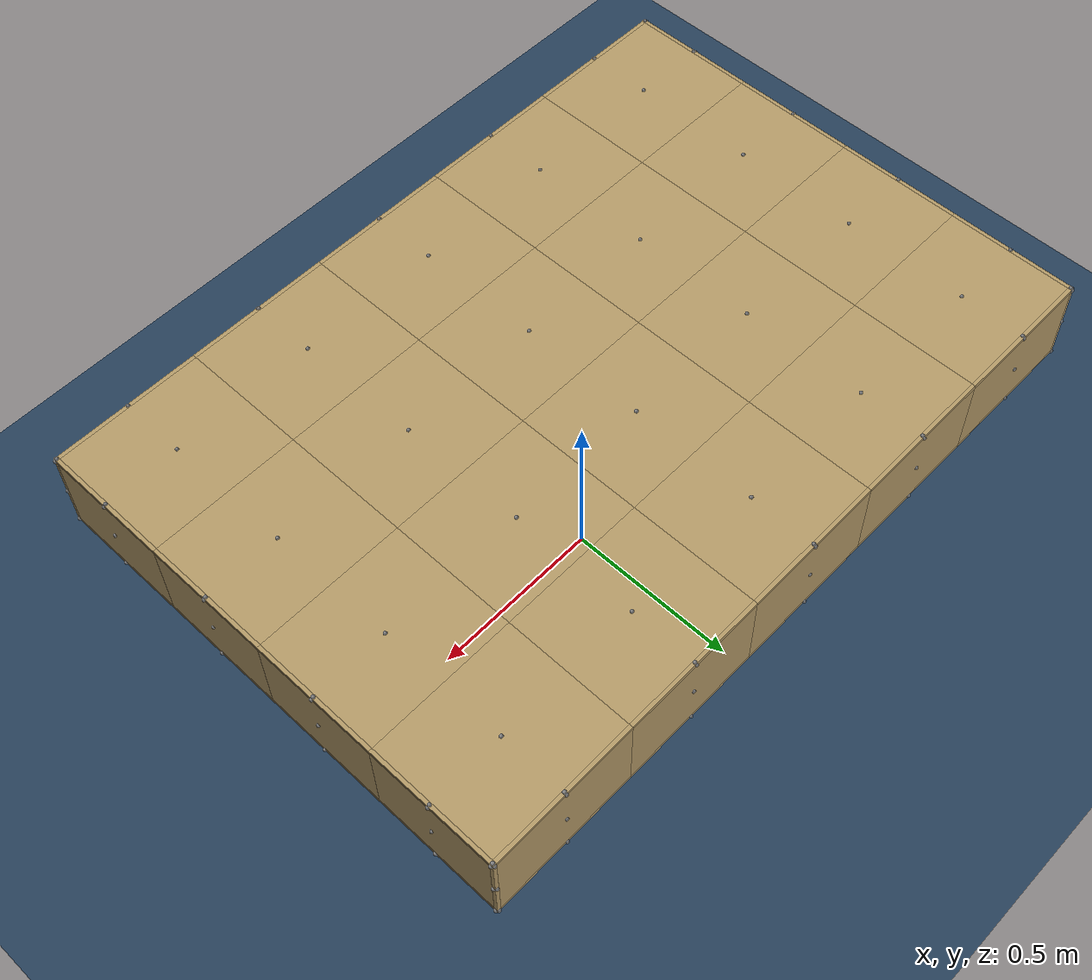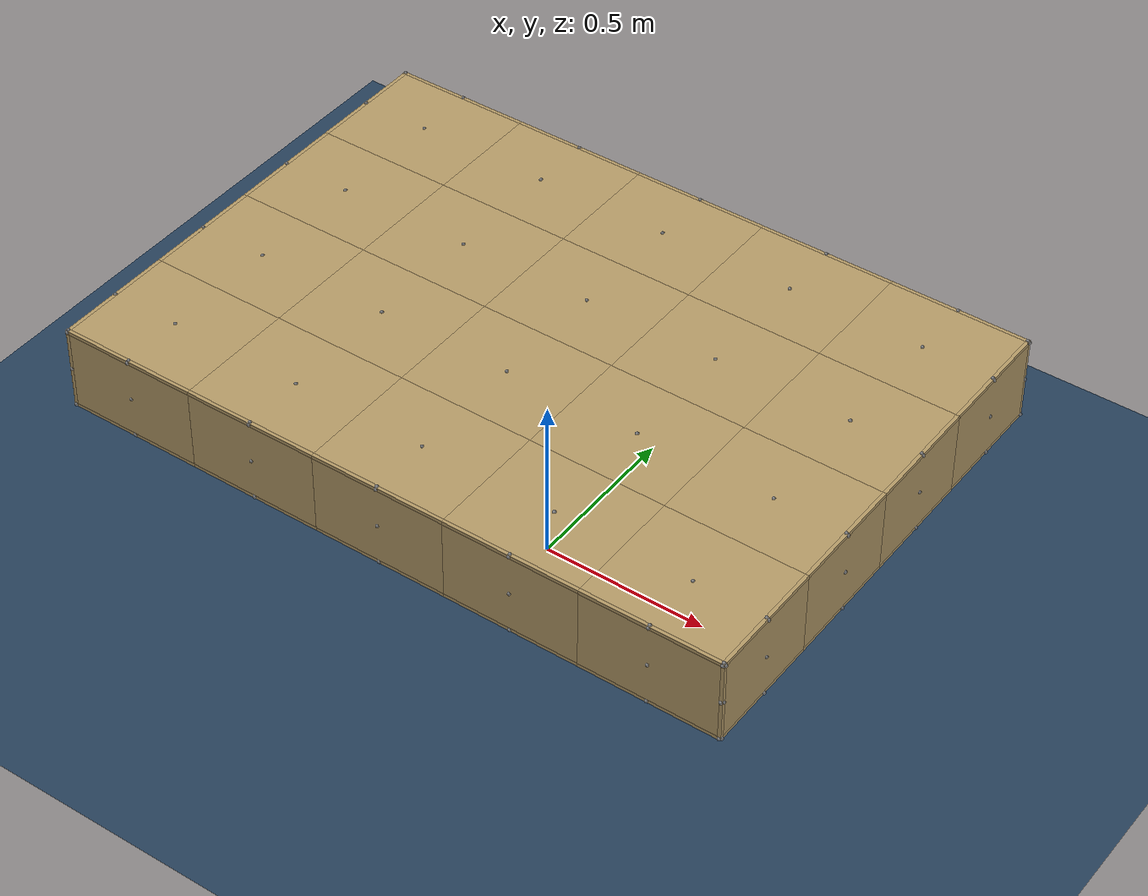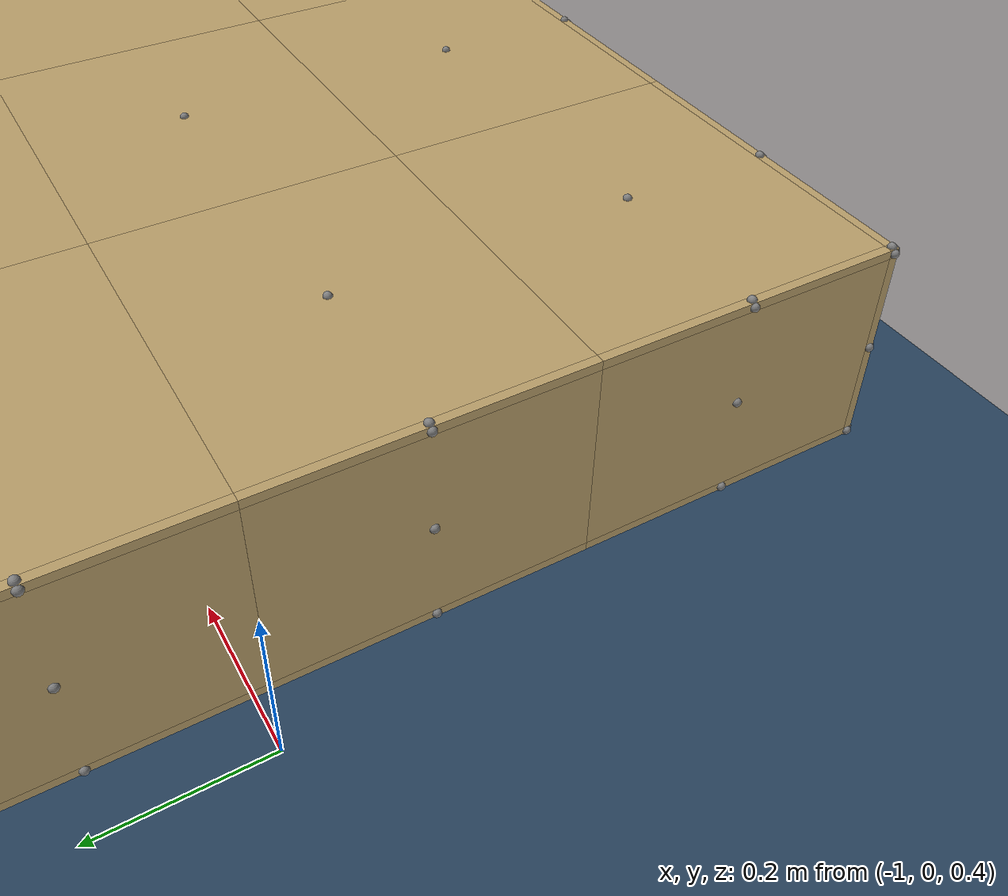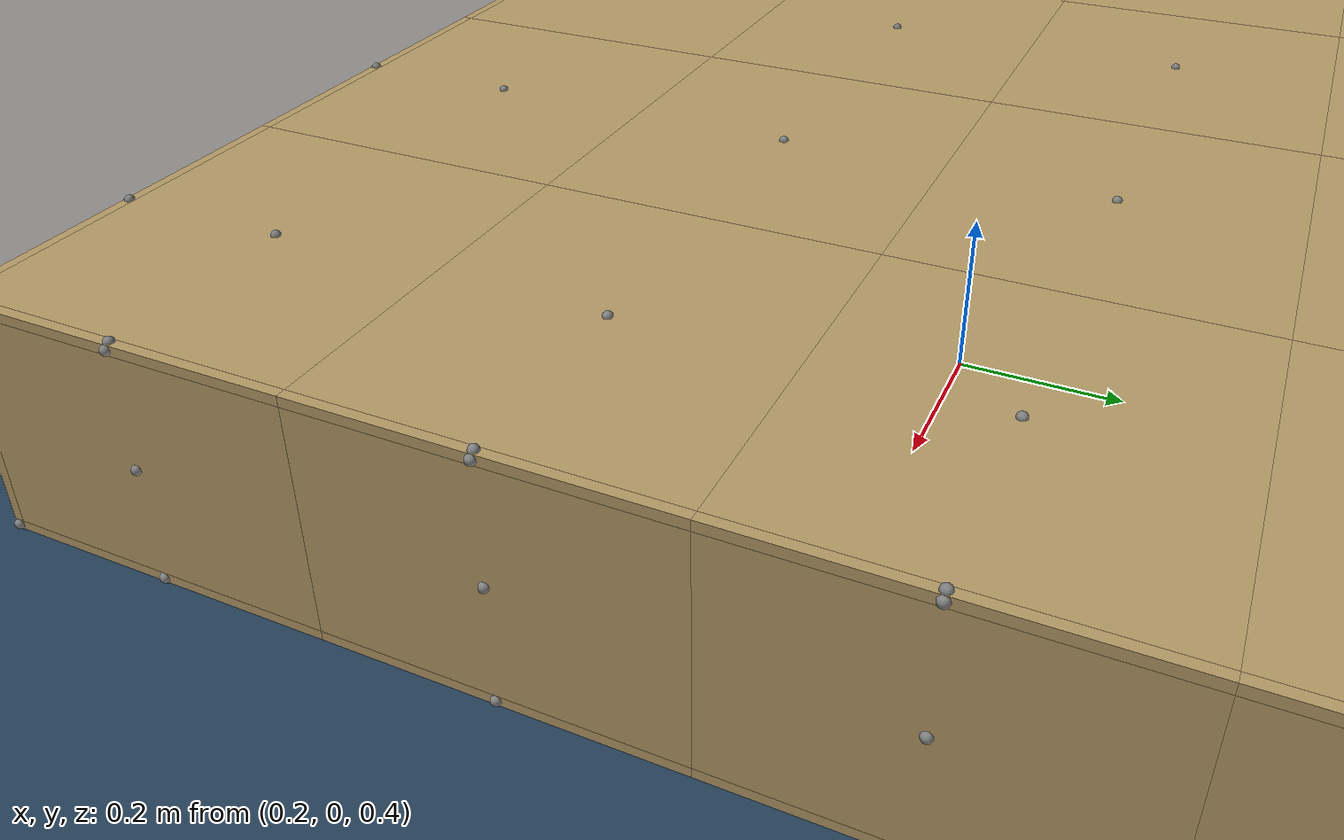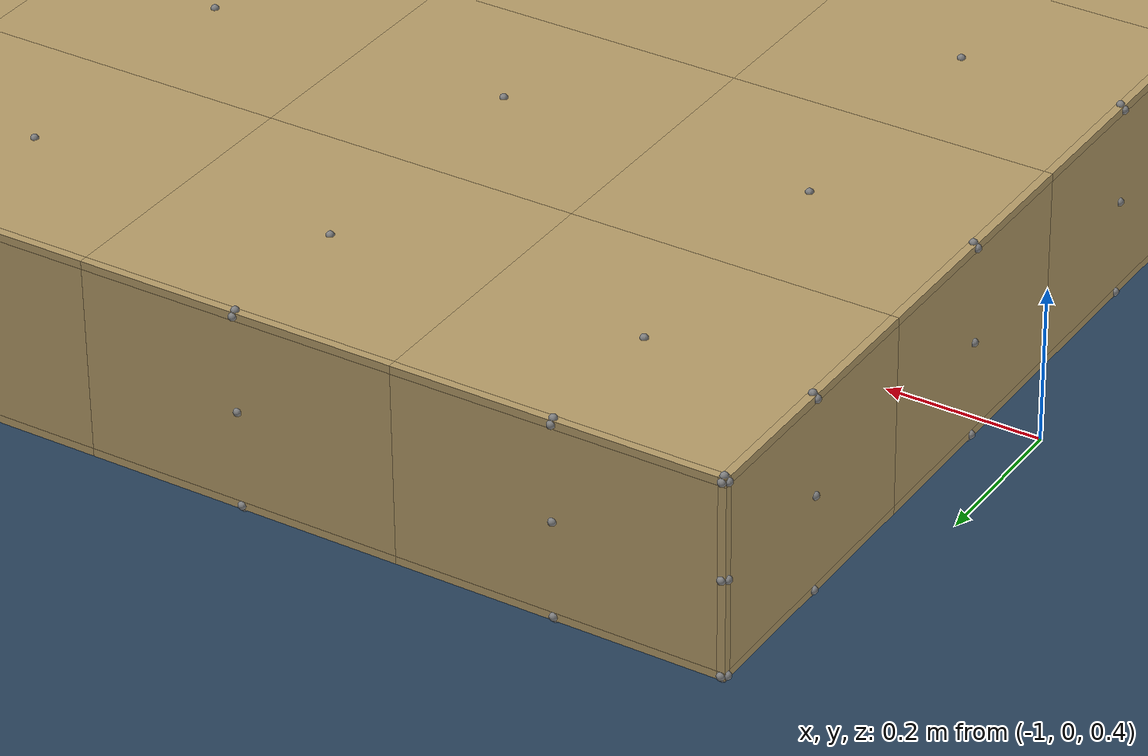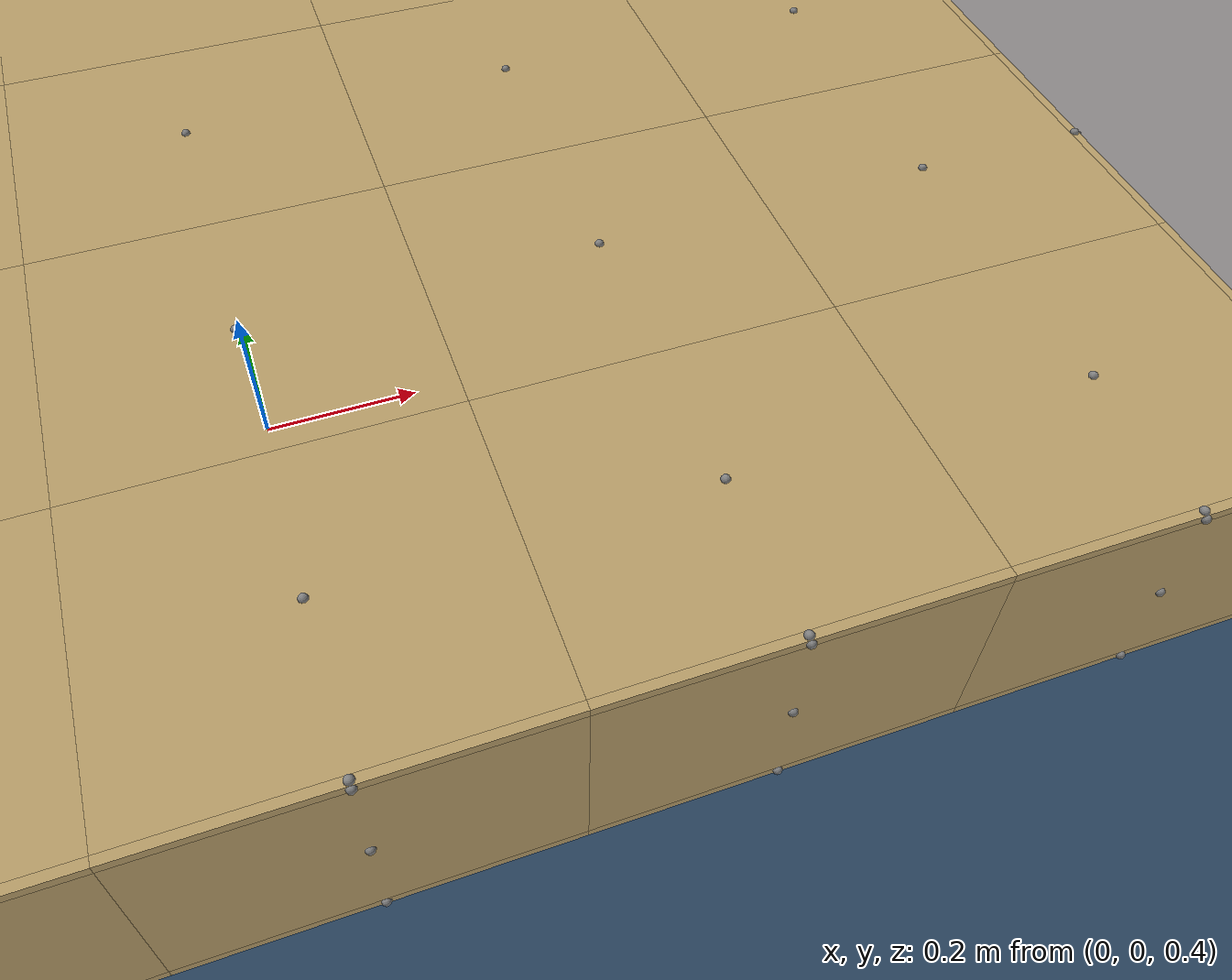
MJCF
<mujoco model="discrete_custom_box">
  <size memory="512M"/>
  <option integrator="implicitfast" timestep="0.001" iterations="80" noslip_iterations="5" tolerance="1e-06" impratio="1.0" gravity="0 0 -9.81" density="1.225" viscosity="1.81e-05">
    <flag contact="enable"/>
  </option>
  <visual>
    <quality shadowsize="0"/>
    <global offwidth="0" offheight="0"/>
    <headlight ambient="0.28 0.28 0.28" diffuse="0.56 0.56 0.56" specular="0.07 0.07 0.07"/>
    <map znear="0.01"/>
  </visual>

  <asset>
    <texture type="2d" name="ground_tex" builtin="checker" mark="edge" rgb1="0.2 0.3 0.4" rgb2="0.1 0.2 0.3"
             markrgb="0.8 0.8 0.8" width="300" height="300"/>
    <material name="ground_mat" texture="ground_tex" texrepeat="5 5" texuniform="true" reflectance="0.0"/>
  </asset>

  <default>
    <joint armature="0.05" damping="1.0"/>
    <geom friction="0.8" solref="0.02 1.0" solimp="0.1 0.95 0.005"/>
    <default class="weld_bpaperbox">
      <equality solref="0.01 1.0" solimp="0.1 0.95 0.005 0.5 2"/>
    </default>
    <default class="contact_bpaperbox">
      <geom solref="0.01 1.0" solimp="0.1 0.95 0.005 0.5 2" contype="1" conaffinity="30" group="0" friction="0.8" rgba="0.7 0.6 0.4 0.9"/>
    </default>
    <default class="weld_bcushion">
      <equality solref="0.03 0.8" solimp="0.1 0.95 0.005 0.5 2.0"/>
    </default>
    <default class="contact_bcushion">
      <geom solref="0.03 0.8" solimp="0.1 0.95 0.005 0.5 2.0" contype="2" conaffinity="29" group="1" friction="0.8" rgba="0.9 0.9 0.9 0.5"/>
    </default>
    <default class="contact_bcushion_edge">
      <geom solref="0.001 0.0001" solimp="0.95 0.999 0.001 0.5 2.0" contype="2" conaffinity="29" group="1" friction="0.8" rgba="0.9 0.9 0.9 0.5"/>
    </default>
    <default class="weld_bopencell">
      <equality solref="0.01 0.3" solimp="0.5 0.95 0.001 0.5 2.0"/>
    </default>
    <default class="contact_bopencell">
      <geom solref="0.01 0.3" solimp="0.5 0.95 0.001 0.5 2.0" contype="4" conaffinity="3" group="2" friction="0.8" rgba="0.1 0.1 0.1 1.0"/>
    </default>
    <default class="weld_bopencellcohesive">
      <equality solref="0.01 1.0" solimp="0.1 0.99 0.001 0.5 2.0"/>
    </default>
    <default class="contact_bopencellcohesive">
      <geom solref="0.01 1.0" solimp="0.1 0.99 0.001 0.5 2.0" contype="8" conaffinity="3" group="2" friction="0.8" rgba="1.0 0.1 0.1 0.8"/>
    </default>
    <default class="weld_bchassis">
      <equality solref="0.002 0.5" solimp="0.1 0.95 0.005 0.5 2.0"/>
    </default>
    <default class="contact_bchassis">
      <geom solref="0.002 0.5" solimp="0.1 0.95 0.005 0.5 2.0" contype="16" conaffinity="3" group="2" friction="0.8" rgba="0.1 0.5 0.8 1.0"/>
    </default>
    <default class="weld_bauxboxmass">
      <equality solref="0.002 0.5" solimp="0.1 0.95 0.005 0.5 2.0"/>
    </default>
    <default class="contact_bauxboxmass">
      <geom solref="0.002 0.5" solimp="0.1 0.95 0.005 0.5 2.0" contype="0" conaffinity="0" group="3" friction="0.8" rgba="1 0 0 0.4"/>
    </default>
    <default class="weld_aux">
      <equality solref="0.002 1.0" solimp="0.9 0.999 0.001"/>
    </default>
  </default>

  <worldbody>
    <camera name="iso_view" pos="4.5 -4.5 3.5" xyaxes="1 1 0 -0.4 0.4 1" mode="fixed"/>
    <light pos="0 0 6" dir="0 0 -1" directional="false" diffuse="0.49 0.49 0.49" ambient="0.21 0.21 0.21" castshadow="false"/>
    <light pos="3 3 5" dir="-1 -1 -1" directional="false" diffuse="0.21 0.21 0.21" castshadow="false"/>
    <geom name="ground" type="plane" size="10 10 0.1" friction="0.2" contype="1" conaffinity="1" group="0" material="ground_mat" solref="0.001 0.0001" solimp="0.90 0.99 0.01 0.5 2"/>
    <body name="BPackagingBox" pos="0.00000 0.00000 0.62500" axisangle="1.0000 0.0000 0.0000 180.0000">
      <freejoint/>
      <geom type="box" size="0.001 0.001 0.001" mass="0.000021" rgba="0 0 0 0" contype="0" conaffinity="0" friction="0.8"/>
      <body name="BPaperBox">
        <body name="b_bpaperbox_0_0_0" pos="-0.99500 -0.69500 -0.12000">
          <joint type="slide" axis="1 0 0"/>
          <joint type="slide" axis="0 1 0"/>
          <joint type="slide" axis="0 0 1"/>
          <joint type="ball"/>
          <geom name="g_bpaperbox_0_0_0" type="box" size="0.00500 0.00500 0.00500" mass="0.000056" class="contact_bpaperbox"/>
          <site name="s_BPaperBox_0_0_0_PX" pos="0.00500 0 0"/>
          <site name="s_BPaperBox_0_0_0_NX" pos="-0.00500 0 0"/>
          <site name="s_BPaperBox_0_0_0_PY" pos="0 0.00500 0"/>
          <site name="s_BPaperBox_0_0_0_NY" pos="0 -0.00500 0"/>
          <site name="s_BPaperBox_0_0_0_PZ" pos="0 0 0.00500"/>
          <site name="s_BPaperBox_0_0_0_NZ" pos="0 0 -0.00500"/>
        </body>
        <body name="b_bpaperbox_0_0_1" pos="-0.99500 -0.69500 0.00000">
          <joint type="slide" axis="1 0 0"/>
          <joint type="slide" axis="0 1 0"/>
          <joint type="slide" axis="0 0 1"/>
          <joint type="ball"/>
          <geom name="g_bpaperbox_0_0_1" type="box" size="0.00500 0.00500 0.11500" mass="0.001286" class="contact_bpaperbox"/>
          <site name="s_BPaperBox_0_0_1_PX" pos="0.00500 0 0"/>
          <site name="s_BPaperBox_0_0_1_NX" pos="-0.00500 0 0"/>
          <site name="s_BPaperBox_0_0_1_PY" pos="0 0.00500 0"/>
          <site name="s_BPaperBox_0_0_1_NY" pos="0 -0.00500 0"/>
          <site name="s_BPaperBox_0_0_1_PZ" pos="0 0 0.11500"/>
          <site name="s_BPaperBox_0_0_1_NZ" pos="0 0 -0.11500"/>
        </body>
        <body name="b_bpaperbox_0_0_2" pos="-0.99500 -0.69500 0.12000">
          <joint type="slide" axis="1 0 0"/>
          <joint type="slide" axis="0 1 0"/>
          <joint type="slide" axis="0 0 1"/>
          <joint type="ball"/>
          <geom name="g_bpaperbox_0_0_2" type="box" size="0.00500 0.00500 0.00500" mass="0.000056" class="contact_bpaperbox"/>
          <site name="s_BPaperBox_0_0_2_PX" pos="0.00500 0 0"/>
          <site name="s_BPaperBox_0_0_2_NX" pos="-0.00500 0 0"/>
          <site name="s_BPaperBox_0_0_2_PY" pos="0 0.00500 0"/>
          <site name="s_BPaperBox_0_0_2_NY" pos="0 -0.00500 0"/>
          <site name="s_BPaperBox_0_0_2_PZ" pos="0 0 0.00500"/>
          <site name="s_BPaperBox_0_0_2_NZ" pos="0 0 -0.00500"/>
        </body>
        <body name="b_bpaperbox_0_1_0" pos="-0.99500 -0.51750 -0.12000">
          <joint type="slide" axis="1 0 0"/>
          <joint type="slide" axis="0 1 0"/>
          <joint type="slide" axis="0 0 1"/>
          <joint type="ball"/>
          <geom name="g_bpaperbox_0_1_0" type="box" size="0.00500 0.17250 0.00500" mass="0.001929" class="contact_bpaperbox"/>
          <site name="s_BPaperBox_0_1_0_PX" pos="0.00500 0 0"/>
          <site name="s_BPaperBox_0_1_0_NX" pos="-0.00500 0 0"/>
          <site name="s_BPaperBox_0_1_0_PY" pos="0 0.17250 0"/>
          <site name="s_BPaperBox_0_1_0_NY" pos="0 -0.17250 0"/>
          <site name="s_BPaperBox_0_1_0_PZ" pos="0 0 0.00500"/>
          <site name="s_BPaperBox_0_1_0_NZ" pos="0 0 -0.00500"/>
        </body>
        <body name="b_bpaperbox_0_1_1" pos="-0.99500 -0.51750 0.00000">
          <joint type="slide" axis="1 0 0"/>
          <joint type="slide" axis="0 1 0"/>
          <joint type="slide" axis="0 0 1"/>
          <joint type="ball"/>
          <geom name="g_bpaperbox_0_1_1" type="box" size="0.00500 0.17250 0.11500" mass="0.044362" class="contact_bpaperbox"/>
          <site name="s_BPaperBox_0_1_1_PX" pos="0.00500 0 0"/>
          <site name="s_BPaperBox_0_1_1_NX" pos="-0.00500 0 0"/>
          <site name="s_BPaperBox_0_1_1_PY" pos="0 0.17250 0"/>
          <site name="s_BPaperBox_0_1_1_NY" pos="0 -0.17250 0"/>
          <site name="s_BPaperBox_0_1_1_PZ" pos="0 0 0.11500"/>
          <site name="s_BPaperBox_0_1_1_NZ" pos="0 0 -0.11500"/>
        </body>
        <body name="b_bpaperbox_0_1_2" pos="-0.99500 -0.51750 0.12000">
          <joint type="slide" axis="1 0 0"/>
          <joint type="slide" axis="0 1 0"/>
          <joint type="slide" axis="0 0 1"/>
          <joint type="ball"/>
          <geom name="g_bpaperbox_0_1_2" type="box" size="0.00500 0.17250 0.00500" mass="0.001929" class="contact_bpaperbox"/>
          <site name="s_BPaperBox_0_1_2_PX" pos="0.00500 0 0"/>
          <site name="s_BPaperBox_0_1_2_NX" pos="-0.00500 0 0"/>
          <site name="s_BPaperBox_0_1_2_PY" pos="0 0.17250 0"/>
          <site name="s_BPaperBox_0_1_2_NY" pos="0 -0.17250 0"/>
          <site name="s_BPaperBox_0_1_2_PZ" pos="0 0 0.00500"/>
          <site name="s_BPaperBox_0_1_2_NZ" pos="0 0 -0.00500"/>
        </body>
        <body name="b_bpaperbox_0_2_0" pos="-0.99500 -0.17250 -0.12000">
          <joint type="slide" axis="1 0 0"/>
          <joint type="slide" axis="0 1 0"/>
          <joint type="slide" axis="0 0 1"/>
          <joint type="ball"/>
          <geom name="g_bpaperbox_0_2_0" type="box" size="0.00500 0.17250 0.00500" mass="0.001929" class="contact_bpaperbox"/>
          <site name="s_BPaperBox_0_2_0_PX" pos="0.00500 0 0"/>
          <site name="s_BPaperBox_0_2_0_NX" pos="-0.00500 0 0"/>
          <site name="s_BPaperBox_0_2_0_PY" pos="0 0.17250 0"/>
          <site name="s_BPaperBox_0_2_0_NY" pos="0 -0.17250 0"/>
          <site name="s_BPaperBox_0_2_0_PZ" pos="0 0 0.00500"/>
          <site name="s_BPaperBox_0_2_0_NZ" pos="0 0 -0.00500"/>
        </body>
        <body name="b_bpaperbox_0_2_1" pos="-0.99500 -0.17250 0.00000">
          <joint type="slide" axis="1 0 0"/>
          <joint type="slide" axis="0 1 0"/>
          <joint type="slide" axis="0 0 1"/>
          <joint type="ball"/>
          <geom name="g_bpaperbox_0_2_1" type="box" size="0.00500 0.17250 0.11500" mass="0.044362" class="contact_bpaperbox"/>
          <site name="s_BPaperBox_0_2_1_PX" pos="0.00500 0 0"/>
          <site name="s_BPaperBox_0_2_1_NX" pos="-0.00500 0 0"/>
          <site name="s_BPaperBox_0_2_1_PY" pos="0 0.17250 0"/>
          <site name="s_BPaperBox_0_2_1_NY" pos="0 -0.17250 0"/>
          <site name="s_BPaperBox_0_2_1_PZ" pos="0 0 0.11500"/>
          <site name="s_BPaperBox_0_2_1_NZ" pos="0 0 -0.11500"/>
        </body>
        <body name="b_bpaperbox_0_2_2" pos="-0.99500 -0.17250 0.12000">
          <joint type="slide" axis="1 0 0"/>
          <joint type="slide" axis="0 1 0"/>
          <joint type="slide" axis="0 0 1"/>
          <joint type="ball"/>
          <geom name="g_bpaperbox_0_2_2" type="box" size="0.00500 0.17250 0.00500" mass="0.001929" class="contact_bpaperbox"/>
          <site name="s_BPaperBox_0_2_2_PX" pos="0.00500 0 0"/>
          <site name="s_BPaperBox_0_2_2_NX" pos="-0.00500 0 0"/>
          <site name="s_BPaperBox_0_2_2_PY" pos="0 0.17250 0"/>
          <site name="s_BPaperBox_0_2_2_NY" pos="0 -0.17250 0"/>
          <site name="s_BPaperBox_0_2_2_PZ" pos="0 0 0.00500"/>
          <site name="s_BPaperBox_0_2_2_NZ" pos="0 0 -0.00500"/>
        </body>
        <body name="b_bpaperbox_0_3_0" pos="-0.99500 0.17250 -0.12000">
          <joint type="slide" axis="1 0 0"/>
          <joint type="slide" axis="0 1 0"/>
          <joint type="slide" axis="0 0 1"/>
          <joint type="ball"/>
          <geom name="g_bpaperbox_0_3_0" type="box" size="0.00500 0.17250 0.00500" mass="0.001929" class="contact_bpaperbox"/>
          <site name="s_BPaperBox_0_3_0_PX" pos="0.00500 0 0"/>
          <site name="s_BPaperBox_0_3_0_NX" pos="-0.00500 0 0"/>
          <site name="s_BPaperBox_0_3_0_PY" pos="0 0.17250 0"/>
          <site name="s_BPaperBox_0_3_0_NY" pos="0 -0.17250 0"/>
          <site name="s_BPaperBox_0_3_0_PZ" pos="0 0 0.00500"/>
          <site name="s_BPaperBox_0_3_0_NZ" pos="0 0 -0.00500"/>
        </body>
        <body name="b_bpaperbox_0_3_1" pos="-0.99500 0.17250 0.00000">
          <joint type="slide" axis="1 0 0"/>
          <joint type="slide" axis="0 1 0"/>
          <joint type="slide" axis="0 0 1"/>
          <joint type="ball"/>
          <geom name="g_bpaperbox_0_3_1" type="box" size="0.00500 0.17250 0.11500" mass="0.044362" class="contact_bpaperbox"/>
          <site name="s_BPaperBox_0_3_1_PX" pos="0.00500 0 0"/>
          <site name="s_BPaperBox_0_3_1_NX" pos="-0.00500 0 0"/>
          <site name="s_BPaperBox_0_3_1_PY" pos="0 0.17250 0"/>
          <site name="s_BPaperBox_0_3_1_NY" pos="0 -0.17250 0"/>
          <site name="s_BPaperBox_0_3_1_PZ" pos="0 0 0.11500"/>
          <site name="s_BPaperBox_0_3_1_NZ" pos="0 0 -0.11500"/>
        </body>
        <body name="b_bpaperbox_0_3_2" pos="-0.99500 0.17250 0.12000">
          <joint type="slide" axis="1 0 0"/>
          <joint type="slide" axis="0 1 0"/>
          <joint type="slide" axis="0 0 1"/>
          <joint type="ball"/>
          <geom name="g_bpaperbox_0_3_2" type="box" size="0.00500 0.17250 0.00500" mass="0.001929" class="contact_bpaperbox"/>
          <site name="s_BPaperBox_0_3_2_PX" pos="0.00500 0 0"/>
          <site name="s_BPaperBox_0_3_2_NX" pos="-0.00500 0 0"/>
          <site name="s_BPaperBox_0_3_2_PY" pos="0 0.17250 0"/>
          <site name="s_BPaperBox_0_3_2_NY" pos="0 -0.17250 0"/>
          <site name="s_BPaperBox_0_3_2_PZ" pos="0 0 0.00500"/>
          <site name="s_BPaperBox_0_3_2_NZ" pos="0 0 -0.00500"/>
        </body>
        <body name="b_bpaperbox_0_4_0" pos="-0.99500 0.51750 -0.12000">
          <joint type="slide" axis="1 0 0"/>
          <joint type="slide" axis="0 1 0"/>
          <joint type="slide" axis="0 0 1"/>
          <joint type="ball"/>
          <geom name="g_bpaperbox_0_4_0" type="box" size="0.00500 0.17250 0.00500" mass="0.001929" class="contact_bpaperbox"/>
          <site name="s_BPaperBox_0_4_0_PX" pos="0.00500 0 0"/>
          <site name="s_BPaperBox_0_4_0_NX" pos="-0.00500 0 0"/>
          <site name="s_BPaperBox_0_4_0_PY" pos="0 0.17250 0"/>
          <site name="s_BPaperBox_0_4_0_NY" pos="0 -0.17250 0"/>
          <site name="s_BPaperBox_0_4_0_PZ" pos="0 0 0.00500"/>
          <site name="s_BPaperBox_0_4_0_NZ" pos="0 0 -0.00500"/>
        </body>
        <body name="b_bpaperbox_0_4_1" pos="-0.99500 0.51750 0.00000">
          <joint type="slide" axis="1 0 0"/>
          <joint type="slide" axis="0 1 0"/>
          <joint type="slide" axis="0 0 1"/>
          <joint type="ball"/>
          <geom name="g_bpaperbox_0_4_1" type="box" size="0.00500 0.17250 0.11500" mass="0.044362" class="contact_bpaperbox"/>
          <site name="s_BPaperBox_0_4_1_PX" pos="0.00500 0 0"/>
          <site name="s_BPaperBox_0_4_1_NX" pos="-0.00500 0 0"/>
          <site name="s_BPaperBox_0_4_1_PY" pos="0 0.17250 0"/>
          <site name="s_BPaperBox_0_4_1_NY" pos="0 -0.17250 0"/>
          <site name="s_BPaperBox_0_4_1_PZ" pos="0 0 0.11500"/>
          <site name="s_BPaperBox_0_4_1_NZ" pos="0 0 -0.11500"/>
        </body>
        <body name="b_bpaperbox_0_4_2" pos="-0.99500 0.51750 0.12000">
          <joint type="slide" axis="1 0 0"/>
          <joint type="slide" axis="0 1 0"/>
          <joint type="slide" axis="0 0 1"/>
          <joint type="ball"/>
          <geom name="g_bpaperbox_0_4_2" type="box" size="0.00500 0.17250 0.00500" mass="0.001929" class="contact_bpaperbox"/>
          <site name="s_BPaperBox_0_4_2_PX" pos="0.00500 0 0"/>
          <site name="s_BPaperBox_0_4_2_NX" pos="-0.00500 0 0"/>
          <site name="s_BPaperBox_0_4_2_PY" pos="0 0.17250 0"/>
          <site name="s_BPaperBox_0_4_2_NY" pos="0 -0.17250 0"/>
          <site name="s_BPaperBox_0_4_2_PZ" pos="0 0 0.00500"/>
          <site name="s_BPaperBox_0_4_2_NZ" pos="0 0 -0.00500"/>
        </body>
        <body name="b_bpaperbox_0_5_0" pos="-0.99500 0.69500 -0.12000">
          <joint type="slide" axis="1 0 0"/>
          <joint type="slide" axis="0 1 0"/>
          <joint type="slide" axis="0 0 1"/>
          <joint type="ball"/>
          <geom name="g_bpaperbox_0_5_0" type="box" size="0.00500 0.00500 0.00500" mass="0.000056" class="contact_bpaperbox"/>
          <site name="s_BPaperBox_0_5_0_PX" pos="0.00500 0 0"/>
          <site name="s_BPaperBox_0_5_0_NX" pos="-0.00500 0 0"/>
          <site name="s_BPaperBox_0_5_0_PY" pos="0 0.00500 0"/>
          <site name="s_BPaperBox_0_5_0_NY" pos="0 -0.00500 0"/>
          <site name="s_BPaperBox_0_5_0_PZ" pos="0 0 0.00500"/>
          <site name="s_BPaperBox_0_5_0_NZ" pos="0 0 -0.00500"/>
        </body>
        <body name="b_bpaperbox_0_5_1" pos="-0.99500 0.69500 0.00000">
          <joint type="slide" axis="1 0 0"/>
          <joint type="slide" axis="0 1 0"/>
          <joint type="slide" axis="0 0 1"/>
          <joint type="ball"/>
          <geom name="g_bpaperbox_0_5_1" type="box" size="0.00500 0.00500 0.11500" mass="0.001286" class="contact_bpaperbox"/>
          <site name="s_BPaperBox_0_5_1_PX" pos="0.00500 0 0"/>
          <site name="s_BPaperBox_0_5_1_NX" pos="-0.00500 0 0"/>
          <site name="s_BPaperBox_0_5_1_PY" pos="0 0.00500 0"/>
          <site name="s_BPaperBox_0_5_1_NY" pos="0 -0.00500 0"/>
          <site name="s_BPaperBox_0_5_1_PZ" pos="0 0 0.11500"/>
          <site name="s_BPaperBox_0_5_1_NZ" pos="0 0 -0.11500"/>
        </body>
        <body name="b_bpaperbox_0_5_2" pos="-0.99500 0.69500 0.12000">
          <joint type="slide" axis="1 0 0"/>
          <joint type="slide" axis="0 1 0"/>
          <joint type="slide" axis="0 0 1"/>
          <joint type="ball"/>
          <geom name="g_bpaperbox_0_5_2" type="box" size="0.00500 0.00500 0.00500" mass="0.000056" class="contact_bpaperbox"/>
          <site name="s_BPaperBox_0_5_2_PX" pos="0.00500 0 0"/>
          <site name="s_BPaperBox_0_5_2_NX" pos="-0.00500 0 0"/>
          <site name="s_BPaperBox_0_5_2_PY" pos="0 0.00500 0"/>
          <site name="s_BPaperBox_0_5_2_NY" pos="0 -0.00500 0"/>
          <site name="s_BPaperBox_0_5_2_PZ" pos="0 0 0.00500"/>
          <site name="s_BPaperBox_0_5_2_NZ" pos="0 0 -0.00500"/>
        </body>
        <body name="b_bpaperbox_1_0_0" pos="-0.79200 -0.69500 -0.12000">
          <joint type="slide" axis="1 0 0"/>
          <joint type="slide" axis="0 1 0"/>
          <joint type="slide" axis="0 0 1"/>
          <joint type="ball"/>
          <geom name="g_bpaperbox_1_0_0" type="box" size="0.19800 0.00500 0.00500" mass="0.002214" class="contact_bpaperbox"/>
          <site name="s_BPaperBox_1_0_0_PX" pos="0.19800 0 0"/>
          <site name="s_BPaperBox_1_0_0_NX" pos="-0.19800 0 0"/>
          <site name="s_BPaperBox_1_0_0_PY" pos="0 0.00500 0"/>
          <site name="s_BPaperBox_1_0_0_NY" pos="0 -0.00500 0"/>
          <site name="s_BPaperBox_1_0_0_PZ" pos="0 0 0.00500"/>
          <site name="s_BPaperBox_1_0_0_NZ" pos="0 0 -0.00500"/>
        </body>
        <body name="b_bpaperbox_1_0_1" pos="-0.79200 -0.69500 0.00000">
          <joint type="slide" axis="1 0 0"/>
          <joint type="slide" axis="0 1 0"/>
          <joint type="slide" axis="0 0 1"/>
          <joint type="ball"/>
          <geom name="g_bpaperbox_1_0_1" type="box" size="0.19800 0.00500 0.11500" mass="0.050920" class="contact_bpaperbox"/>
          <site name="s_BPaperBox_1_0_1_PX" pos="0.19800 0 0"/>
          <site name="s_BPaperBox_1_0_1_NX" pos="-0.19800 0 0"/>
          <site name="s_BPaperBox_1_0_1_PY" pos="0 0.00500 0"/>
          <site name="s_BPaperBox_1_0_1_NY" pos="0 -0.00500 0"/>
          <site name="s_BPaperBox_1_0_1_PZ" pos="0 0 0.11500"/>
          <site name="s_BPaperBox_1_0_1_NZ" pos="0 0 -0.11500"/>
        </body>
        <body name="b_bpaperbox_1_0_2" pos="-0.79200 -0.69500 0.12000">
          <joint type="slide" axis="1 0 0"/>
          <joint type="slide" axis="0 1 0"/>
          <joint type="slide" axis="0 0 1"/>
          <joint type="ball"/>
          <geom name="g_bpaperbox_1_0_2" type="box" size="0.19800 0.00500 0.00500" mass="0.002214" class="contact_bpaperbox"/>
          <site name="s_BPaperBox_1_0_2_PX" pos="0.19800 0 0"/>
          <site name="s_BPaperBox_1_0_2_NX" pos="-0.19800 0 0"/>
          <site name="s_BPaperBox_1_0_2_PY" pos="0 0.00500 0"/>
          <site name="s_BPaperBox_1_0_2_NY" pos="0 -0.00500 0"/>
          <site name="s_BPaperBox_1_0_2_PZ" pos="0 0 0.00500"/>
          <site name="s_BPaperBox_1_0_2_NZ" pos="0 0 -0.00500"/>
        </body>
        <body name="b_bpaperbox_1_1_0" pos="-0.79200 -0.51750 -0.12000">
          <joint type="slide" axis="1 0 0"/>
          <joint type="slide" axis="0 1 0"/>
          <joint type="slide" axis="0 0 1"/>
          <joint type="ball"/>
          <geom name="g_bpaperbox_1_1_0" type="box" size="0.19800 0.17250 0.00500" mass="0.076379" class="contact_bpaperbox"/>
          <site name="s_BPaperBox_1_1_0_PX" pos="0.19800 0 0"/>
          <site name="s_BPaperBox_1_1_0_NX" pos="-0.19800 0 0"/>
          <site name="s_BPaperBox_1_1_0_PY" pos="0 0.17250 0"/>
          <site name="s_BPaperBox_1_1_0_NY" pos="0 -0.17250 0"/>
          <site name="s_BPaperBox_1_1_0_PZ" pos="0 0 0.00500"/>
          <site name="s_BPaperBox_1_1_0_NZ" pos="0 0 -0.00500"/>
        </body>
        <body name="b_bpaperbox_1_1_2" pos="-0.79200 -0.51750 0.12000">
          <joint type="slide" axis="1 0 0"/>
          <joint type="slide" axis="0 1 0"/>
          <joint type="slide" axis="0 0 1"/>
          <joint type="ball"/>
          <geom name="g_bpaperbox_1_1_2" type="box" size="0.19800 0.17250 0.00500" mass="0.076379" class="contact_bpaperbox"/>
          <site name="s_BPaperBox_1_1_2_PX" pos="0.19800 0 0"/>
          <site name="s_BPaperBox_1_1_2_NX" pos="-0.19800 0 0"/>
          <site name="s_BPaperBox_1_1_2_PY" pos="0 0.17250 0"/>
          <site name="s_BPaperBox_1_1_2_NY" pos="0 -0.17250 0"/>
          <site name="s_BPaperBox_1_1_2_PZ" pos="0 0 0.00500"/>
          <site name="s_BPaperBox_1_1_2_NZ" pos="0 0 -0.00500"/>
        </body>
        <body name="b_bpaperbox_1_2_0" pos="-0.79200 -0.17250 -0.12000">
          <joint type="slide" axis="1 0 0"/>
          <joint type="slide" axis="0 1 0"/>
          <joint type="slide" axis="0 0 1"/>
          <joint type="ball"/>
          <geom name="g_bpaperbox_1_2_0" type="box" size="0.19800 0.17250 0.00500" mass="0.076379" class="contact_bpaperbox"/>
          <site name="s_BPaperBox_1_2_0_PX" pos="0.19800 0 0"/>
          <site name="s_BPaperBox_1_2_0_NX" pos="-0.19800 0 0"/>
          <site name="s_BPaperBox_1_2_0_PY" pos="0 0.17250 0"/>
          <site name="s_BPaperBox_1_2_0_NY" pos="0 -0.17250 0"/>
          <site name="s_BPaperBox_1_2_0_PZ" pos="0 0 0.00500"/>
          <site name="s_BPaperBox_1_2_0_NZ" pos="0 0 -0.00500"/>
        </body>
        <body name="b_bpaperbox_1_2_2" pos="-0.79200 -0.17250 0.12000">
          <joint type="slide" axis="1 0 0"/>
          <joint type="slide" axis="0 1 0"/>
          <joint type="slide" axis="0 0 1"/>
          <joint type="ball"/>
          <geom name="g_bpaperbox_1_2_2" type="box" size="0.19800 0.17250 0.00500" mass="0.076379" class="contact_bpaperbox"/>
          <site name="s_BPaperBox_1_2_2_PX" pos="0.19800 0 0"/>
          <site name="s_BPaperBox_1_2_2_NX" pos="-0.19800 0 0"/>
          <site name="s_BPaperBox_1_2_2_PY" pos="0 0.17250 0"/>
          <site name="s_BPaperBox_1_2_2_NY" pos="0 -0.17250 0"/>
          <site name="s_BPaperBox_1_2_2_PZ" pos="0 0 0.00500"/>
          <site name="s_BPaperBox_1_2_2_NZ" pos="0 0 -0.00500"/>
        </body>
        <body name="b_bpaperbox_1_3_0" pos="-0.79200 0.17250 -0.12000">
          <joint type="slide" axis="1 0 0"/>
          <joint type="slide" axis="0 1 0"/>
          <joint type="slide" axis="0 0 1"/>
          <joint type="ball"/>
          <geom name="g_bpaperbox_1_3_0" type="box" size="0.19800 0.17250 0.00500" mass="0.076379" class="contact_bpaperbox"/>
          <site name="s_BPaperBox_1_3_0_PX" pos="0.19800 0 0"/>
          <site name="s_BPaperBox_1_3_0_NX" pos="-0.19800 0 0"/>
          <site name="s_BPaperBox_1_3_0_PY" pos="0 0.17250 0"/>
          <site name="s_BPaperBox_1_3_0_NY" pos="0 -0.17250 0"/>
          <site name="s_BPaperBox_1_3_0_PZ" pos="0 0 0.00500"/>
          <site name="s_BPaperBox_1_3_0_NZ" pos="0 0 -0.00500"/>
        </body>
        <body name="b_bpaperbox_1_3_2" pos="-0.79200 0.17250 0.12000">
          <joint type="slide" axis="1 0 0"/>
          <joint type="slide" axis="0 1 0"/>
          <joint type="slide" axis="0 0 1"/>
          <joint type="ball"/>
          <geom name="g_bpaperbox_1_3_2" type="box" size="0.19800 0.17250 0.00500" mass="0.076379" class="contact_bpaperbox"/>
          <site name="s_BPaperBox_1_3_2_PX" pos="0.19800 0 0"/>
          <site name="s_BPaperBox_1_3_2_NX" pos="-0.19800 0 0"/>
          <site name="s_BPaperBox_1_3_2_PY" pos="0 0.17250 0"/>
          <site name="s_BPaperBox_1_3_2_NY" pos="0 -0.17250 0"/>
          <site name="s_BPaperBox_1_3_2_PZ" pos="0 0 0.00500"/>
          <site name="s_BPaperBox_1_3_2_NZ" pos="0 0 -0.00500"/>
        </body>
        <body name="b_bpaperbox_1_4_0" pos="-0.79200 0.51750 -0.12000">
          <joint type="slide" axis="1 0 0"/>
          <joint type="slide" axis="0 1 0"/>
          <joint type="slide" axis="0 0 1"/>
          <joint type="ball"/>
          <geom name="g_bpaperbox_1_4_0" type="box" size="0.19800 0.17250 0.00500" mass="0.076379" class="contact_bpaperbox"/>
          <site name="s_BPaperBox_1_4_0_PX" pos="0.19800 0 0"/>
          <site name="s_BPaperBox_1_4_0_NX" pos="-0.19800 0 0"/>
          <site name="s_BPaperBox_1_4_0_PY" pos="0 0.17250 0"/>
          <site name="s_BPaperBox_1_4_0_NY" pos="0 -0.17250 0"/>
          <site name="s_BPaperBox_1_4_0_PZ" pos="0 0 0.00500"/>
          <site name="s_BPaperBox_1_4_0_NZ" pos="0 0 -0.00500"/>
        </body>
        <body name="b_bpaperbox_1_4_2" pos="-0.79200 0.51750 0.12000">
          <joint type="slide" axis="1 0 0"/>
          <joint type="slide" axis="0 1 0"/>
          <joint type="slide" axis="0 0 1"/>
          <joint type="ball"/>
          <geom name="g_bpaperbox_1_4_2" type="box" size="0.19800 0.17250 0.00500" mass="0.076379" class="contact_bpaperbox"/>
          <site name="s_BPaperBox_1_4_2_PX" pos="0.19800 0 0"/>
          <site name="s_BPaperBox_1_4_2_NX" pos="-0.19800 0 0"/>
          <site name="s_BPaperBox_1_4_2_PY" pos="0 0.17250 0"/>
          <site name="s_BPaperBox_1_4_2_NY" pos="0 -0.17250 0"/>
          <site name="s_BPaperBox_1_4_2_PZ" pos="0 0 0.00500"/>
          <site name="s_BPaperBox_1_4_2_NZ" pos="0 0 -0.00500"/>
        </body>
        <body name="b_bpaperbox_1_5_0" pos="-0.79200 0.69500 -0.12000">
          <joint type="slide" axis="1 0 0"/>
          <joint type="slide" axis="0 1 0"/>
          <joint type="slide" axis="0 0 1"/>
          <joint type="ball"/>
          <geom name="g_bpaperbox_1_5_0" type="box" size="0.19800 0.00500 0.00500" mass="0.002214" class="contact_bpaperbox"/>
          <site name="s_BPaperBox_1_5_0_PX" pos="0.19800 0 0"/>
          <site name="s_BPaperBox_1_5_0_NX" pos="-0.19800 0 0"/>
          <site name="s_BPaperBox_1_5_0_PY" pos="0 0.00500 0"/>
          <site name="s_BPaperBox_1_5_0_NY" pos="0 -0.00500 0"/>
          <site name="s_BPaperBox_1_5_0_PZ" pos="0 0 0.00500"/>
          <site name="s_BPaperBox_1_5_0_NZ" pos="0 0 -0.00500"/>
        </body>
        <body name="b_bpaperbox_1_5_1" pos="-0.79200 0.69500 0.00000">
          <joint type="slide" axis="1 0 0"/>
          <joint type="slide" axis="0 1 0"/>
          <joint type="slide" axis="0 0 1"/>
          <joint type="ball"/>
          <geom name="g_bpaperbox_1_5_1" type="box" size="0.19800 0.00500 0.11500" mass="0.050920" class="contact_bpaperbox"/>
          <site name="s_BPaperBox_1_5_1_PX" pos="0.19800 0 0"/>
          <site name="s_BPaperBox_1_5_1_NX" pos="-0.19800 0 0"/>
          <site name="s_BPaperBox_1_5_1_PY" pos="0 0.00500 0"/>
          <site name="s_BPaperBox_1_5_1_NY" pos="0 -0.00500 0"/>
          <site name="s_BPaperBox_1_5_1_PZ" pos="0 0 0.11500"/>
          <site name="s_BPaperBox_1_5_1_NZ" pos="0 0 -0.11500"/>
        </body>
        <body name="b_bpaperbox_1_5_2" pos="-0.79200 0.69500 0.12000">
          <joint type="slide" axis="1 0 0"/>
          <joint type="slide" axis="0 1 0"/>
          <joint type="slide" axis="0 0 1"/>
          <joint type="ball"/>
          <geom name="g_bpaperbox_1_5_2" type="box" size="0.19800 0.00500 0.00500" mass="0.002214" class="contact_bpaperbox"/>
          <site name="s_BPaperBox_1_5_2_PX" pos="0.19800 0 0"/>
          <site name="s_BPaperBox_1_5_2_NX" pos="-0.19800 0 0"/>
          <site name="s_BPaperBox_1_5_2_PY" pos="0 0.00500 0"/>
          <site name="s_BPaperBox_1_5_2_NY" pos="0 -0.00500 0"/>
          <site name="s_BPaperBox_1_5_2_PZ" pos="0 0 0.00500"/>
          <site name="s_BPaperBox_1_5_2_NZ" pos="0 0 -0.00500"/>
        </body>
        <body name="b_bpaperbox_2_0_0" pos="-0.39600 -0.69500 -0.12000">
          <joint type="slide" axis="1 0 0"/>
          <joint type="slide" axis="0 1 0"/>
          <joint type="slide" axis="0 0 1"/>
          <joint type="ball"/>
          <geom name="g_bpaperbox_2_0_0" type="box" size="0.19800 0.00500 0.00500" mass="0.002214" class="contact_bpaperbox"/>
          <site name="s_BPaperBox_2_0_0_PX" pos="0.19800 0 0"/>
          <site name="s_BPaperBox_2_0_0_NX" pos="-0.19800 0 0"/>
          <site name="s_BPaperBox_2_0_0_PY" pos="0 0.00500 0"/>
          <site name="s_BPaperBox_2_0_0_NY" pos="0 -0.00500 0"/>
          <site name="s_BPaperBox_2_0_0_PZ" pos="0 0 0.00500"/>
          <site name="s_BPaperBox_2_0_0_NZ" pos="0 0 -0.00500"/>
        </body>
        <body name="b_bpaperbox_2_0_1" pos="-0.39600 -0.69500 0.00000">
          <joint type="slide" axis="1 0 0"/>
          <joint type="slide" axis="0 1 0"/>
          <joint type="slide" axis="0 0 1"/>
          <joint type="ball"/>
          <geom name="g_bpaperbox_2_0_1" type="box" size="0.19800 0.00500 0.11500" mass="0.050920" class="contact_bpaperbox"/>
          <site name="s_BPaperBox_2_0_1_PX" pos="0.19800 0 0"/>
          <site name="s_BPaperBox_2_0_1_NX" pos="-0.19800 0 0"/>
          <site name="s_BPaperBox_2_0_1_PY" pos="0 0.00500 0"/>
          <site name="s_BPaperBox_2_0_1_NY" pos="0 -0.00500 0"/>
          <site name="s_BPaperBox_2_0_1_PZ" pos="0 0 0.11500"/>
          <site name="s_BPaperBox_2_0_1_NZ" pos="0 0 -0.11500"/>
        </body>
        <body name="b_bpaperbox_2_0_2" pos="-0.39600 -0.69500 0.12000">
          <joint type="slide" axis="1 0 0"/>
          <joint type="slide" axis="0 1 0"/>
          <joint type="slide" axis="0 0 1"/>
          <joint type="ball"/>
          <geom name="g_bpaperbox_2_0_2" type="box" size="0.19800 0.00500 0.00500" mass="0.002214" class="contact_bpaperbox"/>
          <site name="s_BPaperBox_2_0_2_PX" pos="0.19800 0 0"/>
          <site name="s_BPaperBox_2_0_2_NX" pos="-0.19800 0 0"/>
          <site name="s_BPaperBox_2_0_2_PY" pos="0 0.00500 0"/>
          <site name="s_BPaperBox_2_0_2_NY" pos="0 -0.00500 0"/>
          <site name="s_BPaperBox_2_0_2_PZ" pos="0 0 0.00500"/>
          <site name="s_BPaperBox_2_0_2_NZ" pos="0 0 -0.00500"/>
        </body>
        <body name="b_bpaperbox_2_1_0" pos="-0.39600 -0.51750 -0.12000">
          <joint type="slide" axis="1 0 0"/>
          <joint type="slide" axis="0 1 0"/>
          <joint type="slide" axis="0 0 1"/>
          <joint type="ball"/>
          <geom name="g_bpaperbox_2_1_0" type="box" size="0.19800 0.17250 0.00500" mass="0.076379" class="contact_bpaperbox"/>
          <site name="s_BPaperBox_2_1_0_PX" pos="0.19800 0 0"/>
          <site name="s_BPaperBox_2_1_0_NX" pos="-0.19800 0 0"/>
          <site name="s_BPaperBox_2_1_0_PY" pos="0 0.17250 0"/>
          <site name="s_BPaperBox_2_1_0_NY" pos="0 -0.17250 0"/>
          <site name="s_BPaperBox_2_1_0_PZ" pos="0 0 0.00500"/>
          <site name="s_BPaperBox_2_1_0_NZ" pos="0 0 -0.00500"/>
        </body>
        <body name="b_bpaperbox_2_1_2" pos="-0.39600 -0.51750 0.12000">
          <joint type="slide" axis="1 0 0"/>
          <joint type="slide" axis="0 1 0"/>
          <joint type="slide" axis="0 0 1"/>
          <joint type="ball"/>
          <geom name="g_bpaperbox_2_1_2" type="box" size="0.19800 0.17250 0.00500" mass="0.076379" class="contact_bpaperbox"/>
          <site name="s_BPaperBox_2_1_2_PX" pos="0.19800 0 0"/>
          <site name="s_BPaperBox_2_1_2_NX" pos="-0.19800 0 0"/>
          <site name="s_BPaperBox_2_1_2_PY" pos="0 0.17250 0"/>
          <site name="s_BPaperBox_2_1_2_NY" pos="0 -0.17250 0"/>
          <site name="s_BPaperBox_2_1_2_PZ" pos="0 0 0.00500"/>
          <site name="s_BPaperBox_2_1_2_NZ" pos="0 0 -0.00500"/>
        </body>
        <body name="b_bpaperbox_2_2_0" pos="-0.39600 -0.17250 -0.12000">
          <joint type="slide" axis="1 0 0"/>
          <joint type="slide" axis="0 1 0"/>
          <joint type="slide" axis="0 0 1"/>
          <joint type="ball"/>
          <geom name="g_bpaperbox_2_2_0" type="box" size="0.19800 0.17250 0.00500" mass="0.076379" class="contact_bpaperbox"/>
          <site name="s_BPaperBox_2_2_0_PX" pos="0.19800 0 0"/>
          <site name="s_BPaperBox_2_2_0_NX" pos="-0.19800 0 0"/>
          <site name="s_BPaperBox_2_2_0_PY" pos="0 0.17250 0"/>
          <site name="s_BPaperBox_2_2_0_NY" pos="0 -0.17250 0"/>
          <site name="s_BPaperBox_2_2_0_PZ" pos="0 0 0.00500"/>
          <site name="s_BPaperBox_2_2_0_NZ" pos="0 0 -0.00500"/>
        </body>
        <body name="b_bpaperbox_2_2_2" pos="-0.39600 -0.17250 0.12000">
          <joint type="slide" axis="1 0 0"/>
          <joint type="slide" axis="0 1 0"/>
          <joint type="slide" axis="0 0 1"/>
          <joint type="ball"/>
          <geom name="g_bpaperbox_2_2_2" type="box" size="0.19800 0.17250 0.00500" mass="0.076379" class="contact_bpaperbox"/>
          <site name="s_BPaperBox_2_2_2_PX" pos="0.19800 0 0"/>
          <site name="s_BPaperBox_2_2_2_NX" pos="-0.19800 0 0"/>
          <site name="s_BPaperBox_2_2_2_PY" pos="0 0.17250 0"/>
          <site name="s_BPaperBox_2_2_2_NY" pos="0 -0.17250 0"/>
          <site name="s_BPaperBox_2_2_2_PZ" pos="0 0 0.00500"/>
          <site name="s_BPaperBox_2_2_2_NZ" pos="0 0 -0.00500"/>
        </body>
        <body name="b_bpaperbox_2_3_0" pos="-0.39600 0.17250 -0.12000">
          <joint type="slide" axis="1 0 0"/>
          <joint type="slide" axis="0 1 0"/>
          <joint type="slide" axis="0 0 1"/>
          <joint type="ball"/>
          <geom name="g_bpaperbox_2_3_0" type="box" size="0.19800 0.17250 0.00500" mass="0.076379" class="contact_bpaperbox"/>
          <site name="s_BPaperBox_2_3_0_PX" pos="0.19800 0 0"/>
          <site name="s_BPaperBox_2_3_0_NX" pos="-0.19800 0 0"/>
          <site name="s_BPaperBox_2_3_0_PY" pos="0 0.17250 0"/>
          <site name="s_BPaperBox_2_3_0_NY" pos="0 -0.17250 0"/>
          <site name="s_BPaperBox_2_3_0_PZ" pos="0 0 0.00500"/>
          <site name="s_BPaperBox_2_3_0_NZ" pos="0 0 -0.00500"/>
        </body>
        <body name="b_bpaperbox_2_3_2" pos="-0.39600 0.17250 0.12000">
          <joint type="slide" axis="1 0 0"/>
          <joint type="slide" axis="0 1 0"/>
          <joint type="slide" axis="0 0 1"/>
          <joint type="ball"/>
          <geom name="g_bpaperbox_2_3_2" type="box" size="0.19800 0.17250 0.00500" mass="0.076379" class="contact_bpaperbox"/>
          <site name="s_BPaperBox_2_3_2_PX" pos="0.19800 0 0"/>
          <site name="s_BPaperBox_2_3_2_NX" pos="-0.19800 0 0"/>
          <site name="s_BPaperBox_2_3_2_PY" pos="0 0.17250 0"/>
          <site name="s_BPaperBox_2_3_2_NY" pos="0 -0.17250 0"/>
          <site name="s_BPaperBox_2_3_2_PZ" pos="0 0 0.00500"/>
          <site name="s_BPaperBox_2_3_2_NZ" pos="0 0 -0.00500"/>
        </body>
        <body name="b_bpaperbox_2_4_0" pos="-0.39600 0.51750 -0.12000">
          <joint type="slide" axis="1 0 0"/>
          <joint type="slide" axis="0 1 0"/>
          <joint type="slide" axis="0 0 1"/>
          <joint type="ball"/>
          <geom name="g_bpaperbox_2_4_0" type="box" size="0.19800 0.17250 0.00500" mass="0.076379" class="contact_bpaperbox"/>
          <site name="s_BPaperBox_2_4_0_PX" pos="0.19800 0 0"/>
          <site name="s_BPaperBox_2_4_0_NX" pos="-0.19800 0 0"/>
          <site name="s_BPaperBox_2_4_0_PY" pos="0 0.17250 0"/>
          <site name="s_BPaperBox_2_4_0_NY" pos="0 -0.17250 0"/>
          <site name="s_BPaperBox_2_4_0_PZ" pos="0 0 0.00500"/>
          <site name="s_BPaperBox_2_4_0_NZ" pos="0 0 -0.00500"/>
        </body>
        <body name="b_bpaperbox_2_4_2" pos="-0.39600 0.51750 0.12000">
          <joint type="slide" axis="1 0 0"/>
          <joint type="slide" axis="0 1 0"/>
          <joint type="slide" axis="0 0 1"/>
          <joint type="ball"/>
          <geom name="g_bpaperbox_2_4_2" type="box" size="0.19800 0.17250 0.00500" mass="0.076379" class="contact_bpaperbox"/>
          <site name="s_BPaperBox_2_4_2_PX" pos="0.19800 0 0"/>
          <site name="s_BPaperBox_2_4_2_NX" pos="-0.19800 0 0"/>
          <site name="s_BPaperBox_2_4_2_PY" pos="0 0.17250 0"/>
          <site name="s_BPaperBox_2_4_2_NY" pos="0 -0.17250 0"/>
          <site name="s_BPaperBox_2_4_2_PZ" pos="0 0 0.00500"/>
          <site name="s_BPaperBox_2_4_2_NZ" pos="0 0 -0.00500"/>
        </body>
        <body name="b_bpaperbox_2_5_0" pos="-0.39600 0.69500 -0.12000">
          <joint type="slide" axis="1 0 0"/>
          <joint type="slide" axis="0 1 0"/>
          <joint type="slide" axis="0 0 1"/>
          <joint type="ball"/>
          <geom name="g_bpaperbox_2_5_0" type="box" size="0.19800 0.00500 0.00500" mass="0.002214" class="contact_bpaperbox"/>
          <site name="s_BPaperBox_2_5_0_PX" pos="0.19800 0 0"/>
          <site name="s_BPaperBox_2_5_0_NX" pos="-0.19800 0 0"/>
          <site name="s_BPaperBox_2_5_0_PY" pos="0 0.00500 0"/>
          <site name="s_BPaperBox_2_5_0_NY" pos="0 -0.00500 0"/>
          <site name="s_BPaperBox_2_5_0_PZ" pos="0 0 0.00500"/>
          <site name="s_BPaperBox_2_5_0_NZ" pos="0 0 -0.00500"/>
        </body>
        <body name="b_bpaperbox_2_5_1" pos="-0.39600 0.69500 0.00000">
          <joint type="slide" axis="1 0 0"/>
          <joint type="slide" axis="0 1 0"/>
          <joint type="slide" axis="0 0 1"/>
          <joint type="ball"/>
          <geom name="g_bpaperbox_2_5_1" type="box" size="0.19800 0.00500 0.11500" mass="0.050920" class="contact_bpaperbox"/>
          <site name="s_BPaperBox_2_5_1_PX" pos="0.19800 0 0"/>
          <site name="s_BPaperBox_2_5_1_NX" pos="-0.19800 0 0"/>
          <site name="s_BPaperBox_2_5_1_PY" pos="0 0.00500 0"/>
          <site name="s_BPaperBox_2_5_1_NY" pos="0 -0.00500 0"/>
          <site name="s_BPaperBox_2_5_1_PZ" pos="0 0 0.11500"/>
          <site name="s_BPaperBox_2_5_1_NZ" pos="0 0 -0.11500"/>
        </body>
        <body name="b_bpaperbox_2_5_2" pos="-0.39600 0.69500 0.12000">
          <joint type="slide" axis="1 0 0"/>
          <joint type="slide" axis="0 1 0"/>
          <joint type="slide" axis="0 0 1"/>
          <joint type="ball"/>
          <geom name="g_bpaperbox_2_5_2" type="box" size="0.19800 0.00500 0.00500" mass="0.002214" class="contact_bpaperbox"/>
          <site name="s_BPaperBox_2_5_2_PX" pos="0.19800 0 0"/>
          <site name="s_BPaperBox_2_5_2_NX" pos="-0.19800 0 0"/>
          <site name="s_BPaperBox_2_5_2_PY" pos="0 0.00500 0"/>
          <site name="s_BPaperBox_2_5_2_NY" pos="0 -0.00500 0"/>
          <site name="s_BPaperBox_2_5_2_PZ" pos="0 0 0.00500"/>
          <site name="s_BPaperBox_2_5_2_NZ" pos="0 0 -0.00500"/>
        </body>
        <body name="b_bpaperbox_3_0_0" pos="0.00000 -0.69500 -0.12000">
          <joint type="slide" axis="1 0 0"/>
          <joint type="slide" axis="0 1 0"/>
          <joint type="slide" axis="0 0 1"/>
          <joint type="ball"/>
          <geom name="g_bpaperbox_3_0_0" type="box" size="0.19800 0.00500 0.00500" mass="0.002214" class="contact_bpaperbox"/>
          <site name="s_BPaperBox_3_0_0_PX" pos="0.19800 0 0"/>
          <site name="s_BPaperBox_3_0_0_NX" pos="-0.19800 0 0"/>
          <site name="s_BPaperBox_3_0_0_PY" pos="0 0.00500 0"/>
          <site name="s_BPaperBox_3_0_0_NY" pos="0 -0.00500 0"/>
          <site name="s_BPaperBox_3_0_0_PZ" pos="0 0 0.00500"/>
          <site name="s_BPaperBox_3_0_0_NZ" pos="0 0 -0.00500"/>
        </body>
        <body name="b_bpaperbox_3_0_1" pos="0.00000 -0.69500 0.00000">
          <joint type="slide" axis="1 0 0"/>
          <joint type="slide" axis="0 1 0"/>
          <joint type="slide" axis="0 0 1"/>
          <joint type="ball"/>
          <geom name="g_bpaperbox_3_0_1" type="box" size="0.19800 0.00500 0.11500" mass="0.050920" class="contact_bpaperbox"/>
          <site name="s_BPaperBox_3_0_1_PX" pos="0.19800 0 0"/>
          <site name="s_BPaperBox_3_0_1_NX" pos="-0.19800 0 0"/>
          <site name="s_BPaperBox_3_0_1_PY" pos="0 0.00500 0"/>
          <site name="s_BPaperBox_3_0_1_NY" pos="0 -0.00500 0"/>
          <site name="s_BPaperBox_3_0_1_PZ" pos="0 0 0.11500"/>
          <site name="s_BPaperBox_3_0_1_NZ" pos="0 0 -0.11500"/>
        </body>
        <body name="b_bpaperbox_3_0_2" pos="0.00000 -0.69500 0.12000">
          <joint type="slide" axis="1 0 0"/>
          <joint type="slide" axis="0 1 0"/>
          <joint type="slide" axis="0 0 1"/>
          <joint type="ball"/>
          <geom name="g_bpaperbox_3_0_2" type="box" size="0.19800 0.00500 0.00500" mass="0.002214" class="contact_bpaperbox"/>
          <site name="s_BPaperBox_3_0_2_PX" pos="0.19800 0 0"/>
          <site name="s_BPaperBox_3_0_2_NX" pos="-0.19800 0 0"/>
          <site name="s_BPaperBox_3_0_2_PY" pos="0 0.00500 0"/>
          <site name="s_BPaperBox_3_0_2_NY" pos="0 -0.00500 0"/>
          <site name="s_BPaperBox_3_0_2_PZ" pos="0 0 0.00500"/>
          <site name="s_BPaperBox_3_0_2_NZ" pos="0 0 -0.00500"/>
        </body>
        <body name="b_bpaperbox_3_1_0" pos="0.00000 -0.51750 -0.12000">
          <joint type="slide" axis="1 0 0"/>
          <joint type="slide" axis="0 1 0"/>
          <joint type="slide" axis="0 0 1"/>
          <joint type="ball"/>
          <geom name="g_bpaperbox_3_1_0" type="box" size="0.19800 0.17250 0.00500" mass="0.076379" class="contact_bpaperbox"/>
          <site name="s_BPaperBox_3_1_0_PX" pos="0.19800 0 0"/>
          <site name="s_BPaperBox_3_1_0_NX" pos="-0.19800 0 0"/>
          <site name="s_BPaperBox_3_1_0_PY" pos="0 0.17250 0"/>
          <site name="s_BPaperBox_3_1_0_NY" pos="0 -0.17250 0"/>
          <site name="s_BPaperBox_3_1_0_PZ" pos="0 0 0.00500"/>
          <site name="s_BPaperBox_3_1_0_NZ" pos="0 0 -0.00500"/>
        </body>
        <body name="b_bpaperbox_3_1_2" pos="0.00000 -0.51750 0.12000">
          <joint type="slide" axis="1 0 0"/>
          <joint type="slide" axis="0 1 0"/>
          <joint type="slide" axis="0 0 1"/>
          <joint type="ball"/>
          <geom name="g_bpaperbox_3_1_2" type="box" size="0.19800 0.17250 0.00500" mass="0.076379" class="contact_bpaperbox"/>
          <site name="s_BPaperBox_3_1_2_PX" pos="0.19800 0 0"/>
          <site name="s_BPaperBox_3_1_2_NX" pos="-0.19800 0 0"/>
          <site name="s_BPaperBox_3_1_2_PY" pos="0 0.17250 0"/>
          <site name="s_BPaperBox_3_1_2_NY" pos="0 -0.17250 0"/>
          <site name="s_BPaperBox_3_1_2_PZ" pos="0 0 0.00500"/>
          <site name="s_BPaperBox_3_1_2_NZ" pos="0 0 -0.00500"/>
        </body>
        <body name="b_bpaperbox_3_2_0" pos="0.00000 -0.17250 -0.12000">
          <joint type="slide" axis="1 0 0"/>
          <joint type="slide" axis="0 1 0"/>
          <joint type="slide" axis="0 0 1"/>
          <joint type="ball"/>
          <geom name="g_bpaperbox_3_2_0" type="box" size="0.19800 0.17250 0.00500" mass="0.076379" class="contact_bpaperbox"/>
          <site name="s_BPaperBox_3_2_0_PX" pos="0.19800 0 0"/>
          <site name="s_BPaperBox_3_2_0_NX" pos="-0.19800 0 0"/>
          <site name="s_BPaperBox_3_2_0_PY" pos="0 0.17250 0"/>
          <site name="s_BPaperBox_3_2_0_NY" pos="0 -0.17250 0"/>
          <site name="s_BPaperBox_3_2_0_PZ" pos="0 0 0.00500"/>
          <site name="s_BPaperBox_3_2_0_NZ" pos="0 0 -0.00500"/>
        </body>
        <body name="b_bpaperbox_3_2_2" pos="0.00000 -0.17250 0.12000">
          <joint type="slide" axis="1 0 0"/>
          <joint type="slide" axis="0 1 0"/>
          <joint type="slide" axis="0 0 1"/>
          <joint type="ball"/>
          <geom name="g_bpaperbox_3_2_2" type="box" size="0.19800 0.17250 0.00500" mass="0.076379" class="contact_bpaperbox"/>
          <site name="s_BPaperBox_3_2_2_PX" pos="0.19800 0 0"/>
          <site name="s_BPaperBox_3_2_2_NX" pos="-0.19800 0 0"/>
          <site name="s_BPaperBox_3_2_2_PY" pos="0 0.17250 0"/>
          <site name="s_BPaperBox_3_2_2_NY" pos="0 -0.17250 0"/>
          <site name="s_BPaperBox_3_2_2_PZ" pos="0 0 0.00500"/>
          <site name="s_BPaperBox_3_2_2_NZ" pos="0 0 -0.00500"/>
        </body>
        <body name="b_bpaperbox_3_3_0" pos="0.00000 0.17250 -0.12000">
          <joint type="slide" axis="1 0 0"/>
          <joint type="slide" axis="0 1 0"/>
          <joint type="slide" axis="0 0 1"/>
          <joint type="ball"/>
          <geom name="g_bpaperbox_3_3_0" type="box" size="0.19800 0.17250 0.00500" mass="0.076379" class="contact_bpaperbox"/>
          <site name="s_BPaperBox_3_3_0_PX" pos="0.19800 0 0"/>
          <site name="s_BPaperBox_3_3_0_NX" pos="-0.19800 0 0"/>
          <site name="s_BPaperBox_3_3_0_PY" pos="0 0.17250 0"/>
          <site name="s_BPaperBox_3_3_0_NY" pos="0 -0.17250 0"/>
          <site name="s_BPaperBox_3_3_0_PZ" pos="0 0 0.00500"/>
          <site name="s_BPaperBox_3_3_0_NZ" pos="0 0 -0.00500"/>
        </body>
        <body name="b_bpaperbox_3_3_2" pos="0.00000 0.17250 0.12000">
          <joint type="slide" axis="1 0 0"/>
          <joint type="slide" axis="0 1 0"/>
          <joint type="slide" axis="0 0 1"/>
          <joint type="ball"/>
          <geom name="g_bpaperbox_3_3_2" type="box" size="0.19800 0.17250 0.00500" mass="0.076379" class="contact_bpaperbox"/>
          <site name="s_BPaperBox_3_3_2_PX" pos="0.19800 0 0"/>
          <site name="s_BPaperBox_3_3_2_NX" pos="-0.19800 0 0"/>
          <site name="s_BPaperBox_3_3_2_PY" pos="0 0.17250 0"/>
          <site name="s_BPaperBox_3_3_2_NY" pos="0 -0.17250 0"/>
          <site name="s_BPaperBox_3_3_2_PZ" pos="0 0 0.00500"/>
          <site name="s_BPaperBox_3_3_2_NZ" pos="0 0 -0.00500"/>
        </body>
        <body name="b_bpaperbox_3_4_0" pos="0.00000 0.51750 -0.12000">
          <joint type="slide" axis="1 0 0"/>
          <joint type="slide" axis="0 1 0"/>
          <joint type="slide" axis="0 0 1"/>
          <joint type="ball"/>
          <geom name="g_bpaperbox_3_4_0" type="box" size="0.19800 0.17250 0.00500" mass="0.076379" class="contact_bpaperbox"/>
          <site name="s_BPaperBox_3_4_0_PX" pos="0.19800 0 0"/>
          <site name="s_BPaperBox_3_4_0_NX" pos="-0.19800 0 0"/>
          <site name="s_BPaperBox_3_4_0_PY" pos="0 0.17250 0"/>
          <site name="s_BPaperBox_3_4_0_NY" pos="0 -0.17250 0"/>
          <site name="s_BPaperBox_3_4_0_PZ" pos="0 0 0.00500"/>
          <site name="s_BPaperBox_3_4_0_NZ" pos="0 0 -0.00500"/>
        </body>
        <body name="b_bpaperbox_3_4_2" pos="0.00000 0.51750 0.12000">
          <joint type="slide" axis="1 0 0"/>
          <joint type="slide" axis="0 1 0"/>
          <joint type="slide" axis="0 0 1"/>
          <joint type="ball"/>
          <geom name="g_bpaperbox_3_4_2" type="box" size="0.19800 0.17250 0.00500" mass="0.076379" class="contact_bpaperbox"/>
          <site name="s_BPaperBox_3_4_2_PX" pos="0.19800 0 0"/>
          <site name="s_BPaperBox_3_4_2_NX" pos="-0.19800 0 0"/>
          <site name="s_BPaperBox_3_4_2_PY" pos="0 0.17250 0"/>
          <site name="s_BPaperBox_3_4_2_NY" pos="0 -0.17250 0"/>
          <site name="s_BPaperBox_3_4_2_PZ" pos="0 0 0.00500"/>
          <site name="s_BPaperBox_3_4_2_NZ" pos="0 0 -0.00500"/>
        </body>
        <body name="b_bpaperbox_3_5_0" pos="0.00000 0.69500 -0.12000">
          <joint type="slide" axis="1 0 0"/>
          <joint type="slide" axis="0 1 0"/>
          <joint type="slide" axis="0 0 1"/>
          <joint type="ball"/>
          <geom name="g_bpaperbox_3_5_0" type="box" size="0.19800 0.00500 0.00500" mass="0.002214" class="contact_bpaperbox"/>
          <site name="s_BPaperBox_3_5_0_PX" pos="0.19800 0 0"/>
          <site name="s_BPaperBox_3_5_0_NX" pos="-0.19800 0 0"/>
          <site name="s_BPaperBox_3_5_0_PY" pos="0 0.00500 0"/>
          <site name="s_BPaperBox_3_5_0_NY" pos="0 -0.00500 0"/>
          <site name="s_BPaperBox_3_5_0_PZ" pos="0 0 0.00500"/>
          <site name="s_BPaperBox_3_5_0_NZ" pos="0 0 -0.00500"/>
        </body>
        <body name="b_bpaperbox_3_5_1" pos="0.00000 0.69500 0.00000">
          <joint type="slide" axis="1 0 0"/>
          <joint type="slide" axis="0 1 0"/>
          <joint type="slide" axis="0 0 1"/>
          <joint type="ball"/>
          <geom name="g_bpaperbox_3_5_1" type="box" size="0.19800 0.00500 0.11500" mass="0.050920" class="contact_bpaperbox"/>
          <site name="s_BPaperBox_3_5_1_PX" pos="0.19800 0 0"/>
          <site name="s_BPaperBox_3_5_1_NX" pos="-0.19800 0 0"/>
          <site name="s_BPaperBox_3_5_1_PY" pos="0 0.00500 0"/>
          <site name="s_BPaperBox_3_5_1_NY" pos="0 -0.00500 0"/>
          <site name="s_BPaperBox_3_5_1_PZ" pos="0 0 0.11500"/>
          <site name="s_BPaperBox_3_5_1_NZ" pos="0 0 -0.11500"/>
        </body>
        <body name="b_bpaperbox_3_5_2" pos="0.00000 0.69500 0.12000">
          <joint type="slide" axis="1 0 0"/>
          <joint type="slide" axis="0 1 0"/>
          <joint type="slide" axis="0 0 1"/>
          <joint type="ball"/>
          <geom name="g_bpaperbox_3_5_2" type="box" size="0.19800 0.00500 0.00500" mass="0.002214" class="contact_bpaperbox"/>
          <site name="s_BPaperBox_3_5_2_PX" pos="0.19800 0 0"/>
          <site name="s_BPaperBox_3_5_2_NX" pos="-0.19800 0 0"/>
          <site name="s_BPaperBox_3_5_2_PY" pos="0 0.00500 0"/>
          <site name="s_BPaperBox_3_5_2_NY" pos="0 -0.00500 0"/>
          <site name="s_BPaperBox_3_5_2_PZ" pos="0 0 0.00500"/>
          <site name="s_BPaperBox_3_5_2_NZ" pos="0 0 -0.00500"/>
        </body>
        <body name="b_bpaperbox_4_0_0" pos="0.39600 -0.69500 -0.12000">
          <joint type="slide" axis="1 0 0"/>
          <joint type="slide" axis="0 1 0"/>
          <joint type="slide" axis="0 0 1"/>
          <joint type="ball"/>
          <geom name="g_bpaperbox_4_0_0" type="box" size="0.19800 0.00500 0.00500" mass="0.002214" class="contact_bpaperbox"/>
          <site name="s_BPaperBox_4_0_0_PX" pos="0.19800 0 0"/>
          <site name="s_BPaperBox_4_0_0_NX" pos="-0.19800 0 0"/>
          <site name="s_BPaperBox_4_0_0_PY" pos="0 0.00500 0"/>
          <site name="s_BPaperBox_4_0_0_NY" pos="0 -0.00500 0"/>
          <site name="s_BPaperBox_4_0_0_PZ" pos="0 0 0.00500"/>
          <site name="s_BPaperBox_4_0_0_NZ" pos="0 0 -0.00500"/>
        </body>
        <body name="b_bpaperbox_4_0_1" pos="0.39600 -0.69500 0.00000">
          <joint type="slide" axis="1 0 0"/>
          <joint type="slide" axis="0 1 0"/>
          <joint type="slide" axis="0 0 1"/>
          <joint type="ball"/>
          <geom name="g_bpaperbox_4_0_1" type="box" size="0.19800 0.00500 0.11500" mass="0.050920" class="contact_bpaperbox"/>
          <site name="s_BPaperBox_4_0_1_PX" pos="0.19800 0 0"/>
          <site name="s_BPaperBox_4_0_1_NX" pos="-0.19800 0 0"/>
          <site name="s_BPaperBox_4_0_1_PY" pos="0 0.00500 0"/>
          <site name="s_BPaperBox_4_0_1_NY" pos="0 -0.00500 0"/>
          <site name="s_BPaperBox_4_0_1_PZ" pos="0 0 0.11500"/>
          <site name="s_BPaperBox_4_0_1_NZ" pos="0 0 -0.11500"/>
        </body>
        <body name="b_bpaperbox_4_0_2" pos="0.39600 -0.69500 0.12000">
          <joint type="slide" axis="1 0 0"/>
          <joint type="slide" axis="0 1 0"/>
          <joint type="slide" axis="0 0 1"/>
          <joint type="ball"/>
          <geom name="g_bpaperbox_4_0_2" type="box" size="0.19800 0.00500 0.00500" mass="0.002214" class="contact_bpaperbox"/>
          <site name="s_BPaperBox_4_0_2_PX" pos="0.19800 0 0"/>
          <site name="s_BPaperBox_4_0_2_NX" pos="-0.19800 0 0"/>
          <site name="s_BPaperBox_4_0_2_PY" pos="0 0.00500 0"/>
          <site name="s_BPaperBox_4_0_2_NY" pos="0 -0.00500 0"/>
          <site name="s_BPaperBox_4_0_2_PZ" pos="0 0 0.00500"/>
          <site name="s_BPaperBox_4_0_2_NZ" pos="0 0 -0.00500"/>
        </body>
        <body name="b_bpaperbox_4_1_0" pos="0.39600 -0.51750 -0.12000">
          <joint type="slide" axis="1 0 0"/>
          <joint type="slide" axis="0 1 0"/>
          <joint type="slide" axis="0 0 1"/>
          <joint type="ball"/>
          <geom name="g_bpaperbox_4_1_0" type="box" size="0.19800 0.17250 0.00500" mass="0.076379" class="contact_bpaperbox"/>
          <site name="s_BPaperBox_4_1_0_PX" pos="0.19800 0 0"/>
          <site name="s_BPaperBox_4_1_0_NX" pos="-0.19800 0 0"/>
          <site name="s_BPaperBox_4_1_0_PY" pos="0 0.17250 0"/>
          <site name="s_BPaperBox_4_1_0_NY" pos="0 -0.17250 0"/>
          <site name="s_BPaperBox_4_1_0_PZ" pos="0 0 0.00500"/>
          <site name="s_BPaperBox_4_1_0_NZ" pos="0 0 -0.00500"/>
        </body>
        <body name="b_bpaperbox_4_1_2" pos="0.39600 -0.51750 0.12000">
          <joint type="slide" axis="1 0 0"/>
          <joint type="slide" axis="0 1 0"/>
          <joint type="slide" axis="0 0 1"/>
          <joint type="ball"/>
          <geom name="g_bpaperbox_4_1_2" type="box" size="0.19800 0.17250 0.00500" mass="0.076379" class="contact_bpaperbox"/>
          <site name="s_BPaperBox_4_1_2_PX" pos="0.19800 0 0"/>
          <site name="s_BPaperBox_4_1_2_NX" pos="-0.19800 0 0"/>
          <site name="s_BPaperBox_4_1_2_PY" pos="0 0.17250 0"/>
          <site name="s_BPaperBox_4_1_2_NY" pos="0 -0.17250 0"/>
          <site name="s_BPaperBox_4_1_2_PZ" pos="0 0 0.00500"/>
          <site name="s_BPaperBox_4_1_2_NZ" pos="0 0 -0.00500"/>
        </body>
        <body name="b_bpaperbox_4_2_0" pos="0.39600 -0.17250 -0.12000">
          <joint type="slide" axis="1 0 0"/>
          <joint type="slide" axis="0 1 0"/>
          <joint type="slide" axis="0 0 1"/>
          <joint type="ball"/>
          <geom name="g_bpaperbox_4_2_0" type="box" size="0.19800 0.17250 0.00500" mass="0.076379" class="contact_bpaperbox"/>
          <site name="s_BPaperBox_4_2_0_PX" pos="0.19800 0 0"/>
          <site name="s_BPaperBox_4_2_0_NX" pos="-0.19800 0 0"/>
          <site name="s_BPaperBox_4_2_0_PY" pos="0 0.17250 0"/>
          <site name="s_BPaperBox_4_2_0_NY" pos="0 -0.17250 0"/>
          <site name="s_BPaperBox_4_2_0_PZ" pos="0 0 0.00500"/>
          <site name="s_BPaperBox_4_2_0_NZ" pos="0 0 -0.00500"/>
        </body>
        <body name="b_bpaperbox_4_2_2" pos="0.39600 -0.17250 0.12000">
          <joint type="slide" axis="1 0 0"/>
          <joint type="slide" axis="0 1 0"/>
          <joint type="slide" axis="0 0 1"/>
          <joint type="ball"/>
          <geom name="g_bpaperbox_4_2_2" type="box" size="0.19800 0.17250 0.00500" mass="0.076379" class="contact_bpaperbox"/>
          <site name="s_BPaperBox_4_2_2_PX" pos="0.19800 0 0"/>
          <site name="s_BPaperBox_4_2_2_NX" pos="-0.19800 0 0"/>
          <site name="s_BPaperBox_4_2_2_PY" pos="0 0.17250 0"/>
          <site name="s_BPaperBox_4_2_2_NY" pos="0 -0.17250 0"/>
          <site name="s_BPaperBox_4_2_2_PZ" pos="0 0 0.00500"/>
          <site name="s_BPaperBox_4_2_2_NZ" pos="0 0 -0.00500"/>
        </body>
        <body name="b_bpaperbox_4_3_0" pos="0.39600 0.17250 -0.12000">
          <joint type="slide" axis="1 0 0"/>
          <joint type="slide" axis="0 1 0"/>
          <joint type="slide" axis="0 0 1"/>
          <joint type="ball"/>
          <geom name="g_bpaperbox_4_3_0" type="box" size="0.19800 0.17250 0.00500" mass="0.076379" class="contact_bpaperbox"/>
          <site name="s_BPaperBox_4_3_0_PX" pos="0.19800 0 0"/>
          <site name="s_BPaperBox_4_3_0_NX" pos="-0.19800 0 0"/>
          <site name="s_BPaperBox_4_3_0_PY" pos="0 0.17250 0"/>
          <site name="s_BPaperBox_4_3_0_NY" pos="0 -0.17250 0"/>
          <site name="s_BPaperBox_4_3_0_PZ" pos="0 0 0.00500"/>
          <site name="s_BPaperBox_4_3_0_NZ" pos="0 0 -0.00500"/>
        </body>
        <body name="b_bpaperbox_4_3_2" pos="0.39600 0.17250 0.12000">
          <joint type="slide" axis="1 0 0"/>
          <joint type="slide" axis="0 1 0"/>
          <joint type="slide" axis="0 0 1"/>
          <joint type="ball"/>
          <geom name="g_bpaperbox_4_3_2" type="box" size="0.19800 0.17250 0.00500" mass="0.076379" class="contact_bpaperbox"/>
          <site name="s_BPaperBox_4_3_2_PX" pos="0.19800 0 0"/>
          <site name="s_BPaperBox_4_3_2_NX" pos="-0.19800 0 0"/>
          <site name="s_BPaperBox_4_3_2_PY" pos="0 0.17250 0"/>
          <site name="s_BPaperBox_4_3_2_NY" pos="0 -0.17250 0"/>
          <site name="s_BPaperBox_4_3_2_PZ" pos="0 0 0.00500"/>
          <site name="s_BPaperBox_4_3_2_NZ" pos="0 0 -0.00500"/>
        </body>
        <body name="b_bpaperbox_4_4_0" pos="0.39600 0.51750 -0.12000">
          <joint type="slide" axis="1 0 0"/>
          <joint type="slide" axis="0 1 0"/>
          <joint type="slide" axis="0 0 1"/>
          <joint type="ball"/>
          <geom name="g_bpaperbox_4_4_0" type="box" size="0.19800 0.17250 0.00500" mass="0.076379" class="contact_bpaperbox"/>
          <site name="s_BPaperBox_4_4_0_PX" pos="0.19800 0 0"/>
          <site name="s_BPaperBox_4_4_0_NX" pos="-0.19800 0 0"/>
          <site name="s_BPaperBox_4_4_0_PY" pos="0 0.17250 0"/>
          <site name="s_BPaperBox_4_4_0_NY" pos="0 -0.17250 0"/>
          <site name="s_BPaperBox_4_4_0_PZ" pos="0 0 0.00500"/>
          <site name="s_BPaperBox_4_4_0_NZ" pos="0 0 -0.00500"/>
        </body>
        <body name="b_bpaperbox_4_4_2" pos="0.39600 0.51750 0.12000">
          <joint type="slide" axis="1 0 0"/>
          <joint type="slide" axis="0 1 0"/>
          <joint type="slide" axis="0 0 1"/>
          <joint type="ball"/>
          <geom name="g_bpaperbox_4_4_2" type="box" size="0.19800 0.17250 0.00500" mass="0.076379" class="contact_bpaperbox"/>
          <site name="s_BPaperBox_4_4_2_PX" pos="0.19800 0 0"/>
          <site name="s_BPaperBox_4_4_2_NX" pos="-0.19800 0 0"/>
          <site name="s_BPaperBox_4_4_2_PY" pos="0 0.17250 0"/>
          <site name="s_BPaperBox_4_4_2_NY" pos="0 -0.17250 0"/>
          <site name="s_BPaperBox_4_4_2_PZ" pos="0 0 0.00500"/>
          <site name="s_BPaperBox_4_4_2_NZ" pos="0 0 -0.00500"/>
        </body>
        <body name="b_bpaperbox_4_5_0" pos="0.39600 0.69500 -0.12000">
          <joint type="slide" axis="1 0 0"/>
          <joint type="slide" axis="0 1 0"/>
          <joint type="slide" axis="0 0 1"/>
          <joint type="ball"/>
          <geom name="g_bpaperbox_4_5_0" type="box" size="0.19800 0.00500 0.00500" mass="0.002214" class="contact_bpaperbox"/>
          <site name="s_BPaperBox_4_5_0_PX" pos="0.19800 0 0"/>
          <site name="s_BPaperBox_4_5_0_NX" pos="-0.19800 0 0"/>
          <site name="s_BPaperBox_4_5_0_PY" pos="0 0.00500 0"/>
          <site name="s_BPaperBox_4_5_0_NY" pos="0 -0.00500 0"/>
          <site name="s_BPaperBox_4_5_0_PZ" pos="0 0 0.00500"/>
          <site name="s_BPaperBox_4_5_0_NZ" pos="0 0 -0.00500"/>
        </body>
        <body name="b_bpaperbox_4_5_1" pos="0.39600 0.69500 0.00000">
          <joint type="slide" axis="1 0 0"/>
          <joint type="slide" axis="0 1 0"/>
          <joint type="slide" axis="0 0 1"/>
          <joint type="ball"/>
          <geom name="g_bpaperbox_4_5_1" type="box" size="0.19800 0.00500 0.11500" mass="0.050920" class="contact_bpaperbox"/>
          <site name="s_BPaperBox_4_5_1_PX" pos="0.19800 0 0"/>
          <site name="s_BPaperBox_4_5_1_NX" pos="-0.19800 0 0"/>
          <site name="s_BPaperBox_4_5_1_PY" pos="0 0.00500 0"/>
          <site name="s_BPaperBox_4_5_1_NY" pos="0 -0.00500 0"/>
          <site name="s_BPaperBox_4_5_1_PZ" pos="0 0 0.11500"/>
          <site name="s_BPaperBox_4_5_1_NZ" pos="0 0 -0.11500"/>
        </body>
        <body name="b_bpaperbox_4_5_2" pos="0.39600 0.69500 0.12000">
          <joint type="slide" axis="1 0 0"/>
          <joint type="slide" axis="0 1 0"/>
          <joint type="slide" axis="0 0 1"/>
          <joint type="ball"/>
          <geom name="g_bpaperbox_4_5_2" type="box" size="0.19800 0.00500 0.00500" mass="0.002214" class="contact_bpaperbox"/>
          <site name="s_BPaperBox_4_5_2_PX" pos="0.19800 0 0"/>
          <site name="s_BPaperBox_4_5_2_NX" pos="-0.19800 0 0"/>
          <site name="s_BPaperBox_4_5_2_PY" pos="0 0.00500 0"/>
          <site name="s_BPaperBox_4_5_2_NY" pos="0 -0.00500 0"/>
          <site name="s_BPaperBox_4_5_2_PZ" pos="0 0 0.00500"/>
          <site name="s_BPaperBox_4_5_2_NZ" pos="0 0 -0.00500"/>
        </body>
        <body name="b_bpaperbox_5_0_0" pos="0.79200 -0.69500 -0.12000">
          <joint type="slide" axis="1 0 0"/>
          <joint type="slide" axis="0 1 0"/>
          <joint type="slide" axis="0 0 1"/>
          <joint type="ball"/>
          <geom name="g_bpaperbox_5_0_0" type="box" size="0.19800 0.00500 0.00500" mass="0.002214" class="contact_bpaperbox"/>
          <site name="s_BPaperBox_5_0_0_PX" pos="0.19800 0 0"/>
          <site name="s_BPaperBox_5_0_0_NX" pos="-0.19800 0 0"/>
          <site name="s_BPaperBox_5_0_0_PY" pos="0 0.00500 0"/>
          <site name="s_BPaperBox_5_0_0_NY" pos="0 -0.00500 0"/>
          <site name="s_BPaperBox_5_0_0_PZ" pos="0 0 0.00500"/>
          <site name="s_BPaperBox_5_0_0_NZ" pos="0 0 -0.00500"/>
        </body>
        <body name="b_bpaperbox_5_0_1" pos="0.79200 -0.69500 0.00000">
          <joint type="slide" axis="1 0 0"/>
          <joint type="slide" axis="0 1 0"/>
          <joint type="slide" axis="0 0 1"/>
          <joint type="ball"/>
          <geom name="g_bpaperbox_5_0_1" type="box" size="0.19800 0.00500 0.11500" mass="0.050920" class="contact_bpaperbox"/>
          <site name="s_BPaperBox_5_0_1_PX" pos="0.19800 0 0"/>
          <site name="s_BPaperBox_5_0_1_NX" pos="-0.19800 0 0"/>
          <site name="s_BPaperBox_5_0_1_PY" pos="0 0.00500 0"/>
          <site name="s_BPaperBox_5_0_1_NY" pos="0 -0.00500 0"/>
          <site name="s_BPaperBox_5_0_1_PZ" pos="0 0 0.11500"/>
          <site name="s_BPaperBox_5_0_1_NZ" pos="0 0 -0.11500"/>
        </body>
        <body name="b_bpaperbox_5_0_2" pos="0.79200 -0.69500 0.12000">
          <joint type="slide" axis="1 0 0"/>
          <joint type="slide" axis="0 1 0"/>
          <joint type="slide" axis="0 0 1"/>
          <joint type="ball"/>
          <geom name="g_bpaperbox_5_0_2" type="box" size="0.19800 0.00500 0.00500" mass="0.002214" class="contact_bpaperbox"/>
          <site name="s_BPaperBox_5_0_2_PX" pos="0.19800 0 0"/>
          <site name="s_BPaperBox_5_0_2_NX" pos="-0.19800 0 0"/>
          <site name="s_BPaperBox_5_0_2_PY" pos="0 0.00500 0"/>
          <site name="s_BPaperBox_5_0_2_NY" pos="0 -0.00500 0"/>
          <site name="s_BPaperBox_5_0_2_PZ" pos="0 0 0.00500"/>
          <site name="s_BPaperBox_5_0_2_NZ" pos="0 0 -0.00500"/>
        </body>
        <body name="b_bpaperbox_5_1_0" pos="0.79200 -0.51750 -0.12000">
          <joint type="slide" axis="1 0 0"/>
          <joint type="slide" axis="0 1 0"/>
          <joint type="slide" axis="0 0 1"/>
          <joint type="ball"/>
          <geom name="g_bpaperbox_5_1_0" type="box" size="0.19800 0.17250 0.00500" mass="0.076379" class="contact_bpaperbox"/>
          <site name="s_BPaperBox_5_1_0_PX" pos="0.19800 0 0"/>
          <site name="s_BPaperBox_5_1_0_NX" pos="-0.19800 0 0"/>
          <site name="s_BPaperBox_5_1_0_PY" pos="0 0.17250 0"/>
          <site name="s_BPaperBox_5_1_0_NY" pos="0 -0.17250 0"/>
          <site name="s_BPaperBox_5_1_0_PZ" pos="0 0 0.00500"/>
          <site name="s_BPaperBox_5_1_0_NZ" pos="0 0 -0.00500"/>
        </body>
        <body name="b_bpaperbox_5_1_2" pos="0.79200 -0.51750 0.12000">
          <joint type="slide" axis="1 0 0"/>
          <joint type="slide" axis="0 1 0"/>
          <joint type="slide" axis="0 0 1"/>
          <joint type="ball"/>
          <geom name="g_bpaperbox_5_1_2" type="box" size="0.19800 0.17250 0.00500" mass="0.076379" class="contact_bpaperbox"/>
          <site name="s_BPaperBox_5_1_2_PX" pos="0.19800 0 0"/>
          <site name="s_BPaperBox_5_1_2_NX" pos="-0.19800 0 0"/>
          <site name="s_BPaperBox_5_1_2_PY" pos="0 0.17250 0"/>
          <site name="s_BPaperBox_5_1_2_NY" pos="0 -0.17250 0"/>
          <site name="s_BPaperBox_5_1_2_PZ" pos="0 0 0.00500"/>
          <site name="s_BPaperBox_5_1_2_NZ" pos="0 0 -0.00500"/>
        </body>
        <body name="b_bpaperbox_5_2_0" pos="0.79200 -0.17250 -0.12000">
          <joint type="slide" axis="1 0 0"/>
          <joint type="slide" axis="0 1 0"/>
          <joint type="slide" axis="0 0 1"/>
          <joint type="ball"/>
          <geom name="g_bpaperbox_5_2_0" type="box" size="0.19800 0.17250 0.00500" mass="0.076379" class="contact_bpaperbox"/>
          <site name="s_BPaperBox_5_2_0_PX" pos="0.19800 0 0"/>
          <site name="s_BPaperBox_5_2_0_NX" pos="-0.19800 0 0"/>
          <site name="s_BPaperBox_5_2_0_PY" pos="0 0.17250 0"/>
          <site name="s_BPaperBox_5_2_0_NY" pos="0 -0.17250 0"/>
          <site name="s_BPaperBox_5_2_0_PZ" pos="0 0 0.00500"/>
          <site name="s_BPaperBox_5_2_0_NZ" pos="0 0 -0.00500"/>
        </body>
        <body name="b_bpaperbox_5_2_2" pos="0.79200 -0.17250 0.12000">
          <joint type="slide" axis="1 0 0"/>
          <joint type="slide" axis="0 1 0"/>
          <joint type="slide" axis="0 0 1"/>
          <joint type="ball"/>
          <geom name="g_bpaperbox_5_2_2" type="box" size="0.19800 0.17250 0.00500" mass="0.076379" class="contact_bpaperbox"/>
          <site name="s_BPaperBox_5_2_2_PX" pos="0.19800 0 0"/>
          <site name="s_BPaperBox_5_2_2_NX" pos="-0.19800 0 0"/>
          <site name="s_BPaperBox_5_2_2_PY" pos="0 0.17250 0"/>
          <site name="s_BPaperBox_5_2_2_NY" pos="0 -0.17250 0"/>
          <site name="s_BPaperBox_5_2_2_PZ" pos="0 0 0.00500"/>
          <site name="s_BPaperBox_5_2_2_NZ" pos="0 0 -0.00500"/>
        </body>
        <body name="b_bpaperbox_5_3_0" pos="0.79200 0.17250 -0.12000">
          <joint type="slide" axis="1 0 0"/>
          <joint type="slide" axis="0 1 0"/>
          <joint type="slide" axis="0 0 1"/>
          <joint type="ball"/>
          <geom name="g_bpaperbox_5_3_0" type="box" size="0.19800 0.17250 0.00500" mass="0.076379" class="contact_bpaperbox"/>
          <site name="s_BPaperBox_5_3_0_PX" pos="0.19800 0 0"/>
          <site name="s_BPaperBox_5_3_0_NX" pos="-0.19800 0 0"/>
          <site name="s_BPaperBox_5_3_0_PY" pos="0 0.17250 0"/>
          <site name="s_BPaperBox_5_3_0_NY" pos="0 -0.17250 0"/>
          <site name="s_BPaperBox_5_3_0_PZ" pos="0 0 0.00500"/>
          <site name="s_BPaperBox_5_3_0_NZ" pos="0 0 -0.00500"/>
        </body>
        <body name="b_bpaperbox_5_3_2" pos="0.79200 0.17250 0.12000">
          <joint type="slide" axis="1 0 0"/>
          <joint type="slide" axis="0 1 0"/>
          <joint type="slide" axis="0 0 1"/>
          <joint type="ball"/>
          <geom name="g_bpaperbox_5_3_2" type="box" size="0.19800 0.17250 0.00500" mass="0.076379" class="contact_bpaperbox"/>
          <site name="s_BPaperBox_5_3_2_PX" pos="0.19800 0 0"/>
          <site name="s_BPaperBox_5_3_2_NX" pos="-0.19800 0 0"/>
          <site name="s_BPaperBox_5_3_2_PY" pos="0 0.17250 0"/>
          <site name="s_BPaperBox_5_3_2_NY" pos="0 -0.17250 0"/>
          <site name="s_BPaperBox_5_3_2_PZ" pos="0 0 0.00500"/>
          <site name="s_BPaperBox_5_3_2_NZ" pos="0 0 -0.00500"/>
        </body>
        <body name="b_bpaperbox_5_4_0" pos="0.79200 0.51750 -0.12000">
          <joint type="slide" axis="1 0 0"/>
          <joint type="slide" axis="0 1 0"/>
          <joint type="slide" axis="0 0 1"/>
          <joint type="ball"/>
          <geom name="g_bpaperbox_5_4_0" type="box" size="0.19800 0.17250 0.00500" mass="0.076379" class="contact_bpaperbox"/>
          <site name="s_BPaperBox_5_4_0_PX" pos="0.19800 0 0"/>
          <site name="s_BPaperBox_5_4_0_NX" pos="-0.19800 0 0"/>
          <site name="s_BPaperBox_5_4_0_PY" pos="0 0.17250 0"/>
          <site name="s_BPaperBox_5_4_0_NY" pos="0 -0.17250 0"/>
          <site name="s_BPaperBox_5_4_0_PZ" pos="0 0 0.00500"/>
          <site name="s_BPaperBox_5_4_0_NZ" pos="0 0 -0.00500"/>
        </body>
        <body name="b_bpaperbox_5_4_2" pos="0.79200 0.51750 0.12000">
          <joint type="slide" axis="1 0 0"/>
          <joint type="slide" axis="0 1 0"/>
          <joint type="slide" axis="0 0 1"/>
          <joint type="ball"/>
          <geom name="g_bpaperbox_5_4_2" type="box" size="0.19800 0.17250 0.00500" mass="0.076379" class="contact_bpaperbox"/>
          <site name="s_BPaperBox_5_4_2_PX" pos="0.19800 0 0"/>
          <site name="s_BPaperBox_5_4_2_NX" pos="-0.19800 0 0"/>
          <site name="s_BPaperBox_5_4_2_PY" pos="0 0.17250 0"/>
          <site name="s_BPaperBox_5_4_2_NY" pos="0 -0.17250 0"/>
          <site name="s_BPaperBox_5_4_2_PZ" pos="0 0 0.00500"/>
          <site name="s_BPaperBox_5_4_2_NZ" pos="0 0 -0.00500"/>
        </body>
        <body name="b_bpaperbox_5_5_0" pos="0.79200 0.69500 -0.12000">
          <joint type="slide" axis="1 0 0"/>
          <joint type="slide" axis="0 1 0"/>
          <joint type="slide" axis="0 0 1"/>
          <joint type="ball"/>
          <geom name="g_bpaperbox_5_5_0" type="box" size="0.19800 0.00500 0.00500" mass="0.002214" class="contact_bpaperbox"/>
          <site name="s_BPaperBox_5_5_0_PX" pos="0.19800 0 0"/>
          <site name="s_BPaperBox_5_5_0_NX" pos="-0.19800 0 0"/>
          <site name="s_BPaperBox_5_5_0_PY" pos="0 0.00500 0"/>
          <site name="s_BPaperBox_5_5_0_NY" pos="0 -0.00500 0"/>
          <site name="s_BPaperBox_5_5_0_PZ" pos="0 0 0.00500"/>
          <site name="s_BPaperBox_5_5_0_NZ" pos="0 0 -0.00500"/>
        </body>
        <body name="b_bpaperbox_5_5_1" pos="0.79200 0.69500 0.00000">
          <joint type="slide" axis="1 0 0"/>
          <joint type="slide" axis="0 1 0"/>
          <joint type="slide" axis="0 0 1"/>
          <joint type="ball"/>
          <geom name="g_bpaperbox_5_5_1" type="box" size="0.19800 0.00500 0.11500" mass="0.050920" class="contact_bpaperbox"/>
          <site name="s_BPaperBox_5_5_1_PX" pos="0.19800 0 0"/>
          <site name="s_BPaperBox_5_5_1_NX" pos="-0.19800 0 0"/>
          <site name="s_BPaperBox_5_5_1_PY" pos="0 0.00500 0"/>
          <site name="s_BPaperBox_5_5_1_NY" pos="0 -0.00500 0"/>
          <site name="s_BPaperBox_5_5_1_PZ" pos="0 0 0.11500"/>
          <site name="s_BPaperBox_5_5_1_NZ" pos="0 0 -0.11500"/>
        </body>
        <body name="b_bpaperbox_5_5_2" pos="0.79200 0.69500 0.12000">
          <joint type="slide" axis="1 0 0"/>
          <joint type="slide" axis="0 1 0"/>
          <joint type="slide" axis="0 0 1"/>
          <joint type="ball"/>
          <geom name="g_bpaperbox_5_5_2" type="box" size="0.19800 0.00500 0.00500" mass="0.002214" class="contact_bpaperbox"/>
          <site name="s_BPaperBox_5_5_2_PX" pos="0.19800 0 0"/>
          <site name="s_BPaperBox_5_5_2_NX" pos="-0.19800 0 0"/>
          <site name="s_BPaperBox_5_5_2_PY" pos="0 0.00500 0"/>
          <site name="s_BPaperBox_5_5_2_NY" pos="0 -0.00500 0"/>
          <site name="s_BPaperBox_5_5_2_PZ" pos="0 0 0.00500"/>
          <site name="s_BPaperBox_5_5_2_NZ" pos="0 0 -0.00500"/>
        </body>
        <body name="b_bpaperbox_6_0_0" pos="0.99500 -0.69500 -0.12000">
          <joint type="slide" axis="1 0 0"/>
          <joint type="slide" axis="0 1 0"/>
          <joint type="slide" axis="0 0 1"/>
          <joint type="ball"/>
          <geom name="g_bpaperbox_6_0_0" type="box" size="0.00500 0.00500 0.00500" mass="0.000056" class="contact_bpaperbox"/>
          <site name="s_BPaperBox_6_0_0_PX" pos="0.00500 0 0"/>
          <site name="s_BPaperBox_6_0_0_NX" pos="-0.00500 0 0"/>
          <site name="s_BPaperBox_6_0_0_PY" pos="0 0.00500 0"/>
          <site name="s_BPaperBox_6_0_0_NY" pos="0 -0.00500 0"/>
          <site name="s_BPaperBox_6_0_0_PZ" pos="0 0 0.00500"/>
          <site name="s_BPaperBox_6_0_0_NZ" pos="0 0 -0.00500"/>
        </body>
        <body name="b_bpaperbox_6_0_1" pos="0.99500 -0.69500 0.00000">
          <joint type="slide" axis="1 0 0"/>
          <joint type="slide" axis="0 1 0"/>
          <joint type="slide" axis="0 0 1"/>
          <joint type="ball"/>
          <geom name="g_bpaperbox_6_0_1" type="box" size="0.00500 0.00500 0.11500" mass="0.001286" class="contact_bpaperbox"/>
          <site name="s_BPaperBox_6_0_1_PX" pos="0.00500 0 0"/>
          <site name="s_BPaperBox_6_0_1_NX" pos="-0.00500 0 0"/>
          <site name="s_BPaperBox_6_0_1_PY" pos="0 0.00500 0"/>
          <site name="s_BPaperBox_6_0_1_NY" pos="0 -0.00500 0"/>
          <site name="s_BPaperBox_6_0_1_PZ" pos="0 0 0.11500"/>
          <site name="s_BPaperBox_6_0_1_NZ" pos="0 0 -0.11500"/>
        </body>
        <body name="b_bpaperbox_6_0_2" pos="0.99500 -0.69500 0.12000">
          <joint type="slide" axis="1 0 0"/>
          <joint type="slide" axis="0 1 0"/>
          <joint type="slide" axis="0 0 1"/>
          <joint type="ball"/>
          <geom name="g_bpaperbox_6_0_2" type="box" size="0.00500 0.00500 0.00500" mass="0.000056" class="contact_bpaperbox"/>
          <site name="s_BPaperBox_6_0_2_PX" pos="0.00500 0 0"/>
          <site name="s_BPaperBox_6_0_2_NX" pos="-0.00500 0 0"/>
          <site name="s_BPaperBox_6_0_2_PY" pos="0 0.00500 0"/>
          <site name="s_BPaperBox_6_0_2_NY" pos="0 -0.00500 0"/>
          <site name="s_BPaperBox_6_0_2_PZ" pos="0 0 0.00500"/>
          <site name="s_BPaperBox_6_0_2_NZ" pos="0 0 -0.00500"/>
        </body>
        <body name="b_bpaperbox_6_1_0" pos="0.99500 -0.51750 -0.12000">
          <joint type="slide" axis="1 0 0"/>
          <joint type="slide" axis="0 1 0"/>
          <joint type="slide" axis="0 0 1"/>
          <joint type="ball"/>
          <geom name="g_bpaperbox_6_1_0" type="box" size="0.00500 0.17250 0.00500" mass="0.001929" class="contact_bpaperbox"/>
          <site name="s_BPaperBox_6_1_0_PX" pos="0.00500 0 0"/>
          <site name="s_BPaperBox_6_1_0_NX" pos="-0.00500 0 0"/>
          <site name="s_BPaperBox_6_1_0_PY" pos="0 0.17250 0"/>
          <site name="s_BPaperBox_6_1_0_NY" pos="0 -0.17250 0"/>
          <site name="s_BPaperBox_6_1_0_PZ" pos="0 0 0.00500"/>
          <site name="s_BPaperBox_6_1_0_NZ" pos="0 0 -0.00500"/>
        </body>
        <body name="b_bpaperbox_6_1_1" pos="0.99500 -0.51750 0.00000">
          <joint type="slide" axis="1 0 0"/>
          <joint type="slide" axis="0 1 0"/>
          <joint type="slide" axis="0 0 1"/>
          <joint type="ball"/>
          <geom name="g_bpaperbox_6_1_1" type="box" size="0.00500 0.17250 0.11500" mass="0.044362" class="contact_bpaperbox"/>
          <site name="s_BPaperBox_6_1_1_PX" pos="0.00500 0 0"/>
          <site name="s_BPaperBox_6_1_1_NX" pos="-0.00500 0 0"/>
          <site name="s_BPaperBox_6_1_1_PY" pos="0 0.17250 0"/>
          <site name="s_BPaperBox_6_1_1_NY" pos="0 -0.17250 0"/>
          <site name="s_BPaperBox_6_1_1_PZ" pos="0 0 0.11500"/>
          <site name="s_BPaperBox_6_1_1_NZ" pos="0 0 -0.11500"/>
        </body>
        <body name="b_bpaperbox_6_1_2" pos="0.99500 -0.51750 0.12000">
          <joint type="slide" axis="1 0 0"/>
          <joint type="slide" axis="0 1 0"/>
          <joint type="slide" axis="0 0 1"/>
          <joint type="ball"/>
          <geom name="g_bpaperbox_6_1_2" type="box" size="0.00500 0.17250 0.00500" mass="0.001929" class="contact_bpaperbox"/>
          <site name="s_BPaperBox_6_1_2_PX" pos="0.00500 0 0"/>
          <site name="s_BPaperBox_6_1_2_NX" pos="-0.00500 0 0"/>
          <site name="s_BPaperBox_6_1_2_PY" pos="0 0.17250 0"/>
          <site name="s_BPaperBox_6_1_2_NY" pos="0 -0.17250 0"/>
          <site name="s_BPaperBox_6_1_2_PZ" pos="0 0 0.00500"/>
          <site name="s_BPaperBox_6_1_2_NZ" pos="0 0 -0.00500"/>
        </body>
        <body name="b_bpaperbox_6_2_0" pos="0.99500 -0.17250 -0.12000">
          <joint type="slide" axis="1 0 0"/>
          <joint type="slide" axis="0 1 0"/>
          <joint type="slide" axis="0 0 1"/>
          <joint type="ball"/>
          <geom name="g_bpaperbox_6_2_0" type="box" size="0.00500 0.17250 0.00500" mass="0.001929" class="contact_bpaperbox"/>
          <site name="s_BPaperBox_6_2_0_PX" pos="0.00500 0 0"/>
          <site name="s_BPaperBox_6_2_0_NX" pos="-0.00500 0 0"/>
          <site name="s_BPaperBox_6_2_0_PY" pos="0 0.17250 0"/>
          <site name="s_BPaperBox_6_2_0_NY" pos="0 -0.17250 0"/>
          <site name="s_BPaperBox_6_2_0_PZ" pos="0 0 0.00500"/>
          <site name="s_BPaperBox_6_2_0_NZ" pos="0 0 -0.00500"/>
        </body>
        <body name="b_bpaperbox_6_2_1" pos="0.99500 -0.17250 0.00000">
          <joint type="slide" axis="1 0 0"/>
          <joint type="slide" axis="0 1 0"/>
          <joint type="slide" axis="0 0 1"/>
          <joint type="ball"/>
          <geom name="g_bpaperbox_6_2_1" type="box" size="0.00500 0.17250 0.11500" mass="0.044362" class="contact_bpaperbox"/>
          <site name="s_BPaperBox_6_2_1_PX" pos="0.00500 0 0"/>
          <site name="s_BPaperBox_6_2_1_NX" pos="-0.00500 0 0"/>
          <site name="s_BPaperBox_6_2_1_PY" pos="0 0.17250 0"/>
          <site name="s_BPaperBox_6_2_1_NY" pos="0 -0.17250 0"/>
          <site name="s_BPaperBox_6_2_1_PZ" pos="0 0 0.11500"/>
          <site name="s_BPaperBox_6_2_1_NZ" pos="0 0 -0.11500"/>
        </body>
        <body name="b_bpaperbox_6_2_2" pos="0.99500 -0.17250 0.12000">
          <joint type="slide" axis="1 0 0"/>
          <joint type="slide" axis="0 1 0"/>
          <joint type="slide" axis="0 0 1"/>
          <joint type="ball"/>
          <geom name="g_bpaperbox_6_2_2" type="box" size="0.00500 0.17250 0.00500" mass="0.001929" class="contact_bpaperbox"/>
          <site name="s_BPaperBox_6_2_2_PX" pos="0.00500 0 0"/>
          <site name="s_BPaperBox_6_2_2_NX" pos="-0.00500 0 0"/>
          <site name="s_BPaperBox_6_2_2_PY" pos="0 0.17250 0"/>
          <site name="s_BPaperBox_6_2_2_NY" pos="0 -0.17250 0"/>
          <site name="s_BPaperBox_6_2_2_PZ" pos="0 0 0.00500"/>
          <site name="s_BPaperBox_6_2_2_NZ" pos="0 0 -0.00500"/>
        </body>
        <body name="b_bpaperbox_6_3_0" pos="0.99500 0.17250 -0.12000">
          <joint type="slide" axis="1 0 0"/>
          <joint type="slide" axis="0 1 0"/>
          <joint type="slide" axis="0 0 1"/>
          <joint type="ball"/>
          <geom name="g_bpaperbox_6_3_0" type="box" size="0.00500 0.17250 0.00500" mass="0.001929" class="contact_bpaperbox"/>
          <site name="s_BPaperBox_6_3_0_PX" pos="0.00500 0 0"/>
          <site name="s_BPaperBox_6_3_0_NX" pos="-0.00500 0 0"/>
          <site name="s_BPaperBox_6_3_0_PY" pos="0 0.17250 0"/>
          <site name="s_BPaperBox_6_3_0_NY" pos="0 -0.17250 0"/>
          <site name="s_BPaperBox_6_3_0_PZ" pos="0 0 0.00500"/>
          <site name="s_BPaperBox_6_3_0_NZ" pos="0 0 -0.00500"/>
        </body>
        <body name="b_bpaperbox_6_3_1" pos="0.99500 0.17250 0.00000">
          <joint type="slide" axis="1 0 0"/>
          <joint type="slide" axis="0 1 0"/>
          <joint type="slide" axis="0 0 1"/>
          <joint type="ball"/>
          <geom name="g_bpaperbox_6_3_1" type="box" size="0.00500 0.17250 0.11500" mass="0.044362" class="contact_bpaperbox"/>
          <site name="s_BPaperBox_6_3_1_PX" pos="0.00500 0 0"/>
          <site name="s_BPaperBox_6_3_1_NX" pos="-0.00500 0 0"/>
          <site name="s_BPaperBox_6_3_1_PY" pos="0 0.17250 0"/>
          <site name="s_BPaperBox_6_3_1_NY" pos="0 -0.17250 0"/>
          <site name="s_BPaperBox_6_3_1_PZ" pos="0 0 0.11500"/>
          <site name="s_BPaperBox_6_3_1_NZ" pos="0 0 -0.11500"/>
        </body>
        <body name="b_bpaperbox_6_3_2" pos="0.99500 0.17250 0.12000">
          <joint type="slide" axis="1 0 0"/>
          <joint type="slide" axis="0 1 0"/>
          <joint type="slide" axis="0 0 1"/>
          <joint type="ball"/>
          <geom name="g_bpaperbox_6_3_2" type="box" size="0.00500 0.17250 0.00500" mass="0.001929" class="contact_bpaperbox"/>
          <site name="s_BPaperBox_6_3_2_PX" pos="0.00500 0 0"/>
          <site name="s_BPaperBox_6_3_2_NX" pos="-0.00500 0 0"/>
          <site name="s_BPaperBox_6_3_2_PY" pos="0 0.17250 0"/>
          <site name="s_BPaperBox_6_3_2_NY" pos="0 -0.17250 0"/>
          <site name="s_BPaperBox_6_3_2_PZ" pos="0 0 0.00500"/>
          <site name="s_BPaperBox_6_3_2_NZ" pos="0 0 -0.00500"/>
        </body>
        <body name="b_bpaperbox_6_4_0" pos="0.99500 0.51750 -0.12000">
          <joint type="slide" axis="1 0 0"/>
          <joint type="slide" axis="0 1 0"/>
          <joint type="slide" axis="0 0 1"/>
          <joint type="ball"/>
          <geom name="g_bpaperbox_6_4_0" type="box" size="0.00500 0.17250 0.00500" mass="0.001929" class="contact_bpaperbox"/>
          <site name="s_BPaperBox_6_4_0_PX" pos="0.00500 0 0"/>
          <site name="s_BPaperBox_6_4_0_NX" pos="-0.00500 0 0"/>
          <site name="s_BPaperBox_6_4_0_PY" pos="0 0.17250 0"/>
          <site name="s_BPaperBox_6_4_0_NY" pos="0 -0.17250 0"/>
          <site name="s_BPaperBox_6_4_0_PZ" pos="0 0 0.00500"/>
          <site name="s_BPaperBox_6_4_0_NZ" pos="0 0 -0.00500"/>
        </body>
        <body name="b_bpaperbox_6_4_1" pos="0.99500 0.51750 0.00000">
          <joint type="slide" axis="1 0 0"/>
          <joint type="slide" axis="0 1 0"/>
          <joint type="slide" axis="0 0 1"/>
          <joint type="ball"/>
          <geom name="g_bpaperbox_6_4_1" type="box" size="0.00500 0.17250 0.11500" mass="0.044362" class="contact_bpaperbox"/>
          <site name="s_BPaperBox_6_4_1_PX" pos="0.00500 0 0"/>
          <site name="s_BPaperBox_6_4_1_NX" pos="-0.00500 0 0"/>
          <site name="s_BPaperBox_6_4_1_PY" pos="0 0.17250 0"/>
          <site name="s_BPaperBox_6_4_1_NY" pos="0 -0.17250 0"/>
          <site name="s_BPaperBox_6_4_1_PZ" pos="0 0 0.11500"/>
          <site name="s_BPaperBox_6_4_1_NZ" pos="0 0 -0.11500"/>
        </body>
        <body name="b_bpaperbox_6_4_2" pos="0.99500 0.51750 0.12000">
          <joint type="slide" axis="1 0 0"/>
          <joint type="slide" axis="0 1 0"/>
          <joint type="slide" axis="0 0 1"/>
          <joint type="ball"/>
          <geom name="g_bpaperbox_6_4_2" type="box" size="0.00500 0.17250 0.00500" mass="0.001929" class="contact_bpaperbox"/>
          <site name="s_BPaperBox_6_4_2_PX" pos="0.00500 0 0"/>
          <site name="s_BPaperBox_6_4_2_NX" pos="-0.00500 0 0"/>
          <site name="s_BPaperBox_6_4_2_PY" pos="0 0.17250 0"/>
          <site name="s_BPaperBox_6_4_2_NY" pos="0 -0.17250 0"/>
          <site name="s_BPaperBox_6_4_2_PZ" pos="0 0 0.00500"/>
          <site name="s_BPaperBox_6_4_2_NZ" pos="0 0 -0.00500"/>
        </body>
        <body name="b_bpaperbox_6_5_0" pos="0.99500 0.69500 -0.12000">
          <joint type="slide" axis="1 0 0"/>
          <joint type="slide" axis="0 1 0"/>
          <joint type="slide" axis="0 0 1"/>
          <joint type="ball"/>
          <geom name="g_bpaperbox_6_5_0" type="box" size="0.00500 0.00500 0.00500" mass="0.000056" class="contact_bpaperbox"/>
          <site name="s_BPaperBox_6_5_0_PX" pos="0.00500 0 0"/>
          <site name="s_BPaperBox_6_5_0_NX" pos="-0.00500 0 0"/>
          <site name="s_BPaperBox_6_5_0_PY" pos="0 0.00500 0"/>
          <site name="s_BPaperBox_6_5_0_NY" pos="0 -0.00500 0"/>
          <site name="s_BPaperBox_6_5_0_PZ" pos="0 0 0.00500"/>
          <site name="s_BPaperBox_6_5_0_NZ" pos="0 0 -0.00500"/>
        </body>
        <body name="b_bpaperbox_6_5_1" pos="0.99500 0.69500 0.00000">
          <joint type="slide" axis="1 0 0"/>
          <joint type="slide" axis="0 1 0"/>
          <joint type="slide" axis="0 0 1"/>
          <joint type="ball"/>
          <geom name="g_bpaperbox_6_5_1" type="box" size="0.00500 0.00500 0.11500" mass="0.001286" class="contact_bpaperbox"/>
          <site name="s_BPaperBox_6_5_1_PX" pos="0.00500 0 0"/>
          <site name="s_BPaperBox_6_5_1_NX" pos="-0.00500 0 0"/>
          <site name="s_BPaperBox_6_5_1_PY" pos="0 0.00500 0"/>
          <site name="s_BPaperBox_6_5_1_NY" pos="0 -0.00500 0"/>
          <site name="s_BPaperBox_6_5_1_PZ" pos="0 0 0.11500"/>
          <site name="s_BPaperBox_6_5_1_NZ" pos="0 0 -0.11500"/>
        </body>
        <body name="b_bpaperbox_6_5_2" pos="0.99500 0.69500 0.12000">
          <joint type="slide" axis="1 0 0"/>
          <joint type="slide" axis="0 1 0"/>
          <joint type="slide" axis="0 0 1"/>
          <joint type="ball"/>
          <geom name="g_bpaperbox_6_5_2" type="box" size="0.00500 0.00500 0.00500" mass="0.000056" class="contact_bpaperbox"/>
          <site name="s_BPaperBox_6_5_2_PX" pos="0.00500 0 0"/>
          <site name="s_BPaperBox_6_5_2_NX" pos="-0.00500 0 0"/>
          <site name="s_BPaperBox_6_5_2_PY" pos="0 0.00500 0"/>
          <site name="s_BPaperBox_6_5_2_NY" pos="0 -0.00500 0"/>
          <site name="s_BPaperBox_6_5_2_PZ" pos="0 0 0.00500"/>
          <site name="s_BPaperBox_6_5_2_NZ" pos="0 0 -0.00500"/>
        </body>
      </body>
      <body name="BCushion">
        <body name="b_bcushion_0_0_0" pos="-0.91550 -0.61550 -0.07675">
          <joint type="slide" axis="1 0 0"/>
          <joint type="slide" axis="0 1 0"/>
          <joint type="slide" axis="0 0 1"/>
          <joint type="ball"/>
          <geom name="g_bcushion_0_0_0" type="box" size="0.07450 0.07450 0.03825" mass="0.004425" class="contact_bcushion_edge"/>
          <site name="s_BCushion_0_0_0_PX" pos="0.07450 0 0"/>
          <site name="s_BCushion_0_0_0_NX" pos="-0.07450 0 0"/>
          <site name="s_BCushion_0_0_0_PY" pos="0 0.07450 0"/>
          <site name="s_BCushion_0_0_0_NY" pos="0 -0.07450 0"/>
          <site name="s_BCushion_0_0_0_PZ" pos="0 0 0.03825"/>
          <site name="s_BCushion_0_0_0_NZ" pos="0 0 -0.03825"/>
        </body>
        <body name="b_bcushion_0_0_1" pos="-0.91550 -0.61550 0.00000">
          <joint type="slide" axis="1 0 0"/>
          <joint type="slide" axis="0 1 0"/>
          <joint type="slide" axis="0 0 1"/>
          <joint type="ball"/>
          <geom name="g_bcushion_0_0_1" type="box" size="0.07450 0.07450 0.03850" mass="0.004454" class="contact_bcushion_edge"/>
          <site name="s_BCushion_0_0_1_PX" pos="0.07450 0 0"/>
          <site name="s_BCushion_0_0_1_NX" pos="-0.07450 0 0"/>
          <site name="s_BCushion_0_0_1_PY" pos="0 0.07450 0"/>
          <site name="s_BCushion_0_0_1_NY" pos="0 -0.07450 0"/>
          <site name="s_BCushion_0_0_1_PZ" pos="0 0 0.03850"/>
          <site name="s_BCushion_0_0_1_NZ" pos="0 0 -0.03850"/>
        </body>
        <body name="b_bcushion_0_0_2" pos="-0.91550 -0.61550 0.07675">
          <joint type="slide" axis="1 0 0"/>
          <joint type="slide" axis="0 1 0"/>
          <joint type="slide" axis="0 0 1"/>
          <joint type="ball"/>
          <geom name="g_bcushion_0_0_2" type="box" size="0.07450 0.07450 0.03825" mass="0.004425" class="contact_bcushion_edge"/>
          <site name="s_BCushion_0_0_2_PX" pos="0.07450 0 0"/>
          <site name="s_BCushion_0_0_2_NX" pos="-0.07450 0 0"/>
          <site name="s_BCushion_0_0_2_PY" pos="0 0.07450 0"/>
          <site name="s_BCushion_0_0_2_NY" pos="0 -0.07450 0"/>
          <site name="s_BCushion_0_0_2_PZ" pos="0 0 0.03825"/>
          <site name="s_BCushion_0_0_2_NZ" pos="0 0 -0.03825"/>
        </body>
        <body name="b_bcushion_0_1_0" pos="-0.91550 -0.44300 -0.07675">
          <joint type="slide" axis="1 0 0"/>
          <joint type="slide" axis="0 1 0"/>
          <joint type="slide" axis="0 0 1"/>
          <joint type="ball"/>
          <geom name="g_bcushion_0_1_0" type="box" size="0.07450 0.09800 0.03825" mass="0.005821" class="contact_bcushion_edge"/>
          <site name="s_BCushion_0_1_0_PX" pos="0.07450 0 0"/>
          <site name="s_BCushion_0_1_0_NX" pos="-0.07450 0 0"/>
          <site name="s_BCushion_0_1_0_PY" pos="0 0.09800 0"/>
          <site name="s_BCushion_0_1_0_NY" pos="0 -0.09800 0"/>
          <site name="s_BCushion_0_1_0_PZ" pos="0 0 0.03825"/>
          <site name="s_BCushion_0_1_0_NZ" pos="0 0 -0.03825"/>
        </body>
        <body name="b_bcushion_0_1_1" pos="-0.91550 -0.44300 0.00000">
          <joint type="slide" axis="1 0 0"/>
          <joint type="slide" axis="0 1 0"/>
          <joint type="slide" axis="0 0 1"/>
          <joint type="ball"/>
          <geom name="g_bcushion_0_1_1" type="box" size="0.07450 0.09800 0.03850" mass="0.005859" class="contact_bcushion"/>
          <site name="s_BCushion_0_1_1_PX" pos="0.07450 0 0"/>
          <site name="s_BCushion_0_1_1_NX" pos="-0.07450 0 0"/>
          <site name="s_BCushion_0_1_1_PY" pos="0 0.09800 0"/>
          <site name="s_BCushion_0_1_1_NY" pos="0 -0.09800 0"/>
          <site name="s_BCushion_0_1_1_PZ" pos="0 0 0.03850"/>
          <site name="s_BCushion_0_1_1_NZ" pos="0 0 -0.03850"/>
        </body>
        <body name="b_bcushion_0_1_2" pos="-0.91550 -0.44300 0.07675">
          <joint type="slide" axis="1 0 0"/>
          <joint type="slide" axis="0 1 0"/>
          <joint type="slide" axis="0 0 1"/>
          <joint type="ball"/>
          <geom name="g_bcushion_0_1_2" type="box" size="0.07450 0.09800 0.03825" mass="0.005821" class="contact_bcushion_edge"/>
          <site name="s_BCushion_0_1_2_PX" pos="0.07450 0 0"/>
          <site name="s_BCushion_0_1_2_NX" pos="-0.07450 0 0"/>
          <site name="s_BCushion_0_1_2_PY" pos="0 0.09800 0"/>
          <site name="s_BCushion_0_1_2_NY" pos="0 -0.09800 0"/>
          <site name="s_BCushion_0_1_2_PZ" pos="0 0 0.03825"/>
          <site name="s_BCushion_0_1_2_NZ" pos="0 0 -0.03825"/>
        </body>
        <body name="b_bcushion_0_2_0" pos="-0.91550 0.00000 -0.07675">
          <joint type="slide" axis="1 0 0"/>
          <joint type="slide" axis="0 1 0"/>
          <joint type="slide" axis="0 0 1"/>
          <joint type="ball"/>
          <geom name="g_bcushion_0_2_0" type="box" size="0.07450 0.34500 0.03825" mass="0.020492" class="contact_bcushion_edge"/>
          <site name="s_BCushion_0_2_0_PX" pos="0.07450 0 0"/>
          <site name="s_BCushion_0_2_0_NX" pos="-0.07450 0 0"/>
          <site name="s_BCushion_0_2_0_PY" pos="0 0.34500 0"/>
          <site name="s_BCushion_0_2_0_NY" pos="0 -0.34500 0"/>
          <site name="s_BCushion_0_2_0_PZ" pos="0 0 0.03825"/>
          <site name="s_BCushion_0_2_0_NZ" pos="0 0 -0.03825"/>
        </body>
        <body name="b_bcushion_0_2_1" pos="-0.91550 0.00000 0.00000">
          <joint type="slide" axis="1 0 0"/>
          <joint type="slide" axis="0 1 0"/>
          <joint type="slide" axis="0 0 1"/>
          <joint type="ball"/>
          <geom name="g_bcushion_0_2_1" type="box" size="0.07450 0.34500 0.03850" mass="0.020626" class="contact_bcushion"/>
          <site name="s_BCushion_0_2_1_PX" pos="0.07450 0 0"/>
          <site name="s_BCushion_0_2_1_NX" pos="-0.07450 0 0"/>
          <site name="s_BCushion_0_2_1_PY" pos="0 0.34500 0"/>
          <site name="s_BCushion_0_2_1_NY" pos="0 -0.34500 0"/>
          <site name="s_BCushion_0_2_1_PZ" pos="0 0 0.03850"/>
          <site name="s_BCushion_0_2_1_NZ" pos="0 0 -0.03850"/>
        </body>
        <body name="b_bcushion_0_2_2" pos="-0.91550 0.00000 0.07675">
          <joint type="slide" axis="1 0 0"/>
          <joint type="slide" axis="0 1 0"/>
          <joint type="slide" axis="0 0 1"/>
          <joint type="ball"/>
          <geom name="g_bcushion_0_2_2" type="box" size="0.07450 0.34500 0.03825" mass="0.020492" class="contact_bcushion_edge"/>
          <site name="s_BCushion_0_2_2_PX" pos="0.07450 0 0"/>
          <site name="s_BCushion_0_2_2_NX" pos="-0.07450 0 0"/>
          <site name="s_BCushion_0_2_2_PY" pos="0 0.34500 0"/>
          <site name="s_BCushion_0_2_2_NY" pos="0 -0.34500 0"/>
          <site name="s_BCushion_0_2_2_PZ" pos="0 0 0.03825"/>
          <site name="s_BCushion_0_2_2_NZ" pos="0 0 -0.03825"/>
        </body>
        <body name="b_bcushion_0_3_0" pos="-0.91550 0.44300 -0.07675">
          <joint type="slide" axis="1 0 0"/>
          <joint type="slide" axis="0 1 0"/>
          <joint type="slide" axis="0 0 1"/>
          <joint type="ball"/>
          <geom name="g_bcushion_0_3_0" type="box" size="0.07450 0.09800 0.03825" mass="0.005821" class="contact_bcushion_edge"/>
          <site name="s_BCushion_0_3_0_PX" pos="0.07450 0 0"/>
          <site name="s_BCushion_0_3_0_NX" pos="-0.07450 0 0"/>
          <site name="s_BCushion_0_3_0_PY" pos="0 0.09800 0"/>
          <site name="s_BCushion_0_3_0_NY" pos="0 -0.09800 0"/>
          <site name="s_BCushion_0_3_0_PZ" pos="0 0 0.03825"/>
          <site name="s_BCushion_0_3_0_NZ" pos="0 0 -0.03825"/>
        </body>
        <body name="b_bcushion_0_3_1" pos="-0.91550 0.44300 0.00000">
          <joint type="slide" axis="1 0 0"/>
          <joint type="slide" axis="0 1 0"/>
          <joint type="slide" axis="0 0 1"/>
          <joint type="ball"/>
          <geom name="g_bcushion_0_3_1" type="box" size="0.07450 0.09800 0.03850" mass="0.005859" class="contact_bcushion"/>
          <site name="s_BCushion_0_3_1_PX" pos="0.07450 0 0"/>
          <site name="s_BCushion_0_3_1_NX" pos="-0.07450 0 0"/>
          <site name="s_BCushion_0_3_1_PY" pos="0 0.09800 0"/>
          <site name="s_BCushion_0_3_1_NY" pos="0 -0.09800 0"/>
          <site name="s_BCushion_0_3_1_PZ" pos="0 0 0.03850"/>
          <site name="s_BCushion_0_3_1_NZ" pos="0 0 -0.03850"/>
        </body>
        <body name="b_bcushion_0_3_2" pos="-0.91550 0.44300 0.07675">
          <joint type="slide" axis="1 0 0"/>
          <joint type="slide" axis="0 1 0"/>
          <joint type="slide" axis="0 0 1"/>
          <joint type="ball"/>
          <geom name="g_bcushion_0_3_2" type="box" size="0.07450 0.09800 0.03825" mass="0.005821" class="contact_bcushion_edge"/>
          <site name="s_BCushion_0_3_2_PX" pos="0.07450 0 0"/>
          <site name="s_BCushion_0_3_2_NX" pos="-0.07450 0 0"/>
          <site name="s_BCushion_0_3_2_PY" pos="0 0.09800 0"/>
          <site name="s_BCushion_0_3_2_NY" pos="0 -0.09800 0"/>
          <site name="s_BCushion_0_3_2_PZ" pos="0 0 0.03825"/>
          <site name="s_BCushion_0_3_2_NZ" pos="0 0 -0.03825"/>
        </body>
        <body name="b_bcushion_0_4_0" pos="-0.91550 0.61550 -0.07675">
          <joint type="slide" axis="1 0 0"/>
          <joint type="slide" axis="0 1 0"/>
          <joint type="slide" axis="0 0 1"/>
          <joint type="ball"/>
          <geom name="g_bcushion_0_4_0" type="box" size="0.07450 0.07450 0.03825" mass="0.004425" class="contact_bcushion_edge"/>
          <site name="s_BCushion_0_4_0_PX" pos="0.07450 0 0"/>
          <site name="s_BCushion_0_4_0_NX" pos="-0.07450 0 0"/>
          <site name="s_BCushion_0_4_0_PY" pos="0 0.07450 0"/>
          <site name="s_BCushion_0_4_0_NY" pos="0 -0.07450 0"/>
          <site name="s_BCushion_0_4_0_PZ" pos="0 0 0.03825"/>
          <site name="s_BCushion_0_4_0_NZ" pos="0 0 -0.03825"/>
        </body>
        <body name="b_bcushion_0_4_1" pos="-0.91550 0.61550 0.00000">
          <joint type="slide" axis="1 0 0"/>
          <joint type="slide" axis="0 1 0"/>
          <joint type="slide" axis="0 0 1"/>
          <joint type="ball"/>
          <geom name="g_bcushion_0_4_1" type="box" size="0.07450 0.07450 0.03850" mass="0.004454" class="contact_bcushion_edge"/>
          <site name="s_BCushion_0_4_1_PX" pos="0.07450 0 0"/>
          <site name="s_BCushion_0_4_1_NX" pos="-0.07450 0 0"/>
          <site name="s_BCushion_0_4_1_PY" pos="0 0.07450 0"/>
          <site name="s_BCushion_0_4_1_NY" pos="0 -0.07450 0"/>
          <site name="s_BCushion_0_4_1_PZ" pos="0 0 0.03850"/>
          <site name="s_BCushion_0_4_1_NZ" pos="0 0 -0.03850"/>
        </body>
        <body name="b_bcushion_0_4_2" pos="-0.91550 0.61550 0.07675">
          <joint type="slide" axis="1 0 0"/>
          <joint type="slide" axis="0 1 0"/>
          <joint type="slide" axis="0 0 1"/>
          <joint type="ball"/>
          <geom name="g_bcushion_0_4_2" type="box" size="0.07450 0.07450 0.03825" mass="0.004425" class="contact_bcushion_edge"/>
          <site name="s_BCushion_0_4_2_PX" pos="0.07450 0 0"/>
          <site name="s_BCushion_0_4_2_NX" pos="-0.07450 0 0"/>
          <site name="s_BCushion_0_4_2_PY" pos="0 0.07450 0"/>
          <site name="s_BCushion_0_4_2_NY" pos="0 -0.07450 0"/>
          <site name="s_BCushion_0_4_2_PZ" pos="0 0 0.03825"/>
          <site name="s_BCushion_0_4_2_NZ" pos="0 0 -0.03825"/>
        </body>
        <body name="b_bcushion_1_0_0" pos="-0.66800 -0.61550 -0.07675">
          <joint type="slide" axis="1 0 0"/>
          <joint type="slide" axis="0 1 0"/>
          <joint type="slide" axis="0 0 1"/>
          <joint type="ball"/>
          <geom name="g_bcushion_1_0_0" type="box" size="0.17300 0.07450 0.03825" mass="0.010276" class="contact_bcushion_edge"/>
          <site name="s_BCushion_1_0_0_PX" pos="0.17300 0 0"/>
          <site name="s_BCushion_1_0_0_NX" pos="-0.17300 0 0"/>
          <site name="s_BCushion_1_0_0_PY" pos="0 0.07450 0"/>
          <site name="s_BCushion_1_0_0_NY" pos="0 -0.07450 0"/>
          <site name="s_BCushion_1_0_0_PZ" pos="0 0 0.03825"/>
          <site name="s_BCushion_1_0_0_NZ" pos="0 0 -0.03825"/>
        </body>
        <body name="b_bcushion_1_0_1" pos="-0.66800 -0.61550 0.00000">
          <joint type="slide" axis="1 0 0"/>
          <joint type="slide" axis="0 1 0"/>
          <joint type="slide" axis="0 0 1"/>
          <joint type="ball"/>
          <geom name="g_bcushion_1_0_1" type="box" size="0.17300 0.07450 0.03850" mass="0.010343" class="contact_bcushion"/>
          <site name="s_BCushion_1_0_1_PX" pos="0.17300 0 0"/>
          <site name="s_BCushion_1_0_1_NX" pos="-0.17300 0 0"/>
          <site name="s_BCushion_1_0_1_PY" pos="0 0.07450 0"/>
          <site name="s_BCushion_1_0_1_NY" pos="0 -0.07450 0"/>
          <site name="s_BCushion_1_0_1_PZ" pos="0 0 0.03850"/>
          <site name="s_BCushion_1_0_1_NZ" pos="0 0 -0.03850"/>
        </body>
        <body name="b_bcushion_1_0_2" pos="-0.66800 -0.61550 0.07675">
          <joint type="slide" axis="1 0 0"/>
          <joint type="slide" axis="0 1 0"/>
          <joint type="slide" axis="0 0 1"/>
          <joint type="ball"/>
          <geom name="g_bcushion_1_0_2" type="box" size="0.17300 0.07450 0.03825" mass="0.010276" class="contact_bcushion_edge"/>
          <site name="s_BCushion_1_0_2_PX" pos="0.17300 0 0"/>
          <site name="s_BCushion_1_0_2_NX" pos="-0.17300 0 0"/>
          <site name="s_BCushion_1_0_2_PY" pos="0 0.07450 0"/>
          <site name="s_BCushion_1_0_2_NY" pos="0 -0.07450 0"/>
          <site name="s_BCushion_1_0_2_PZ" pos="0 0 0.03825"/>
          <site name="s_BCushion_1_0_2_NZ" pos="0 0 -0.03825"/>
        </body>
        <body name="b_bcushion_1_1_0" pos="-0.66800 -0.44300 -0.07675">
          <joint type="slide" axis="1 0 0"/>
          <joint type="slide" axis="0 1 0"/>
          <joint type="slide" axis="0 0 1"/>
          <joint type="ball"/>
          <geom name="g_bcushion_1_1_0" type="box" size="0.17300 0.09800 0.03825" mass="0.013517" class="contact_bcushion"/>
          <site name="s_BCushion_1_1_0_PX" pos="0.17300 0 0"/>
          <site name="s_BCushion_1_1_0_NX" pos="-0.17300 0 0"/>
          <site name="s_BCushion_1_1_0_PY" pos="0 0.09800 0"/>
          <site name="s_BCushion_1_1_0_NY" pos="0 -0.09800 0"/>
          <site name="s_BCushion_1_1_0_PZ" pos="0 0 0.03825"/>
          <site name="s_BCushion_1_1_0_NZ" pos="0 0 -0.03825"/>
        </body>
        <body name="b_bcushion_1_1_2" pos="-0.66800 -0.44300 0.07675">
          <joint type="slide" axis="1 0 0"/>
          <joint type="slide" axis="0 1 0"/>
          <joint type="slide" axis="0 0 1"/>
          <joint type="ball"/>
          <geom name="g_bcushion_1_1_2" type="box" size="0.17300 0.09800 0.03825" mass="0.013517" class="contact_bcushion"/>
          <site name="s_BCushion_1_1_2_PX" pos="0.17300 0 0"/>
          <site name="s_BCushion_1_1_2_NX" pos="-0.17300 0 0"/>
          <site name="s_BCushion_1_1_2_PY" pos="0 0.09800 0"/>
          <site name="s_BCushion_1_1_2_NY" pos="0 -0.09800 0"/>
          <site name="s_BCushion_1_1_2_PZ" pos="0 0 0.03825"/>
          <site name="s_BCushion_1_1_2_NZ" pos="0 0 -0.03825"/>
        </body>
        <body name="b_bcushion_1_2_0" pos="-0.66800 0.00000 -0.07675">
          <joint type="slide" axis="1 0 0"/>
          <joint type="slide" axis="0 1 0"/>
          <joint type="slide" axis="0 0 1"/>
          <joint type="ball"/>
          <geom name="g_bcushion_1_2_0" type="box" size="0.17300 0.34500 0.03825" mass="0.047586" class="contact_bcushion"/>
          <site name="s_BCushion_1_2_0_PX" pos="0.17300 0 0"/>
          <site name="s_BCushion_1_2_0_NX" pos="-0.17300 0 0"/>
          <site name="s_BCushion_1_2_0_PY" pos="0 0.34500 0"/>
          <site name="s_BCushion_1_2_0_NY" pos="0 -0.34500 0"/>
          <site name="s_BCushion_1_2_0_PZ" pos="0 0 0.03825"/>
          <site name="s_BCushion_1_2_0_NZ" pos="0 0 -0.03825"/>
        </body>
        <body name="b_bcushion_1_2_2" pos="-0.66800 0.00000 0.07675">
          <joint type="slide" axis="1 0 0"/>
          <joint type="slide" axis="0 1 0"/>
          <joint type="slide" axis="0 0 1"/>
          <joint type="ball"/>
          <geom name="g_bcushion_1_2_2" type="box" size="0.17300 0.34500 0.03825" mass="0.047586" class="contact_bcushion"/>
          <site name="s_BCushion_1_2_2_PX" pos="0.17300 0 0"/>
          <site name="s_BCushion_1_2_2_NX" pos="-0.17300 0 0"/>
          <site name="s_BCushion_1_2_2_PY" pos="0 0.34500 0"/>
          <site name="s_BCushion_1_2_2_NY" pos="0 -0.34500 0"/>
          <site name="s_BCushion_1_2_2_PZ" pos="0 0 0.03825"/>
          <site name="s_BCushion_1_2_2_NZ" pos="0 0 -0.03825"/>
        </body>
        <body name="b_bcushion_1_3_0" pos="-0.66800 0.44300 -0.07675">
          <joint type="slide" axis="1 0 0"/>
          <joint type="slide" axis="0 1 0"/>
          <joint type="slide" axis="0 0 1"/>
          <joint type="ball"/>
          <geom name="g_bcushion_1_3_0" type="box" size="0.17300 0.09800 0.03825" mass="0.013517" class="contact_bcushion"/>
          <site name="s_BCushion_1_3_0_PX" pos="0.17300 0 0"/>
          <site name="s_BCushion_1_3_0_NX" pos="-0.17300 0 0"/>
          <site name="s_BCushion_1_3_0_PY" pos="0 0.09800 0"/>
          <site name="s_BCushion_1_3_0_NY" pos="0 -0.09800 0"/>
          <site name="s_BCushion_1_3_0_PZ" pos="0 0 0.03825"/>
          <site name="s_BCushion_1_3_0_NZ" pos="0 0 -0.03825"/>
        </body>
        <body name="b_bcushion_1_3_2" pos="-0.66800 0.44300 0.07675">
          <joint type="slide" axis="1 0 0"/>
          <joint type="slide" axis="0 1 0"/>
          <joint type="slide" axis="0 0 1"/>
          <joint type="ball"/>
          <geom name="g_bcushion_1_3_2" type="box" size="0.17300 0.09800 0.03825" mass="0.013517" class="contact_bcushion"/>
          <site name="s_BCushion_1_3_2_PX" pos="0.17300 0 0"/>
          <site name="s_BCushion_1_3_2_NX" pos="-0.17300 0 0"/>
          <site name="s_BCushion_1_3_2_PY" pos="0 0.09800 0"/>
          <site name="s_BCushion_1_3_2_NY" pos="0 -0.09800 0"/>
          <site name="s_BCushion_1_3_2_PZ" pos="0 0 0.03825"/>
          <site name="s_BCushion_1_3_2_NZ" pos="0 0 -0.03825"/>
        </body>
        <body name="b_bcushion_1_4_0" pos="-0.66800 0.61550 -0.07675">
          <joint type="slide" axis="1 0 0"/>
          <joint type="slide" axis="0 1 0"/>
          <joint type="slide" axis="0 0 1"/>
          <joint type="ball"/>
          <geom name="g_bcushion_1_4_0" type="box" size="0.17300 0.07450 0.03825" mass="0.010276" class="contact_bcushion_edge"/>
          <site name="s_BCushion_1_4_0_PX" pos="0.17300 0 0"/>
          <site name="s_BCushion_1_4_0_NX" pos="-0.17300 0 0"/>
          <site name="s_BCushion_1_4_0_PY" pos="0 0.07450 0"/>
          <site name="s_BCushion_1_4_0_NY" pos="0 -0.07450 0"/>
          <site name="s_BCushion_1_4_0_PZ" pos="0 0 0.03825"/>
          <site name="s_BCushion_1_4_0_NZ" pos="0 0 -0.03825"/>
        </body>
        <body name="b_bcushion_1_4_1" pos="-0.66800 0.61550 0.00000">
          <joint type="slide" axis="1 0 0"/>
          <joint type="slide" axis="0 1 0"/>
          <joint type="slide" axis="0 0 1"/>
          <joint type="ball"/>
          <geom name="g_bcushion_1_4_1" type="box" size="0.17300 0.07450 0.03850" mass="0.010343" class="contact_bcushion"/>
          <site name="s_BCushion_1_4_1_PX" pos="0.17300 0 0"/>
          <site name="s_BCushion_1_4_1_NX" pos="-0.17300 0 0"/>
          <site name="s_BCushion_1_4_1_PY" pos="0 0.07450 0"/>
          <site name="s_BCushion_1_4_1_NY" pos="0 -0.07450 0"/>
          <site name="s_BCushion_1_4_1_PZ" pos="0 0 0.03850"/>
          <site name="s_BCushion_1_4_1_NZ" pos="0 0 -0.03850"/>
        </body>
        <body name="b_bcushion_1_4_2" pos="-0.66800 0.61550 0.07675">
          <joint type="slide" axis="1 0 0"/>
          <joint type="slide" axis="0 1 0"/>
          <joint type="slide" axis="0 0 1"/>
          <joint type="ball"/>
          <geom name="g_bcushion_1_4_2" type="box" size="0.17300 0.07450 0.03825" mass="0.010276" class="contact_bcushion_edge"/>
          <site name="s_BCushion_1_4_2_PX" pos="0.17300 0 0"/>
          <site name="s_BCushion_1_4_2_NX" pos="-0.17300 0 0"/>
          <site name="s_BCushion_1_4_2_PY" pos="0 0.07450 0"/>
          <site name="s_BCushion_1_4_2_NY" pos="0 -0.07450 0"/>
          <site name="s_BCushion_1_4_2_PZ" pos="0 0 0.03825"/>
          <site name="s_BCushion_1_4_2_NZ" pos="0 0 -0.03825"/>
        </body>
        <body name="b_bcushion_2_0_0" pos="0.00000 -0.61550 -0.07675">
          <joint type="slide" axis="1 0 0"/>
          <joint type="slide" axis="0 1 0"/>
          <joint type="slide" axis="0 0 1"/>
          <joint type="ball"/>
          <geom name="g_bcushion_2_0_0" type="box" size="0.49500 0.07450 0.03825" mass="0.029402" class="contact_bcushion_edge"/>
          <site name="s_BCushion_2_0_0_PX" pos="0.49500 0 0"/>
          <site name="s_BCushion_2_0_0_NX" pos="-0.49500 0 0"/>
          <site name="s_BCushion_2_0_0_PY" pos="0 0.07450 0"/>
          <site name="s_BCushion_2_0_0_NY" pos="0 -0.07450 0"/>
          <site name="s_BCushion_2_0_0_PZ" pos="0 0 0.03825"/>
          <site name="s_BCushion_2_0_0_NZ" pos="0 0 -0.03825"/>
        </body>
        <body name="b_bcushion_2_0_1" pos="0.00000 -0.61550 0.00000">
          <joint type="slide" axis="1 0 0"/>
          <joint type="slide" axis="0 1 0"/>
          <joint type="slide" axis="0 0 1"/>
          <joint type="ball"/>
          <geom name="g_bcushion_2_0_1" type="box" size="0.49500 0.07450 0.03850" mass="0.029594" class="contact_bcushion"/>
          <site name="s_BCushion_2_0_1_PX" pos="0.49500 0 0"/>
          <site name="s_BCushion_2_0_1_NX" pos="-0.49500 0 0"/>
          <site name="s_BCushion_2_0_1_PY" pos="0 0.07450 0"/>
          <site name="s_BCushion_2_0_1_NY" pos="0 -0.07450 0"/>
          <site name="s_BCushion_2_0_1_PZ" pos="0 0 0.03850"/>
          <site name="s_BCushion_2_0_1_NZ" pos="0 0 -0.03850"/>
        </body>
        <body name="b_bcushion_2_0_2" pos="0.00000 -0.61550 0.07675">
          <joint type="slide" axis="1 0 0"/>
          <joint type="slide" axis="0 1 0"/>
          <joint type="slide" axis="0 0 1"/>
          <joint type="ball"/>
          <geom name="g_bcushion_2_0_2" type="box" size="0.49500 0.07450 0.03825" mass="0.029402" class="contact_bcushion_edge"/>
          <site name="s_BCushion_2_0_2_PX" pos="0.49500 0 0"/>
          <site name="s_BCushion_2_0_2_NX" pos="-0.49500 0 0"/>
          <site name="s_BCushion_2_0_2_PY" pos="0 0.07450 0"/>
          <site name="s_BCushion_2_0_2_NY" pos="0 -0.07450 0"/>
          <site name="s_BCushion_2_0_2_PZ" pos="0 0 0.03825"/>
          <site name="s_BCushion_2_0_2_NZ" pos="0 0 -0.03825"/>
        </body>
        <body name="b_bcushion_2_1_0" pos="0.00000 -0.44300 -0.07675">
          <joint type="slide" axis="1 0 0"/>
          <joint type="slide" axis="0 1 0"/>
          <joint type="slide" axis="0 0 1"/>
          <joint type="ball"/>
          <geom name="g_bcushion_2_1_0" type="box" size="0.49500 0.09800 0.03825" mass="0.038676" class="contact_bcushion"/>
          <site name="s_BCushion_2_1_0_PX" pos="0.49500 0 0"/>
          <site name="s_BCushion_2_1_0_NX" pos="-0.49500 0 0"/>
          <site name="s_BCushion_2_1_0_PY" pos="0 0.09800 0"/>
          <site name="s_BCushion_2_1_0_NY" pos="0 -0.09800 0"/>
          <site name="s_BCushion_2_1_0_PZ" pos="0 0 0.03825"/>
          <site name="s_BCushion_2_1_0_NZ" pos="0 0 -0.03825"/>
        </body>
        <body name="b_bcushion_2_1_2" pos="0.00000 -0.44300 0.07675">
          <joint type="slide" axis="1 0 0"/>
          <joint type="slide" axis="0 1 0"/>
          <joint type="slide" axis="0 0 1"/>
          <joint type="ball"/>
          <geom name="g_bcushion_2_1_2" type="box" size="0.49500 0.09800 0.03825" mass="0.038676" class="contact_bcushion"/>
          <site name="s_BCushion_2_1_2_PX" pos="0.49500 0 0"/>
          <site name="s_BCushion_2_1_2_NX" pos="-0.49500 0 0"/>
          <site name="s_BCushion_2_1_2_PY" pos="0 0.09800 0"/>
          <site name="s_BCushion_2_1_2_NY" pos="0 -0.09800 0"/>
          <site name="s_BCushion_2_1_2_PZ" pos="0 0 0.03825"/>
          <site name="s_BCushion_2_1_2_NZ" pos="0 0 -0.03825"/>
        </body>
        <body name="b_bcushion_2_3_0" pos="0.00000 0.44300 -0.07675">
          <joint type="slide" axis="1 0 0"/>
          <joint type="slide" axis="0 1 0"/>
          <joint type="slide" axis="0 0 1"/>
          <joint type="ball"/>
          <geom name="g_bcushion_2_3_0" type="box" size="0.49500 0.09800 0.03825" mass="0.038676" class="contact_bcushion"/>
          <site name="s_BCushion_2_3_0_PX" pos="0.49500 0 0"/>
          <site name="s_BCushion_2_3_0_NX" pos="-0.49500 0 0"/>
          <site name="s_BCushion_2_3_0_PY" pos="0 0.09800 0"/>
          <site name="s_BCushion_2_3_0_NY" pos="0 -0.09800 0"/>
          <site name="s_BCushion_2_3_0_PZ" pos="0 0 0.03825"/>
          <site name="s_BCushion_2_3_0_NZ" pos="0 0 -0.03825"/>
        </body>
        <body name="b_bcushion_2_3_2" pos="0.00000 0.44300 0.07675">
          <joint type="slide" axis="1 0 0"/>
          <joint type="slide" axis="0 1 0"/>
          <joint type="slide" axis="0 0 1"/>
          <joint type="ball"/>
          <geom name="g_bcushion_2_3_2" type="box" size="0.49500 0.09800 0.03825" mass="0.038676" class="contact_bcushion"/>
          <site name="s_BCushion_2_3_2_PX" pos="0.49500 0 0"/>
          <site name="s_BCushion_2_3_2_NX" pos="-0.49500 0 0"/>
          <site name="s_BCushion_2_3_2_PY" pos="0 0.09800 0"/>
          <site name="s_BCushion_2_3_2_NY" pos="0 -0.09800 0"/>
          <site name="s_BCushion_2_3_2_PZ" pos="0 0 0.03825"/>
          <site name="s_BCushion_2_3_2_NZ" pos="0 0 -0.03825"/>
        </body>
        <body name="b_bcushion_2_4_0" pos="0.00000 0.61550 -0.07675">
          <joint type="slide" axis="1 0 0"/>
          <joint type="slide" axis="0 1 0"/>
          <joint type="slide" axis="0 0 1"/>
          <joint type="ball"/>
          <geom name="g_bcushion_2_4_0" type="box" size="0.49500 0.07450 0.03825" mass="0.029402" class="contact_bcushion_edge"/>
          <site name="s_BCushion_2_4_0_PX" pos="0.49500 0 0"/>
          <site name="s_BCushion_2_4_0_NX" pos="-0.49500 0 0"/>
          <site name="s_BCushion_2_4_0_PY" pos="0 0.07450 0"/>
          <site name="s_BCushion_2_4_0_NY" pos="0 -0.07450 0"/>
          <site name="s_BCushion_2_4_0_PZ" pos="0 0 0.03825"/>
          <site name="s_BCushion_2_4_0_NZ" pos="0 0 -0.03825"/>
        </body>
        <body name="b_bcushion_2_4_1" pos="0.00000 0.61550 0.00000">
          <joint type="slide" axis="1 0 0"/>
          <joint type="slide" axis="0 1 0"/>
          <joint type="slide" axis="0 0 1"/>
          <joint type="ball"/>
          <geom name="g_bcushion_2_4_1" type="box" size="0.49500 0.07450 0.03850" mass="0.029594" class="contact_bcushion"/>
          <site name="s_BCushion_2_4_1_PX" pos="0.49500 0 0"/>
          <site name="s_BCushion_2_4_1_NX" pos="-0.49500 0 0"/>
          <site name="s_BCushion_2_4_1_PY" pos="0 0.07450 0"/>
          <site name="s_BCushion_2_4_1_NY" pos="0 -0.07450 0"/>
          <site name="s_BCushion_2_4_1_PZ" pos="0 0 0.03850"/>
          <site name="s_BCushion_2_4_1_NZ" pos="0 0 -0.03850"/>
        </body>
        <body name="b_bcushion_2_4_2" pos="0.00000 0.61550 0.07675">
          <joint type="slide" axis="1 0 0"/>
          <joint type="slide" axis="0 1 0"/>
          <joint type="slide" axis="0 0 1"/>
          <joint type="ball"/>
          <geom name="g_bcushion_2_4_2" type="box" size="0.49500 0.07450 0.03825" mass="0.029402" class="contact_bcushion_edge"/>
          <site name="s_BCushion_2_4_2_PX" pos="0.49500 0 0"/>
          <site name="s_BCushion_2_4_2_NX" pos="-0.49500 0 0"/>
          <site name="s_BCushion_2_4_2_PY" pos="0 0.07450 0"/>
          <site name="s_BCushion_2_4_2_NY" pos="0 -0.07450 0"/>
          <site name="s_BCushion_2_4_2_PZ" pos="0 0 0.03825"/>
          <site name="s_BCushion_2_4_2_NZ" pos="0 0 -0.03825"/>
        </body>
        <body name="b_bcushion_3_0_0" pos="0.66800 -0.61550 -0.07675">
          <joint type="slide" axis="1 0 0"/>
          <joint type="slide" axis="0 1 0"/>
          <joint type="slide" axis="0 0 1"/>
          <joint type="ball"/>
          <geom name="g_bcushion_3_0_0" type="box" size="0.17300 0.07450 0.03825" mass="0.010276" class="contact_bcushion_edge"/>
          <site name="s_BCushion_3_0_0_PX" pos="0.17300 0 0"/>
          <site name="s_BCushion_3_0_0_NX" pos="-0.17300 0 0"/>
          <site name="s_BCushion_3_0_0_PY" pos="0 0.07450 0"/>
          <site name="s_BCushion_3_0_0_NY" pos="0 -0.07450 0"/>
          <site name="s_BCushion_3_0_0_PZ" pos="0 0 0.03825"/>
          <site name="s_BCushion_3_0_0_NZ" pos="0 0 -0.03825"/>
        </body>
        <body name="b_bcushion_3_0_1" pos="0.66800 -0.61550 0.00000">
          <joint type="slide" axis="1 0 0"/>
          <joint type="slide" axis="0 1 0"/>
          <joint type="slide" axis="0 0 1"/>
          <joint type="ball"/>
          <geom name="g_bcushion_3_0_1" type="box" size="0.17300 0.07450 0.03850" mass="0.010343" class="contact_bcushion"/>
          <site name="s_BCushion_3_0_1_PX" pos="0.17300 0 0"/>
          <site name="s_BCushion_3_0_1_NX" pos="-0.17300 0 0"/>
          <site name="s_BCushion_3_0_1_PY" pos="0 0.07450 0"/>
          <site name="s_BCushion_3_0_1_NY" pos="0 -0.07450 0"/>
          <site name="s_BCushion_3_0_1_PZ" pos="0 0 0.03850"/>
          <site name="s_BCushion_3_0_1_NZ" pos="0 0 -0.03850"/>
        </body>
        <body name="b_bcushion_3_0_2" pos="0.66800 -0.61550 0.07675">
          <joint type="slide" axis="1 0 0"/>
          <joint type="slide" axis="0 1 0"/>
          <joint type="slide" axis="0 0 1"/>
          <joint type="ball"/>
          <geom name="g_bcushion_3_0_2" type="box" size="0.17300 0.07450 0.03825" mass="0.010276" class="contact_bcushion_edge"/>
          <site name="s_BCushion_3_0_2_PX" pos="0.17300 0 0"/>
          <site name="s_BCushion_3_0_2_NX" pos="-0.17300 0 0"/>
          <site name="s_BCushion_3_0_2_PY" pos="0 0.07450 0"/>
          <site name="s_BCushion_3_0_2_NY" pos="0 -0.07450 0"/>
          <site name="s_BCushion_3_0_2_PZ" pos="0 0 0.03825"/>
          <site name="s_BCushion_3_0_2_NZ" pos="0 0 -0.03825"/>
        </body>
        <body name="b_bcushion_3_1_0" pos="0.66800 -0.44300 -0.07675">
          <joint type="slide" axis="1 0 0"/>
          <joint type="slide" axis="0 1 0"/>
          <joint type="slide" axis="0 0 1"/>
          <joint type="ball"/>
          <geom name="g_bcushion_3_1_0" type="box" size="0.17300 0.09800 0.03825" mass="0.013517" class="contact_bcushion"/>
          <site name="s_BCushion_3_1_0_PX" pos="0.17300 0 0"/>
          <site name="s_BCushion_3_1_0_NX" pos="-0.17300 0 0"/>
          <site name="s_BCushion_3_1_0_PY" pos="0 0.09800 0"/>
          <site name="s_BCushion_3_1_0_NY" pos="0 -0.09800 0"/>
          <site name="s_BCushion_3_1_0_PZ" pos="0 0 0.03825"/>
          <site name="s_BCushion_3_1_0_NZ" pos="0 0 -0.03825"/>
        </body>
        <body name="b_bcushion_3_1_2" pos="0.66800 -0.44300 0.07675">
          <joint type="slide" axis="1 0 0"/>
          <joint type="slide" axis="0 1 0"/>
          <joint type="slide" axis="0 0 1"/>
          <joint type="ball"/>
          <geom name="g_bcushion_3_1_2" type="box" size="0.17300 0.09800 0.03825" mass="0.013517" class="contact_bcushion"/>
          <site name="s_BCushion_3_1_2_PX" pos="0.17300 0 0"/>
          <site name="s_BCushion_3_1_2_NX" pos="-0.17300 0 0"/>
          <site name="s_BCushion_3_1_2_PY" pos="0 0.09800 0"/>
          <site name="s_BCushion_3_1_2_NY" pos="0 -0.09800 0"/>
          <site name="s_BCushion_3_1_2_PZ" pos="0 0 0.03825"/>
          <site name="s_BCushion_3_1_2_NZ" pos="0 0 -0.03825"/>
        </body>
        <body name="b_bcushion_3_2_0" pos="0.66800 0.00000 -0.07675">
          <joint type="slide" axis="1 0 0"/>
          <joint type="slide" axis="0 1 0"/>
          <joint type="slide" axis="0 0 1"/>
          <joint type="ball"/>
          <geom name="g_bcushion_3_2_0" type="box" size="0.17300 0.34500 0.03825" mass="0.047586" class="contact_bcushion"/>
          <site name="s_BCushion_3_2_0_PX" pos="0.17300 0 0"/>
          <site name="s_BCushion_3_2_0_NX" pos="-0.17300 0 0"/>
          <site name="s_BCushion_3_2_0_PY" pos="0 0.34500 0"/>
          <site name="s_BCushion_3_2_0_NY" pos="0 -0.34500 0"/>
          <site name="s_BCushion_3_2_0_PZ" pos="0 0 0.03825"/>
          <site name="s_BCushion_3_2_0_NZ" pos="0 0 -0.03825"/>
        </body>
        <body name="b_bcushion_3_2_2" pos="0.66800 0.00000 0.07675">
          <joint type="slide" axis="1 0 0"/>
          <joint type="slide" axis="0 1 0"/>
          <joint type="slide" axis="0 0 1"/>
          <joint type="ball"/>
          <geom name="g_bcushion_3_2_2" type="box" size="0.17300 0.34500 0.03825" mass="0.047586" class="contact_bcushion"/>
          <site name="s_BCushion_3_2_2_PX" pos="0.17300 0 0"/>
          <site name="s_BCushion_3_2_2_NX" pos="-0.17300 0 0"/>
          <site name="s_BCushion_3_2_2_PY" pos="0 0.34500 0"/>
          <site name="s_BCushion_3_2_2_NY" pos="0 -0.34500 0"/>
          <site name="s_BCushion_3_2_2_PZ" pos="0 0 0.03825"/>
          <site name="s_BCushion_3_2_2_NZ" pos="0 0 -0.03825"/>
        </body>
        <body name="b_bcushion_3_3_0" pos="0.66800 0.44300 -0.07675">
          <joint type="slide" axis="1 0 0"/>
          <joint type="slide" axis="0 1 0"/>
          <joint type="slide" axis="0 0 1"/>
          <joint type="ball"/>
          <geom name="g_bcushion_3_3_0" type="box" size="0.17300 0.09800 0.03825" mass="0.013517" class="contact_bcushion"/>
          <site name="s_BCushion_3_3_0_PX" pos="0.17300 0 0"/>
          <site name="s_BCushion_3_3_0_NX" pos="-0.17300 0 0"/>
          <site name="s_BCushion_3_3_0_PY" pos="0 0.09800 0"/>
          <site name="s_BCushion_3_3_0_NY" pos="0 -0.09800 0"/>
          <site name="s_BCushion_3_3_0_PZ" pos="0 0 0.03825"/>
          <site name="s_BCushion_3_3_0_NZ" pos="0 0 -0.03825"/>
        </body>
        <body name="b_bcushion_3_3_2" pos="0.66800 0.44300 0.07675">
          <joint type="slide" axis="1 0 0"/>
          <joint type="slide" axis="0 1 0"/>
          <joint type="slide" axis="0 0 1"/>
          <joint type="ball"/>
          <geom name="g_bcushion_3_3_2" type="box" size="0.17300 0.09800 0.03825" mass="0.013517" class="contact_bcushion"/>
          <site name="s_BCushion_3_3_2_PX" pos="0.17300 0 0"/>
          <site name="s_BCushion_3_3_2_NX" pos="-0.17300 0 0"/>
          <site name="s_BCushion_3_3_2_PY" pos="0 0.09800 0"/>
          <site name="s_BCushion_3_3_2_NY" pos="0 -0.09800 0"/>
          <site name="s_BCushion_3_3_2_PZ" pos="0 0 0.03825"/>
          <site name="s_BCushion_3_3_2_NZ" pos="0 0 -0.03825"/>
        </body>
        <body name="b_bcushion_3_4_0" pos="0.66800 0.61550 -0.07675">
          <joint type="slide" axis="1 0 0"/>
          <joint type="slide" axis="0 1 0"/>
          <joint type="slide" axis="0 0 1"/>
          <joint type="ball"/>
          <geom name="g_bcushion_3_4_0" type="box" size="0.17300 0.07450 0.03825" mass="0.010276" class="contact_bcushion_edge"/>
          <site name="s_BCushion_3_4_0_PX" pos="0.17300 0 0"/>
          <site name="s_BCushion_3_4_0_NX" pos="-0.17300 0 0"/>
          <site name="s_BCushion_3_4_0_PY" pos="0 0.07450 0"/>
          <site name="s_BCushion_3_4_0_NY" pos="0 -0.07450 0"/>
          <site name="s_BCushion_3_4_0_PZ" pos="0 0 0.03825"/>
          <site name="s_BCushion_3_4_0_NZ" pos="0 0 -0.03825"/>
        </body>
        <body name="b_bcushion_3_4_1" pos="0.66800 0.61550 0.00000">
          <joint type="slide" axis="1 0 0"/>
          <joint type="slide" axis="0 1 0"/>
          <joint type="slide" axis="0 0 1"/>
          <joint type="ball"/>
          <geom name="g_bcushion_3_4_1" type="box" size="0.17300 0.07450 0.03850" mass="0.010343" class="contact_bcushion"/>
          <site name="s_BCushion_3_4_1_PX" pos="0.17300 0 0"/>
          <site name="s_BCushion_3_4_1_NX" pos="-0.17300 0 0"/>
          <site name="s_BCushion_3_4_1_PY" pos="0 0.07450 0"/>
          <site name="s_BCushion_3_4_1_NY" pos="0 -0.07450 0"/>
          <site name="s_BCushion_3_4_1_PZ" pos="0 0 0.03850"/>
          <site name="s_BCushion_3_4_1_NZ" pos="0 0 -0.03850"/>
        </body>
        <body name="b_bcushion_3_4_2" pos="0.66800 0.61550 0.07675">
          <joint type="slide" axis="1 0 0"/>
          <joint type="slide" axis="0 1 0"/>
          <joint type="slide" axis="0 0 1"/>
          <joint type="ball"/>
          <geom name="g_bcushion_3_4_2" type="box" size="0.17300 0.07450 0.03825" mass="0.010276" class="contact_bcushion_edge"/>
          <site name="s_BCushion_3_4_2_PX" pos="0.17300 0 0"/>
          <site name="s_BCushion_3_4_2_NX" pos="-0.17300 0 0"/>
          <site name="s_BCushion_3_4_2_PY" pos="0 0.07450 0"/>
          <site name="s_BCushion_3_4_2_NY" pos="0 -0.07450 0"/>
          <site name="s_BCushion_3_4_2_PZ" pos="0 0 0.03825"/>
          <site name="s_BCushion_3_4_2_NZ" pos="0 0 -0.03825"/>
        </body>
        <body name="b_bcushion_4_0_0" pos="0.91550 -0.61550 -0.07675">
          <joint type="slide" axis="1 0 0"/>
          <joint type="slide" axis="0 1 0"/>
          <joint type="slide" axis="0 0 1"/>
          <joint type="ball"/>
          <geom name="g_bcushion_4_0_0" type="box" size="0.07450 0.07450 0.03825" mass="0.004425" class="contact_bcushion_edge"/>
          <site name="s_BCushion_4_0_0_PX" pos="0.07450 0 0"/>
          <site name="s_BCushion_4_0_0_NX" pos="-0.07450 0 0"/>
          <site name="s_BCushion_4_0_0_PY" pos="0 0.07450 0"/>
          <site name="s_BCushion_4_0_0_NY" pos="0 -0.07450 0"/>
          <site name="s_BCushion_4_0_0_PZ" pos="0 0 0.03825"/>
          <site name="s_BCushion_4_0_0_NZ" pos="0 0 -0.03825"/>
        </body>
        <body name="b_bcushion_4_0_1" pos="0.91550 -0.61550 0.00000">
          <joint type="slide" axis="1 0 0"/>
          <joint type="slide" axis="0 1 0"/>
          <joint type="slide" axis="0 0 1"/>
          <joint type="ball"/>
          <geom name="g_bcushion_4_0_1" type="box" size="0.07450 0.07450 0.03850" mass="0.004454" class="contact_bcushion_edge"/>
          <site name="s_BCushion_4_0_1_PX" pos="0.07450 0 0"/>
          <site name="s_BCushion_4_0_1_NX" pos="-0.07450 0 0"/>
          <site name="s_BCushion_4_0_1_PY" pos="0 0.07450 0"/>
          <site name="s_BCushion_4_0_1_NY" pos="0 -0.07450 0"/>
          <site name="s_BCushion_4_0_1_PZ" pos="0 0 0.03850"/>
          <site name="s_BCushion_4_0_1_NZ" pos="0 0 -0.03850"/>
        </body>
        <body name="b_bcushion_4_0_2" pos="0.91550 -0.61550 0.07675">
          <joint type="slide" axis="1 0 0"/>
          <joint type="slide" axis="0 1 0"/>
          <joint type="slide" axis="0 0 1"/>
          <joint type="ball"/>
          <geom name="g_bcushion_4_0_2" type="box" size="0.07450 0.07450 0.03825" mass="0.004425" class="contact_bcushion_edge"/>
          <site name="s_BCushion_4_0_2_PX" pos="0.07450 0 0"/>
          <site name="s_BCushion_4_0_2_NX" pos="-0.07450 0 0"/>
          <site name="s_BCushion_4_0_2_PY" pos="0 0.07450 0"/>
          <site name="s_BCushion_4_0_2_NY" pos="0 -0.07450 0"/>
          <site name="s_BCushion_4_0_2_PZ" pos="0 0 0.03825"/>
          <site name="s_BCushion_4_0_2_NZ" pos="0 0 -0.03825"/>
        </body>
        <body name="b_bcushion_4_1_0" pos="0.91550 -0.44300 -0.07675">
          <joint type="slide" axis="1 0 0"/>
          <joint type="slide" axis="0 1 0"/>
          <joint type="slide" axis="0 0 1"/>
          <joint type="ball"/>
          <geom name="g_bcushion_4_1_0" type="box" size="0.07450 0.09800 0.03825" mass="0.005821" class="contact_bcushion_edge"/>
          <site name="s_BCushion_4_1_0_PX" pos="0.07450 0 0"/>
          <site name="s_BCushion_4_1_0_NX" pos="-0.07450 0 0"/>
          <site name="s_BCushion_4_1_0_PY" pos="0 0.09800 0"/>
          <site name="s_BCushion_4_1_0_NY" pos="0 -0.09800 0"/>
          <site name="s_BCushion_4_1_0_PZ" pos="0 0 0.03825"/>
          <site name="s_BCushion_4_1_0_NZ" pos="0 0 -0.03825"/>
        </body>
        <body name="b_bcushion_4_1_1" pos="0.91550 -0.44300 0.00000">
          <joint type="slide" axis="1 0 0"/>
          <joint type="slide" axis="0 1 0"/>
          <joint type="slide" axis="0 0 1"/>
          <joint type="ball"/>
          <geom name="g_bcushion_4_1_1" type="box" size="0.07450 0.09800 0.03850" mass="0.005859" class="contact_bcushion"/>
          <site name="s_BCushion_4_1_1_PX" pos="0.07450 0 0"/>
          <site name="s_BCushion_4_1_1_NX" pos="-0.07450 0 0"/>
          <site name="s_BCushion_4_1_1_PY" pos="0 0.09800 0"/>
          <site name="s_BCushion_4_1_1_NY" pos="0 -0.09800 0"/>
          <site name="s_BCushion_4_1_1_PZ" pos="0 0 0.03850"/>
          <site name="s_BCushion_4_1_1_NZ" pos="0 0 -0.03850"/>
        </body>
        <body name="b_bcushion_4_1_2" pos="0.91550 -0.44300 0.07675">
          <joint type="slide" axis="1 0 0"/>
          <joint type="slide" axis="0 1 0"/>
          <joint type="slide" axis="0 0 1"/>
          <joint type="ball"/>
          <geom name="g_bcushion_4_1_2" type="box" size="0.07450 0.09800 0.03825" mass="0.005821" class="contact_bcushion_edge"/>
          <site name="s_BCushion_4_1_2_PX" pos="0.07450 0 0"/>
          <site name="s_BCushion_4_1_2_NX" pos="-0.07450 0 0"/>
          <site name="s_BCushion_4_1_2_PY" pos="0 0.09800 0"/>
          <site name="s_BCushion_4_1_2_NY" pos="0 -0.09800 0"/>
          <site name="s_BCushion_4_1_2_PZ" pos="0 0 0.03825"/>
          <site name="s_BCushion_4_1_2_NZ" pos="0 0 -0.03825"/>
        </body>
        <body name="b_bcushion_4_2_0" pos="0.91550 0.00000 -0.07675">
          <joint type="slide" axis="1 0 0"/>
          <joint type="slide" axis="0 1 0"/>
          <joint type="slide" axis="0 0 1"/>
          <joint type="ball"/>
          <geom name="g_bcushion_4_2_0" type="box" size="0.07450 0.34500 0.03825" mass="0.020492" class="contact_bcushion_edge"/>
          <site name="s_BCushion_4_2_0_PX" pos="0.07450 0 0"/>
          <site name="s_BCushion_4_2_0_NX" pos="-0.07450 0 0"/>
          <site name="s_BCushion_4_2_0_PY" pos="0 0.34500 0"/>
          <site name="s_BCushion_4_2_0_NY" pos="0 -0.34500 0"/>
          <site name="s_BCushion_4_2_0_PZ" pos="0 0 0.03825"/>
          <site name="s_BCushion_4_2_0_NZ" pos="0 0 -0.03825"/>
        </body>
        <body name="b_bcushion_4_2_1" pos="0.91550 0.00000 0.00000">
          <joint type="slide" axis="1 0 0"/>
          <joint type="slide" axis="0 1 0"/>
          <joint type="slide" axis="0 0 1"/>
          <joint type="ball"/>
          <geom name="g_bcushion_4_2_1" type="box" size="0.07450 0.34500 0.03850" mass="0.020626" class="contact_bcushion"/>
          <site name="s_BCushion_4_2_1_PX" pos="0.07450 0 0"/>
          <site name="s_BCushion_4_2_1_NX" pos="-0.07450 0 0"/>
          <site name="s_BCushion_4_2_1_PY" pos="0 0.34500 0"/>
          <site name="s_BCushion_4_2_1_NY" pos="0 -0.34500 0"/>
          <site name="s_BCushion_4_2_1_PZ" pos="0 0 0.03850"/>
          <site name="s_BCushion_4_2_1_NZ" pos="0 0 -0.03850"/>
        </body>
        <body name="b_bcushion_4_2_2" pos="0.91550 0.00000 0.07675">
          <joint type="slide" axis="1 0 0"/>
          <joint type="slide" axis="0 1 0"/>
          <joint type="slide" axis="0 0 1"/>
          <joint type="ball"/>
          <geom name="g_bcushion_4_2_2" type="box" size="0.07450 0.34500 0.03825" mass="0.020492" class="contact_bcushion_edge"/>
          <site name="s_BCushion_4_2_2_PX" pos="0.07450 0 0"/>
          <site name="s_BCushion_4_2_2_NX" pos="-0.07450 0 0"/>
          <site name="s_BCushion_4_2_2_PY" pos="0 0.34500 0"/>
          <site name="s_BCushion_4_2_2_NY" pos="0 -0.34500 0"/>
          <site name="s_BCushion_4_2_2_PZ" pos="0 0 0.03825"/>
          <site name="s_BCushion_4_2_2_NZ" pos="0 0 -0.03825"/>
        </body>
        <body name="b_bcushion_4_3_0" pos="0.91550 0.44300 -0.07675">
          <joint type="slide" axis="1 0 0"/>
          <joint type="slide" axis="0 1 0"/>
          <joint type="slide" axis="0 0 1"/>
          <joint type="ball"/>
          <geom name="g_bcushion_4_3_0" type="box" size="0.07450 0.09800 0.03825" mass="0.005821" class="contact_bcushion_edge"/>
          <site name="s_BCushion_4_3_0_PX" pos="0.07450 0 0"/>
          <site name="s_BCushion_4_3_0_NX" pos="-0.07450 0 0"/>
          <site name="s_BCushion_4_3_0_PY" pos="0 0.09800 0"/>
          <site name="s_BCushion_4_3_0_NY" pos="0 -0.09800 0"/>
          <site name="s_BCushion_4_3_0_PZ" pos="0 0 0.03825"/>
          <site name="s_BCushion_4_3_0_NZ" pos="0 0 -0.03825"/>
        </body>
        <body name="b_bcushion_4_3_1" pos="0.91550 0.44300 0.00000">
          <joint type="slide" axis="1 0 0"/>
          <joint type="slide" axis="0 1 0"/>
          <joint type="slide" axis="0 0 1"/>
          <joint type="ball"/>
          <geom name="g_bcushion_4_3_1" type="box" size="0.07450 0.09800 0.03850" mass="0.005859" class="contact_bcushion"/>
          <site name="s_BCushion_4_3_1_PX" pos="0.07450 0 0"/>
          <site name="s_BCushion_4_3_1_NX" pos="-0.07450 0 0"/>
          <site name="s_BCushion_4_3_1_PY" pos="0 0.09800 0"/>
          <site name="s_BCushion_4_3_1_NY" pos="0 -0.09800 0"/>
          <site name="s_BCushion_4_3_1_PZ" pos="0 0 0.03850"/>
          <site name="s_BCushion_4_3_1_NZ" pos="0 0 -0.03850"/>
        </body>
        <body name="b_bcushion_4_3_2" pos="0.91550 0.44300 0.07675">
          <joint type="slide" axis="1 0 0"/>
          <joint type="slide" axis="0 1 0"/>
          <joint type="slide" axis="0 0 1"/>
          <joint type="ball"/>
          <geom name="g_bcushion_4_3_2" type="box" size="0.07450 0.09800 0.03825" mass="0.005821" class="contact_bcushion_edge"/>
          <site name="s_BCushion_4_3_2_PX" pos="0.07450 0 0"/>
          <site name="s_BCushion_4_3_2_NX" pos="-0.07450 0 0"/>
          <site name="s_BCushion_4_3_2_PY" pos="0 0.09800 0"/>
          <site name="s_BCushion_4_3_2_NY" pos="0 -0.09800 0"/>
          <site name="s_BCushion_4_3_2_PZ" pos="0 0 0.03825"/>
          <site name="s_BCushion_4_3_2_NZ" pos="0 0 -0.03825"/>
        </body>
        <body name="b_bcushion_4_4_0" pos="0.91550 0.61550 -0.07675">
          <joint type="slide" axis="1 0 0"/>
          <joint type="slide" axis="0 1 0"/>
          <joint type="slide" axis="0 0 1"/>
          <joint type="ball"/>
          <geom name="g_bcushion_4_4_0" type="box" size="0.07450 0.07450 0.03825" mass="0.004425" class="contact_bcushion_edge"/>
          <site name="s_BCushion_4_4_0_PX" pos="0.07450 0 0"/>
          <site name="s_BCushion_4_4_0_NX" pos="-0.07450 0 0"/>
          <site name="s_BCushion_4_4_0_PY" pos="0 0.07450 0"/>
          <site name="s_BCushion_4_4_0_NY" pos="0 -0.07450 0"/>
          <site name="s_BCushion_4_4_0_PZ" pos="0 0 0.03825"/>
          <site name="s_BCushion_4_4_0_NZ" pos="0 0 -0.03825"/>
        </body>
        <body name="b_bcushion_4_4_1" pos="0.91550 0.61550 0.00000">
          <joint type="slide" axis="1 0 0"/>
          <joint type="slide" axis="0 1 0"/>
          <joint type="slide" axis="0 0 1"/>
          <joint type="ball"/>
          <geom name="g_bcushion_4_4_1" type="box" size="0.07450 0.07450 0.03850" mass="0.004454" class="contact_bcushion_edge"/>
          <site name="s_BCushion_4_4_1_PX" pos="0.07450 0 0"/>
          <site name="s_BCushion_4_4_1_NX" pos="-0.07450 0 0"/>
          <site name="s_BCushion_4_4_1_PY" pos="0 0.07450 0"/>
          <site name="s_BCushion_4_4_1_NY" pos="0 -0.07450 0"/>
          <site name="s_BCushion_4_4_1_PZ" pos="0 0 0.03850"/>
          <site name="s_BCushion_4_4_1_NZ" pos="0 0 -0.03850"/>
        </body>
        <body name="b_bcushion_4_4_2" pos="0.91550 0.61550 0.07675">
          <joint type="slide" axis="1 0 0"/>
          <joint type="slide" axis="0 1 0"/>
          <joint type="slide" axis="0 0 1"/>
          <joint type="ball"/>
          <geom name="g_bcushion_4_4_2" type="box" size="0.07450 0.07450 0.03825" mass="0.004425" class="contact_bcushion_edge"/>
          <site name="s_BCushion_4_4_2_PX" pos="0.07450 0 0"/>
          <site name="s_BCushion_4_4_2_NX" pos="-0.07450 0 0"/>
          <site name="s_BCushion_4_4_2_PY" pos="0 0.07450 0"/>
          <site name="s_BCushion_4_4_2_NY" pos="0 -0.07450 0"/>
          <site name="s_BCushion_4_4_2_PZ" pos="0 0 0.03825"/>
          <site name="s_BCushion_4_4_2_NZ" pos="0 0 -0.03825"/>
        </body>
      </body>
      <body name="AssySet">
        <body name="BOpenCell">
          <body name="b_bopencell_0_0_0" pos="-0.81500 -0.51500 0.02750">
            <joint type="slide" axis="1 0 0"/>
            <joint type="slide" axis="0 1 0"/>
            <joint type="slide" axis="0 0 1"/>
            <joint type="ball"/>
            <geom name="g_bopencell_0_0_0" type="box" size="0.02500 0.02500 0.01000" mass="0.006889" class="contact_bopencell"/>
            <site name="s_BOpenCell_0_0_0_PX" pos="0.02500 0 0"/>
            <site name="s_BOpenCell_0_0_0_NX" pos="-0.02500 0 0"/>
            <site name="s_BOpenCell_0_0_0_PY" pos="0 0.02500 0"/>
            <site name="s_BOpenCell_0_0_0_NY" pos="0 -0.02500 0"/>
            <site name="s_BOpenCell_0_0_0_PZ" pos="0 0 0.01000"/>
            <site name="s_BOpenCell_0_0_0_NZ" pos="0 0 -0.01000"/>
          </body>
          <body name="b_bopencell_0_1_0" pos="-0.81500 -0.36750 0.02750">
            <joint type="slide" axis="1 0 0"/>
            <joint type="slide" axis="0 1 0"/>
            <joint type="slide" axis="0 0 1"/>
            <joint type="ball"/>
            <geom name="g_bopencell_0_1_0" type="box" size="0.02500 0.12250 0.01000" mass="0.033758" class="contact_bopencell"/>
            <site name="s_BOpenCell_0_1_0_PX" pos="0.02500 0 0"/>
            <site name="s_BOpenCell_0_1_0_NX" pos="-0.02500 0 0"/>
            <site name="s_BOpenCell_0_1_0_PY" pos="0 0.12250 0"/>
            <site name="s_BOpenCell_0_1_0_NY" pos="0 -0.12250 0"/>
            <site name="s_BOpenCell_0_1_0_PZ" pos="0 0 0.01000"/>
            <site name="s_BOpenCell_0_1_0_NZ" pos="0 0 -0.01000"/>
          </body>
          <body name="b_bopencell_0_2_0" pos="-0.81500 -0.12250 0.02750">
            <joint type="slide" axis="1 0 0"/>
            <joint type="slide" axis="0 1 0"/>
            <joint type="slide" axis="0 0 1"/>
            <joint type="ball"/>
            <geom name="g_bopencell_0_2_0" type="box" size="0.02500 0.12250 0.01000" mass="0.033758" class="contact_bopencell"/>
            <site name="s_BOpenCell_0_2_0_PX" pos="0.02500 0 0"/>
            <site name="s_BOpenCell_0_2_0_NX" pos="-0.02500 0 0"/>
            <site name="s_BOpenCell_0_2_0_PY" pos="0 0.12250 0"/>
            <site name="s_BOpenCell_0_2_0_NY" pos="0 -0.12250 0"/>
            <site name="s_BOpenCell_0_2_0_PZ" pos="0 0 0.01000"/>
            <site name="s_BOpenCell_0_2_0_NZ" pos="0 0 -0.01000"/>
          </body>
          <body name="b_bopencell_0_3_0" pos="-0.81500 0.12250 0.02750">
            <joint type="slide" axis="1 0 0"/>
            <joint type="slide" axis="0 1 0"/>
            <joint type="slide" axis="0 0 1"/>
            <joint type="ball"/>
            <geom name="g_bopencell_0_3_0" type="box" size="0.02500 0.12250 0.01000" mass="0.033758" class="contact_bopencell"/>
            <site name="s_BOpenCell_0_3_0_PX" pos="0.02500 0 0"/>
            <site name="s_BOpenCell_0_3_0_NX" pos="-0.02500 0 0"/>
            <site name="s_BOpenCell_0_3_0_PY" pos="0 0.12250 0"/>
            <site name="s_BOpenCell_0_3_0_NY" pos="0 -0.12250 0"/>
            <site name="s_BOpenCell_0_3_0_PZ" pos="0 0 0.01000"/>
            <site name="s_BOpenCell_0_3_0_NZ" pos="0 0 -0.01000"/>
          </body>
          <body name="b_bopencell_0_4_0" pos="-0.81500 0.36750 0.02750">
            <joint type="slide" axis="1 0 0"/>
            <joint type="slide" axis="0 1 0"/>
            <joint type="slide" axis="0 0 1"/>
            <joint type="ball"/>
            <geom name="g_bopencell_0_4_0" type="box" size="0.02500 0.12250 0.01000" mass="0.033758" class="contact_bopencell"/>
            <site name="s_BOpenCell_0_4_0_PX" pos="0.02500 0 0"/>
            <site name="s_BOpenCell_0_4_0_NX" pos="-0.02500 0 0"/>
            <site name="s_BOpenCell_0_4_0_PY" pos="0 0.12250 0"/>
            <site name="s_BOpenCell_0_4_0_NY" pos="0 -0.12250 0"/>
            <site name="s_BOpenCell_0_4_0_PZ" pos="0 0 0.01000"/>
            <site name="s_BOpenCell_0_4_0_NZ" pos="0 0 -0.01000"/>
          </body>
          <body name="b_bopencell_0_5_0" pos="-0.81500 0.51500 0.02750">
            <joint type="slide" axis="1 0 0"/>
            <joint type="slide" axis="0 1 0"/>
            <joint type="slide" axis="0 0 1"/>
            <joint type="ball"/>
            <geom name="g_bopencell_0_5_0" type="box" size="0.02500 0.02500 0.01000" mass="0.006889" class="contact_bopencell"/>
            <site name="s_BOpenCell_0_5_0_PX" pos="0.02500 0 0"/>
            <site name="s_BOpenCell_0_5_0_NX" pos="-0.02500 0 0"/>
            <site name="s_BOpenCell_0_5_0_PY" pos="0 0.02500 0"/>
            <site name="s_BOpenCell_0_5_0_NY" pos="0 -0.02500 0"/>
            <site name="s_BOpenCell_0_5_0_PZ" pos="0 0 0.01000"/>
            <site name="s_BOpenCell_0_5_0_NZ" pos="0 0 -0.01000"/>
          </body>
          <body name="b_bopencell_1_0_0" pos="-0.63200 -0.51500 0.02750">
            <joint type="slide" axis="1 0 0"/>
            <joint type="slide" axis="0 1 0"/>
            <joint type="slide" axis="0 0 1"/>
            <joint type="ball"/>
            <geom name="g_bopencell_1_0_0" type="box" size="0.15800 0.02500 0.01000" mass="0.043541" class="contact_bopencell"/>
            <site name="s_BOpenCell_1_0_0_PX" pos="0.15800 0 0"/>
            <site name="s_BOpenCell_1_0_0_NX" pos="-0.15800 0 0"/>
            <site name="s_BOpenCell_1_0_0_PY" pos="0 0.02500 0"/>
            <site name="s_BOpenCell_1_0_0_NY" pos="0 -0.02500 0"/>
            <site name="s_BOpenCell_1_0_0_PZ" pos="0 0 0.01000"/>
            <site name="s_BOpenCell_1_0_0_NZ" pos="0 0 -0.01000"/>
          </body>
          <body name="b_bopencell_1_1_0" pos="-0.63200 -0.36750 0.02750">
            <joint type="slide" axis="1 0 0"/>
            <joint type="slide" axis="0 1 0"/>
            <joint type="slide" axis="0 0 1"/>
            <joint type="ball"/>
            <geom name="g_bopencell_1_1_0" type="box" size="0.15800 0.12250 0.01000" mass="0.213349" class="contact_bopencell"/>
            <site name="s_BOpenCell_1_1_0_PX" pos="0.15800 0 0"/>
            <site name="s_BOpenCell_1_1_0_NX" pos="-0.15800 0 0"/>
            <site name="s_BOpenCell_1_1_0_PY" pos="0 0.12250 0"/>
            <site name="s_BOpenCell_1_1_0_NY" pos="0 -0.12250 0"/>
            <site name="s_BOpenCell_1_1_0_PZ" pos="0 0 0.01000"/>
            <site name="s_BOpenCell_1_1_0_NZ" pos="0 0 -0.01000"/>
          </body>
          <body name="b_bopencell_1_2_0" pos="-0.63200 -0.12250 0.02750">
            <joint type="slide" axis="1 0 0"/>
            <joint type="slide" axis="0 1 0"/>
            <joint type="slide" axis="0 0 1"/>
            <joint type="ball"/>
            <geom name="g_bopencell_1_2_0" type="box" size="0.15800 0.12250 0.01000" mass="0.213349" class="contact_bopencell"/>
            <site name="s_BOpenCell_1_2_0_PX" pos="0.15800 0 0"/>
            <site name="s_BOpenCell_1_2_0_NX" pos="-0.15800 0 0"/>
            <site name="s_BOpenCell_1_2_0_PY" pos="0 0.12250 0"/>
            <site name="s_BOpenCell_1_2_0_NY" pos="0 -0.12250 0"/>
            <site name="s_BOpenCell_1_2_0_PZ" pos="0 0 0.01000"/>
            <site name="s_BOpenCell_1_2_0_NZ" pos="0 0 -0.01000"/>
          </body>
          <body name="b_bopencell_1_3_0" pos="-0.63200 0.12250 0.02750">
            <joint type="slide" axis="1 0 0"/>
            <joint type="slide" axis="0 1 0"/>
            <joint type="slide" axis="0 0 1"/>
            <joint type="ball"/>
            <geom name="g_bopencell_1_3_0" type="box" size="0.15800 0.12250 0.01000" mass="0.213349" class="contact_bopencell"/>
            <site name="s_BOpenCell_1_3_0_PX" pos="0.15800 0 0"/>
            <site name="s_BOpenCell_1_3_0_NX" pos="-0.15800 0 0"/>
            <site name="s_BOpenCell_1_3_0_PY" pos="0 0.12250 0"/>
            <site name="s_BOpenCell_1_3_0_NY" pos="0 -0.12250 0"/>
            <site name="s_BOpenCell_1_3_0_PZ" pos="0 0 0.01000"/>
            <site name="s_BOpenCell_1_3_0_NZ" pos="0 0 -0.01000"/>
          </body>
          <body name="b_bopencell_1_4_0" pos="-0.63200 0.36750 0.02750">
            <joint type="slide" axis="1 0 0"/>
            <joint type="slide" axis="0 1 0"/>
            <joint type="slide" axis="0 0 1"/>
            <joint type="ball"/>
            <geom name="g_bopencell_1_4_0" type="box" size="0.15800 0.12250 0.01000" mass="0.213349" class="contact_bopencell"/>
            <site name="s_BOpenCell_1_4_0_PX" pos="0.15800 0 0"/>
            <site name="s_BOpenCell_1_4_0_NX" pos="-0.15800 0 0"/>
            <site name="s_BOpenCell_1_4_0_PY" pos="0 0.12250 0"/>
            <site name="s_BOpenCell_1_4_0_NY" pos="0 -0.12250 0"/>
            <site name="s_BOpenCell_1_4_0_PZ" pos="0 0 0.01000"/>
            <site name="s_BOpenCell_1_4_0_NZ" pos="0 0 -0.01000"/>
          </body>
          <body name="b_bopencell_1_5_0" pos="-0.63200 0.51500 0.02750">
            <joint type="slide" axis="1 0 0"/>
            <joint type="slide" axis="0 1 0"/>
            <joint type="slide" axis="0 0 1"/>
            <joint type="ball"/>
            <geom name="g_bopencell_1_5_0" type="box" size="0.15800 0.02500 0.01000" mass="0.043541" class="contact_bopencell"/>
            <site name="s_BOpenCell_1_5_0_PX" pos="0.15800 0 0"/>
            <site name="s_BOpenCell_1_5_0_NX" pos="-0.15800 0 0"/>
            <site name="s_BOpenCell_1_5_0_PY" pos="0 0.02500 0"/>
            <site name="s_BOpenCell_1_5_0_NY" pos="0 -0.02500 0"/>
            <site name="s_BOpenCell_1_5_0_PZ" pos="0 0 0.01000"/>
            <site name="s_BOpenCell_1_5_0_NZ" pos="0 0 -0.01000"/>
          </body>
          <body name="b_bopencell_2_0_0" pos="-0.31600 -0.51500 0.02750">
            <joint type="slide" axis="1 0 0"/>
            <joint type="slide" axis="0 1 0"/>
            <joint type="slide" axis="0 0 1"/>
            <joint type="ball"/>
            <geom name="g_bopencell_2_0_0" type="box" size="0.15800 0.02500 0.01000" mass="0.043541" class="contact_bopencell"/>
            <site name="s_BOpenCell_2_0_0_PX" pos="0.15800 0 0"/>
            <site name="s_BOpenCell_2_0_0_NX" pos="-0.15800 0 0"/>
            <site name="s_BOpenCell_2_0_0_PY" pos="0 0.02500 0"/>
            <site name="s_BOpenCell_2_0_0_NY" pos="0 -0.02500 0"/>
            <site name="s_BOpenCell_2_0_0_PZ" pos="0 0 0.01000"/>
            <site name="s_BOpenCell_2_0_0_NZ" pos="0 0 -0.01000"/>
          </body>
          <body name="b_bopencell_2_1_0" pos="-0.31600 -0.36750 0.02750">
            <joint type="slide" axis="1 0 0"/>
            <joint type="slide" axis="0 1 0"/>
            <joint type="slide" axis="0 0 1"/>
            <joint type="ball"/>
            <geom name="g_bopencell_2_1_0" type="box" size="0.15800 0.12250 0.01000" mass="0.213349" class="contact_bopencell"/>
            <site name="s_BOpenCell_2_1_0_PX" pos="0.15800 0 0"/>
            <site name="s_BOpenCell_2_1_0_NX" pos="-0.15800 0 0"/>
            <site name="s_BOpenCell_2_1_0_PY" pos="0 0.12250 0"/>
            <site name="s_BOpenCell_2_1_0_NY" pos="0 -0.12250 0"/>
            <site name="s_BOpenCell_2_1_0_PZ" pos="0 0 0.01000"/>
            <site name="s_BOpenCell_2_1_0_NZ" pos="0 0 -0.01000"/>
          </body>
          <body name="b_bopencell_2_2_0" pos="-0.31600 -0.12250 0.02750">
            <joint type="slide" axis="1 0 0"/>
            <joint type="slide" axis="0 1 0"/>
            <joint type="slide" axis="0 0 1"/>
            <joint type="ball"/>
            <geom name="g_bopencell_2_2_0" type="box" size="0.15800 0.12250 0.01000" mass="0.213349" class="contact_bopencell"/>
            <site name="s_BOpenCell_2_2_0_PX" pos="0.15800 0 0"/>
            <site name="s_BOpenCell_2_2_0_NX" pos="-0.15800 0 0"/>
            <site name="s_BOpenCell_2_2_0_PY" pos="0 0.12250 0"/>
            <site name="s_BOpenCell_2_2_0_NY" pos="0 -0.12250 0"/>
            <site name="s_BOpenCell_2_2_0_PZ" pos="0 0 0.01000"/>
            <site name="s_BOpenCell_2_2_0_NZ" pos="0 0 -0.01000"/>
          </body>
          <body name="b_bopencell_2_3_0" pos="-0.31600 0.12250 0.02750">
            <joint type="slide" axis="1 0 0"/>
            <joint type="slide" axis="0 1 0"/>
            <joint type="slide" axis="0 0 1"/>
            <joint type="ball"/>
            <geom name="g_bopencell_2_3_0" type="box" size="0.15800 0.12250 0.01000" mass="0.213349" class="contact_bopencell"/>
            <site name="s_BOpenCell_2_3_0_PX" pos="0.15800 0 0"/>
            <site name="s_BOpenCell_2_3_0_NX" pos="-0.15800 0 0"/>
            <site name="s_BOpenCell_2_3_0_PY" pos="0 0.12250 0"/>
            <site name="s_BOpenCell_2_3_0_NY" pos="0 -0.12250 0"/>
            <site name="s_BOpenCell_2_3_0_PZ" pos="0 0 0.01000"/>
            <site name="s_BOpenCell_2_3_0_NZ" pos="0 0 -0.01000"/>
          </body>
          <body name="b_bopencell_2_4_0" pos="-0.31600 0.36750 0.02750">
            <joint type="slide" axis="1 0 0"/>
            <joint type="slide" axis="0 1 0"/>
            <joint type="slide" axis="0 0 1"/>
            <joint type="ball"/>
            <geom name="g_bopencell_2_4_0" type="box" size="0.15800 0.12250 0.01000" mass="0.213349" class="contact_bopencell"/>
            <site name="s_BOpenCell_2_4_0_PX" pos="0.15800 0 0"/>
            <site name="s_BOpenCell_2_4_0_NX" pos="-0.15800 0 0"/>
            <site name="s_BOpenCell_2_4_0_PY" pos="0 0.12250 0"/>
            <site name="s_BOpenCell_2_4_0_NY" pos="0 -0.12250 0"/>
            <site name="s_BOpenCell_2_4_0_PZ" pos="0 0 0.01000"/>
            <site name="s_BOpenCell_2_4_0_NZ" pos="0 0 -0.01000"/>
          </body>
          <body name="b_bopencell_2_5_0" pos="-0.31600 0.51500 0.02750">
            <joint type="slide" axis="1 0 0"/>
            <joint type="slide" axis="0 1 0"/>
            <joint type="slide" axis="0 0 1"/>
            <joint type="ball"/>
            <geom name="g_bopencell_2_5_0" type="box" size="0.15800 0.02500 0.01000" mass="0.043541" class="contact_bopencell"/>
            <site name="s_BOpenCell_2_5_0_PX" pos="0.15800 0 0"/>
            <site name="s_BOpenCell_2_5_0_NX" pos="-0.15800 0 0"/>
            <site name="s_BOpenCell_2_5_0_PY" pos="0 0.02500 0"/>
            <site name="s_BOpenCell_2_5_0_NY" pos="0 -0.02500 0"/>
            <site name="s_BOpenCell_2_5_0_PZ" pos="0 0 0.01000"/>
            <site name="s_BOpenCell_2_5_0_NZ" pos="0 0 -0.01000"/>
          </body>
          <body name="b_bopencell_3_0_0" pos="0.00000 -0.51500 0.02750">
            <joint type="slide" axis="1 0 0"/>
            <joint type="slide" axis="0 1 0"/>
            <joint type="slide" axis="0 0 1"/>
            <joint type="ball"/>
            <geom name="g_bopencell_3_0_0" type="box" size="0.15800 0.02500 0.01000" mass="0.043541" class="contact_bopencell"/>
            <site name="s_BOpenCell_3_0_0_PX" pos="0.15800 0 0"/>
            <site name="s_BOpenCell_3_0_0_NX" pos="-0.15800 0 0"/>
            <site name="s_BOpenCell_3_0_0_PY" pos="0 0.02500 0"/>
            <site name="s_BOpenCell_3_0_0_NY" pos="0 -0.02500 0"/>
            <site name="s_BOpenCell_3_0_0_PZ" pos="0 0 0.01000"/>
            <site name="s_BOpenCell_3_0_0_NZ" pos="0 0 -0.01000"/>
          </body>
          <body name="b_bopencell_3_1_0" pos="0.00000 -0.36750 0.02750">
            <joint type="slide" axis="1 0 0"/>
            <joint type="slide" axis="0 1 0"/>
            <joint type="slide" axis="0 0 1"/>
            <joint type="ball"/>
            <geom name="g_bopencell_3_1_0" type="box" size="0.15800 0.12250 0.01000" mass="0.213349" class="contact_bopencell"/>
            <site name="s_BOpenCell_3_1_0_PX" pos="0.15800 0 0"/>
            <site name="s_BOpenCell_3_1_0_NX" pos="-0.15800 0 0"/>
            <site name="s_BOpenCell_3_1_0_PY" pos="0 0.12250 0"/>
            <site name="s_BOpenCell_3_1_0_NY" pos="0 -0.12250 0"/>
            <site name="s_BOpenCell_3_1_0_PZ" pos="0 0 0.01000"/>
            <site name="s_BOpenCell_3_1_0_NZ" pos="0 0 -0.01000"/>
          </body>
          <body name="b_bopencell_3_2_0" pos="0.00000 -0.12250 0.02750">
            <joint type="slide" axis="1 0 0"/>
            <joint type="slide" axis="0 1 0"/>
            <joint type="slide" axis="0 0 1"/>
            <joint type="ball"/>
            <geom name="g_bopencell_3_2_0" type="box" size="0.15800 0.12250 0.01000" mass="0.213349" class="contact_bopencell"/>
            <site name="s_BOpenCell_3_2_0_PX" pos="0.15800 0 0"/>
            <site name="s_BOpenCell_3_2_0_NX" pos="-0.15800 0 0"/>
            <site name="s_BOpenCell_3_2_0_PY" pos="0 0.12250 0"/>
            <site name="s_BOpenCell_3_2_0_NY" pos="0 -0.12250 0"/>
            <site name="s_BOpenCell_3_2_0_PZ" pos="0 0 0.01000"/>
            <site name="s_BOpenCell_3_2_0_NZ" pos="0 0 -0.01000"/>
          </body>
          <body name="b_bopencell_3_3_0" pos="0.00000 0.12250 0.02750">
            <joint type="slide" axis="1 0 0"/>
            <joint type="slide" axis="0 1 0"/>
            <joint type="slide" axis="0 0 1"/>
            <joint type="ball"/>
            <geom name="g_bopencell_3_3_0" type="box" size="0.15800 0.12250 0.01000" mass="0.213349" class="contact_bopencell"/>
            <site name="s_BOpenCell_3_3_0_PX" pos="0.15800 0 0"/>
            <site name="s_BOpenCell_3_3_0_NX" pos="-0.15800 0 0"/>
            <site name="s_BOpenCell_3_3_0_PY" pos="0 0.12250 0"/>
            <site name="s_BOpenCell_3_3_0_NY" pos="0 -0.12250 0"/>
            <site name="s_BOpenCell_3_3_0_PZ" pos="0 0 0.01000"/>
            <site name="s_BOpenCell_3_3_0_NZ" pos="0 0 -0.01000"/>
          </body>
          <body name="b_bopencell_3_4_0" pos="0.00000 0.36750 0.02750">
            <joint type="slide" axis="1 0 0"/>
            <joint type="slide" axis="0 1 0"/>
            <joint type="slide" axis="0 0 1"/>
            <joint type="ball"/>
            <geom name="g_bopencell_3_4_0" type="box" size="0.15800 0.12250 0.01000" mass="0.213349" class="contact_bopencell"/>
            <site name="s_BOpenCell_3_4_0_PX" pos="0.15800 0 0"/>
            <site name="s_BOpenCell_3_4_0_NX" pos="-0.15800 0 0"/>
            <site name="s_BOpenCell_3_4_0_PY" pos="0 0.12250 0"/>
            <site name="s_BOpenCell_3_4_0_NY" pos="0 -0.12250 0"/>
            <site name="s_BOpenCell_3_4_0_PZ" pos="0 0 0.01000"/>
            <site name="s_BOpenCell_3_4_0_NZ" pos="0 0 -0.01000"/>
          </body>
          <body name="b_bopencell_3_5_0" pos="0.00000 0.51500 0.02750">
            <joint type="slide" axis="1 0 0"/>
            <joint type="slide" axis="0 1 0"/>
            <joint type="slide" axis="0 0 1"/>
            <joint type="ball"/>
            <geom name="g_bopencell_3_5_0" type="box" size="0.15800 0.02500 0.01000" mass="0.043541" class="contact_bopencell"/>
            <site name="s_BOpenCell_3_5_0_PX" pos="0.15800 0 0"/>
            <site name="s_BOpenCell_3_5_0_NX" pos="-0.15800 0 0"/>
            <site name="s_BOpenCell_3_5_0_PY" pos="0 0.02500 0"/>
            <site name="s_BOpenCell_3_5_0_NY" pos="0 -0.02500 0"/>
            <site name="s_BOpenCell_3_5_0_PZ" pos="0 0 0.01000"/>
            <site name="s_BOpenCell_3_5_0_NZ" pos="0 0 -0.01000"/>
          </body>
          <body name="b_bopencell_4_0_0" pos="0.31600 -0.51500 0.02750">
            <joint type="slide" axis="1 0 0"/>
            <joint type="slide" axis="0 1 0"/>
            <joint type="slide" axis="0 0 1"/>
            <joint type="ball"/>
            <geom name="g_bopencell_4_0_0" type="box" size="0.15800 0.02500 0.01000" mass="0.043541" class="contact_bopencell"/>
            <site name="s_BOpenCell_4_0_0_PX" pos="0.15800 0 0"/>
            <site name="s_BOpenCell_4_0_0_NX" pos="-0.15800 0 0"/>
            <site name="s_BOpenCell_4_0_0_PY" pos="0 0.02500 0"/>
            <site name="s_BOpenCell_4_0_0_NY" pos="0 -0.02500 0"/>
            <site name="s_BOpenCell_4_0_0_PZ" pos="0 0 0.01000"/>
            <site name="s_BOpenCell_4_0_0_NZ" pos="0 0 -0.01000"/>
          </body>
          <body name="b_bopencell_4_1_0" pos="0.31600 -0.36750 0.02750">
            <joint type="slide" axis="1 0 0"/>
            <joint type="slide" axis="0 1 0"/>
            <joint type="slide" axis="0 0 1"/>
            <joint type="ball"/>
            <geom name="g_bopencell_4_1_0" type="box" size="0.15800 0.12250 0.01000" mass="0.213349" class="contact_bopencell"/>
            <site name="s_BOpenCell_4_1_0_PX" pos="0.15800 0 0"/>
            <site name="s_BOpenCell_4_1_0_NX" pos="-0.15800 0 0"/>
            <site name="s_BOpenCell_4_1_0_PY" pos="0 0.12250 0"/>
            <site name="s_BOpenCell_4_1_0_NY" pos="0 -0.12250 0"/>
            <site name="s_BOpenCell_4_1_0_PZ" pos="0 0 0.01000"/>
            <site name="s_BOpenCell_4_1_0_NZ" pos="0 0 -0.01000"/>
          </body>
          <body name="b_bopencell_4_2_0" pos="0.31600 -0.12250 0.02750">
            <joint type="slide" axis="1 0 0"/>
            <joint type="slide" axis="0 1 0"/>
            <joint type="slide" axis="0 0 1"/>
            <joint type="ball"/>
            <geom name="g_bopencell_4_2_0" type="box" size="0.15800 0.12250 0.01000" mass="0.213349" class="contact_bopencell"/>
            <site name="s_BOpenCell_4_2_0_PX" pos="0.15800 0 0"/>
            <site name="s_BOpenCell_4_2_0_NX" pos="-0.15800 0 0"/>
            <site name="s_BOpenCell_4_2_0_PY" pos="0 0.12250 0"/>
            <site name="s_BOpenCell_4_2_0_NY" pos="0 -0.12250 0"/>
            <site name="s_BOpenCell_4_2_0_PZ" pos="0 0 0.01000"/>
            <site name="s_BOpenCell_4_2_0_NZ" pos="0 0 -0.01000"/>
          </body>
          <body name="b_bopencell_4_3_0" pos="0.31600 0.12250 0.02750">
            <joint type="slide" axis="1 0 0"/>
            <joint type="slide" axis="0 1 0"/>
            <joint type="slide" axis="0 0 1"/>
            <joint type="ball"/>
            <geom name="g_bopencell_4_3_0" type="box" size="0.15800 0.12250 0.01000" mass="0.213349" class="contact_bopencell"/>
            <site name="s_BOpenCell_4_3_0_PX" pos="0.15800 0 0"/>
            <site name="s_BOpenCell_4_3_0_NX" pos="-0.15800 0 0"/>
            <site name="s_BOpenCell_4_3_0_PY" pos="0 0.12250 0"/>
            <site name="s_BOpenCell_4_3_0_NY" pos="0 -0.12250 0"/>
            <site name="s_BOpenCell_4_3_0_PZ" pos="0 0 0.01000"/>
            <site name="s_BOpenCell_4_3_0_NZ" pos="0 0 -0.01000"/>
          </body>
          <body name="b_bopencell_4_4_0" pos="0.31600 0.36750 0.02750">
            <joint type="slide" axis="1 0 0"/>
            <joint type="slide" axis="0 1 0"/>
            <joint type="slide" axis="0 0 1"/>
            <joint type="ball"/>
            <geom name="g_bopencell_4_4_0" type="box" size="0.15800 0.12250 0.01000" mass="0.213349" class="contact_bopencell"/>
            <site name="s_BOpenCell_4_4_0_PX" pos="0.15800 0 0"/>
            <site name="s_BOpenCell_4_4_0_NX" pos="-0.15800 0 0"/>
            <site name="s_BOpenCell_4_4_0_PY" pos="0 0.12250 0"/>
            <site name="s_BOpenCell_4_4_0_NY" pos="0 -0.12250 0"/>
            <site name="s_BOpenCell_4_4_0_PZ" pos="0 0 0.01000"/>
            <site name="s_BOpenCell_4_4_0_NZ" pos="0 0 -0.01000"/>
          </body>
          <body name="b_bopencell_4_5_0" pos="0.31600 0.51500 0.02750">
            <joint type="slide" axis="1 0 0"/>
            <joint type="slide" axis="0 1 0"/>
            <joint type="slide" axis="0 0 1"/>
            <joint type="ball"/>
            <geom name="g_bopencell_4_5_0" type="box" size="0.15800 0.02500 0.01000" mass="0.043541" class="contact_bopencell"/>
            <site name="s_BOpenCell_4_5_0_PX" pos="0.15800 0 0"/>
            <site name="s_BOpenCell_4_5_0_NX" pos="-0.15800 0 0"/>
            <site name="s_BOpenCell_4_5_0_PY" pos="0 0.02500 0"/>
            <site name="s_BOpenCell_4_5_0_NY" pos="0 -0.02500 0"/>
            <site name="s_BOpenCell_4_5_0_PZ" pos="0 0 0.01000"/>
            <site name="s_BOpenCell_4_5_0_NZ" pos="0 0 -0.01000"/>
          </body>
          <body name="b_bopencell_5_0_0" pos="0.63200 -0.51500 0.02750">
            <joint type="slide" axis="1 0 0"/>
            <joint type="slide" axis="0 1 0"/>
            <joint type="slide" axis="0 0 1"/>
            <joint type="ball"/>
            <geom name="g_bopencell_5_0_0" type="box" size="0.15800 0.02500 0.01000" mass="0.043541" class="contact_bopencell"/>
            <site name="s_BOpenCell_5_0_0_PX" pos="0.15800 0 0"/>
            <site name="s_BOpenCell_5_0_0_NX" pos="-0.15800 0 0"/>
            <site name="s_BOpenCell_5_0_0_PY" pos="0 0.02500 0"/>
            <site name="s_BOpenCell_5_0_0_NY" pos="0 -0.02500 0"/>
            <site name="s_BOpenCell_5_0_0_PZ" pos="0 0 0.01000"/>
            <site name="s_BOpenCell_5_0_0_NZ" pos="0 0 -0.01000"/>
          </body>
          <body name="b_bopencell_5_1_0" pos="0.63200 -0.36750 0.02750">
            <joint type="slide" axis="1 0 0"/>
            <joint type="slide" axis="0 1 0"/>
            <joint type="slide" axis="0 0 1"/>
            <joint type="ball"/>
            <geom name="g_bopencell_5_1_0" type="box" size="0.15800 0.12250 0.01000" mass="0.213349" class="contact_bopencell"/>
            <site name="s_BOpenCell_5_1_0_PX" pos="0.15800 0 0"/>
            <site name="s_BOpenCell_5_1_0_NX" pos="-0.15800 0 0"/>
            <site name="s_BOpenCell_5_1_0_PY" pos="0 0.12250 0"/>
            <site name="s_BOpenCell_5_1_0_NY" pos="0 -0.12250 0"/>
            <site name="s_BOpenCell_5_1_0_PZ" pos="0 0 0.01000"/>
            <site name="s_BOpenCell_5_1_0_NZ" pos="0 0 -0.01000"/>
          </body>
          <body name="b_bopencell_5_2_0" pos="0.63200 -0.12250 0.02750">
            <joint type="slide" axis="1 0 0"/>
            <joint type="slide" axis="0 1 0"/>
            <joint type="slide" axis="0 0 1"/>
            <joint type="ball"/>
            <geom name="g_bopencell_5_2_0" type="box" size="0.15800 0.12250 0.01000" mass="0.213349" class="contact_bopencell"/>
            <site name="s_BOpenCell_5_2_0_PX" pos="0.15800 0 0"/>
            <site name="s_BOpenCell_5_2_0_NX" pos="-0.15800 0 0"/>
            <site name="s_BOpenCell_5_2_0_PY" pos="0 0.12250 0"/>
            <site name="s_BOpenCell_5_2_0_NY" pos="0 -0.12250 0"/>
            <site name="s_BOpenCell_5_2_0_PZ" pos="0 0 0.01000"/>
            <site name="s_BOpenCell_5_2_0_NZ" pos="0 0 -0.01000"/>
          </body>
          <body name="b_bopencell_5_3_0" pos="0.63200 0.12250 0.02750">
            <joint type="slide" axis="1 0 0"/>
            <joint type="slide" axis="0 1 0"/>
            <joint type="slide" axis="0 0 1"/>
            <joint type="ball"/>
            <geom name="g_bopencell_5_3_0" type="box" size="0.15800 0.12250 0.01000" mass="0.213349" class="contact_bopencell"/>
            <site name="s_BOpenCell_5_3_0_PX" pos="0.15800 0 0"/>
            <site name="s_BOpenCell_5_3_0_NX" pos="-0.15800 0 0"/>
            <site name="s_BOpenCell_5_3_0_PY" pos="0 0.12250 0"/>
            <site name="s_BOpenCell_5_3_0_NY" pos="0 -0.12250 0"/>
            <site name="s_BOpenCell_5_3_0_PZ" pos="0 0 0.01000"/>
            <site name="s_BOpenCell_5_3_0_NZ" pos="0 0 -0.01000"/>
          </body>
          <body name="b_bopencell_5_4_0" pos="0.63200 0.36750 0.02750">
            <joint type="slide" axis="1 0 0"/>
            <joint type="slide" axis="0 1 0"/>
            <joint type="slide" axis="0 0 1"/>
            <joint type="ball"/>
            <geom name="g_bopencell_5_4_0" type="box" size="0.15800 0.12250 0.01000" mass="0.213349" class="contact_bopencell"/>
            <site name="s_BOpenCell_5_4_0_PX" pos="0.15800 0 0"/>
            <site name="s_BOpenCell_5_4_0_NX" pos="-0.15800 0 0"/>
            <site name="s_BOpenCell_5_4_0_PY" pos="0 0.12250 0"/>
            <site name="s_BOpenCell_5_4_0_NY" pos="0 -0.12250 0"/>
            <site name="s_BOpenCell_5_4_0_PZ" pos="0 0 0.01000"/>
            <site name="s_BOpenCell_5_4_0_NZ" pos="0 0 -0.01000"/>
          </body>
          <body name="b_bopencell_5_5_0" pos="0.63200 0.51500 0.02750">
            <joint type="slide" axis="1 0 0"/>
            <joint type="slide" axis="0 1 0"/>
            <joint type="slide" axis="0 0 1"/>
            <joint type="ball"/>
            <geom name="g_bopencell_5_5_0" type="box" size="0.15800 0.02500 0.01000" mass="0.043541" class="contact_bopencell"/>
            <site name="s_BOpenCell_5_5_0_PX" pos="0.15800 0 0"/>
            <site name="s_BOpenCell_5_5_0_NX" pos="-0.15800 0 0"/>
            <site name="s_BOpenCell_5_5_0_PY" pos="0 0.02500 0"/>
            <site name="s_BOpenCell_5_5_0_NY" pos="0 -0.02500 0"/>
            <site name="s_BOpenCell_5_5_0_PZ" pos="0 0 0.01000"/>
            <site name="s_BOpenCell_5_5_0_NZ" pos="0 0 -0.01000"/>
          </body>
          <body name="b_bopencell_6_0_0" pos="0.81500 -0.51500 0.02750">
            <joint type="slide" axis="1 0 0"/>
            <joint type="slide" axis="0 1 0"/>
            <joint type="slide" axis="0 0 1"/>
            <joint type="ball"/>
            <geom name="g_bopencell_6_0_0" type="box" size="0.02500 0.02500 0.01000" mass="0.006889" class="contact_bopencell"/>
            <site name="s_BOpenCell_6_0_0_PX" pos="0.02500 0 0"/>
            <site name="s_BOpenCell_6_0_0_NX" pos="-0.02500 0 0"/>
            <site name="s_BOpenCell_6_0_0_PY" pos="0 0.02500 0"/>
            <site name="s_BOpenCell_6_0_0_NY" pos="0 -0.02500 0"/>
            <site name="s_BOpenCell_6_0_0_PZ" pos="0 0 0.01000"/>
            <site name="s_BOpenCell_6_0_0_NZ" pos="0 0 -0.01000"/>
          </body>
          <body name="b_bopencell_6_1_0" pos="0.81500 -0.36750 0.02750">
            <joint type="slide" axis="1 0 0"/>
            <joint type="slide" axis="0 1 0"/>
            <joint type="slide" axis="0 0 1"/>
            <joint type="ball"/>
            <geom name="g_bopencell_6_1_0" type="box" size="0.02500 0.12250 0.01000" mass="0.033758" class="contact_bopencell"/>
            <site name="s_BOpenCell_6_1_0_PX" pos="0.02500 0 0"/>
            <site name="s_BOpenCell_6_1_0_NX" pos="-0.02500 0 0"/>
            <site name="s_BOpenCell_6_1_0_PY" pos="0 0.12250 0"/>
            <site name="s_BOpenCell_6_1_0_NY" pos="0 -0.12250 0"/>
            <site name="s_BOpenCell_6_1_0_PZ" pos="0 0 0.01000"/>
            <site name="s_BOpenCell_6_1_0_NZ" pos="0 0 -0.01000"/>
          </body>
          <body name="b_bopencell_6_2_0" pos="0.81500 -0.12250 0.02750">
            <joint type="slide" axis="1 0 0"/>
            <joint type="slide" axis="0 1 0"/>
            <joint type="slide" axis="0 0 1"/>
            <joint type="ball"/>
            <geom name="g_bopencell_6_2_0" type="box" size="0.02500 0.12250 0.01000" mass="0.033758" class="contact_bopencell"/>
            <site name="s_BOpenCell_6_2_0_PX" pos="0.02500 0 0"/>
            <site name="s_BOpenCell_6_2_0_NX" pos="-0.02500 0 0"/>
            <site name="s_BOpenCell_6_2_0_PY" pos="0 0.12250 0"/>
            <site name="s_BOpenCell_6_2_0_NY" pos="0 -0.12250 0"/>
            <site name="s_BOpenCell_6_2_0_PZ" pos="0 0 0.01000"/>
            <site name="s_BOpenCell_6_2_0_NZ" pos="0 0 -0.01000"/>
          </body>
          <body name="b_bopencell_6_3_0" pos="0.81500 0.12250 0.02750">
            <joint type="slide" axis="1 0 0"/>
            <joint type="slide" axis="0 1 0"/>
            <joint type="slide" axis="0 0 1"/>
            <joint type="ball"/>
            <geom name="g_bopencell_6_3_0" type="box" size="0.02500 0.12250 0.01000" mass="0.033758" class="contact_bopencell"/>
            <site name="s_BOpenCell_6_3_0_PX" pos="0.02500 0 0"/>
            <site name="s_BOpenCell_6_3_0_NX" pos="-0.02500 0 0"/>
            <site name="s_BOpenCell_6_3_0_PY" pos="0 0.12250 0"/>
            <site name="s_BOpenCell_6_3_0_NY" pos="0 -0.12250 0"/>
            <site name="s_BOpenCell_6_3_0_PZ" pos="0 0 0.01000"/>
            <site name="s_BOpenCell_6_3_0_NZ" pos="0 0 -0.01000"/>
          </body>
          <body name="b_bopencell_6_4_0" pos="0.81500 0.36750 0.02750">
            <joint type="slide" axis="1 0 0"/>
            <joint type="slide" axis="0 1 0"/>
            <joint type="slide" axis="0 0 1"/>
            <joint type="ball"/>
            <geom name="g_bopencell_6_4_0" type="box" size="0.02500 0.12250 0.01000" mass="0.033758" class="contact_bopencell"/>
            <site name="s_BOpenCell_6_4_0_PX" pos="0.02500 0 0"/>
            <site name="s_BOpenCell_6_4_0_NX" pos="-0.02500 0 0"/>
            <site name="s_BOpenCell_6_4_0_PY" pos="0 0.12250 0"/>
            <site name="s_BOpenCell_6_4_0_NY" pos="0 -0.12250 0"/>
            <site name="s_BOpenCell_6_4_0_PZ" pos="0 0 0.01000"/>
            <site name="s_BOpenCell_6_4_0_NZ" pos="0 0 -0.01000"/>
          </body>
          <body name="b_bopencell_6_5_0" pos="0.81500 0.51500 0.02750">
            <joint type="slide" axis="1 0 0"/>
            <joint type="slide" axis="0 1 0"/>
            <joint type="slide" axis="0 0 1"/>
            <joint type="ball"/>
            <geom name="g_bopencell_6_5_0" type="box" size="0.02500 0.02500 0.01000" mass="0.006889" class="contact_bopencell"/>
            <site name="s_BOpenCell_6_5_0_PX" pos="0.02500 0 0"/>
            <site name="s_BOpenCell_6_5_0_NX" pos="-0.02500 0 0"/>
            <site name="s_BOpenCell_6_5_0_PY" pos="0 0.02500 0"/>
            <site name="s_BOpenCell_6_5_0_NY" pos="0 -0.02500 0"/>
            <site name="s_BOpenCell_6_5_0_PZ" pos="0 0 0.01000"/>
            <site name="s_BOpenCell_6_5_0_NZ" pos="0 0 -0.01000"/>
          </body>
        </body>
        <body name="BOpenCellCohesive">
          <body name="b_bopencellcohesive_0_0_0" pos="-0.81500 -0.51500 0.01500">
            <joint type="slide" axis="1 0 0"/>
            <joint type="slide" axis="0 1 0"/>
            <joint type="slide" axis="0 0 1"/>
            <joint type="ball"/>
            <geom name="g_bopencellcohesive_0_0_0" type="box" size="0.02500 0.02500 0.00250" mass="0.000940" class="contact_bopencellcohesive"/>
            <site name="s_BOpenCellCohesive_0_0_0_PX" pos="0.02500 0 0"/>
            <site name="s_BOpenCellCohesive_0_0_0_NX" pos="-0.02500 0 0"/>
            <site name="s_BOpenCellCohesive_0_0_0_PY" pos="0 0.02500 0"/>
            <site name="s_BOpenCellCohesive_0_0_0_NY" pos="0 -0.02500 0"/>
            <site name="s_BOpenCellCohesive_0_0_0_PZ" pos="0 0 0.00250"/>
            <site name="s_BOpenCellCohesive_0_0_0_NZ" pos="0 0 -0.00250"/>
          </body>
          <body name="b_bopencellcohesive_0_1_0" pos="-0.81500 -0.36750 0.01500">
            <joint type="slide" axis="1 0 0"/>
            <joint type="slide" axis="0 1 0"/>
            <joint type="slide" axis="0 0 1"/>
            <joint type="ball"/>
            <geom name="g_bopencellcohesive_0_1_0" type="box" size="0.02500 0.12250 0.00250" mass="0.004605" class="contact_bopencellcohesive"/>
            <site name="s_BOpenCellCohesive_0_1_0_PX" pos="0.02500 0 0"/>
            <site name="s_BOpenCellCohesive_0_1_0_NX" pos="-0.02500 0 0"/>
            <site name="s_BOpenCellCohesive_0_1_0_PY" pos="0 0.12250 0"/>
            <site name="s_BOpenCellCohesive_0_1_0_NY" pos="0 -0.12250 0"/>
            <site name="s_BOpenCellCohesive_0_1_0_PZ" pos="0 0 0.00250"/>
            <site name="s_BOpenCellCohesive_0_1_0_NZ" pos="0 0 -0.00250"/>
          </body>
          <body name="b_bopencellcohesive_0_2_0" pos="-0.81500 -0.12250 0.01500">
            <joint type="slide" axis="1 0 0"/>
            <joint type="slide" axis="0 1 0"/>
            <joint type="slide" axis="0 0 1"/>
            <joint type="ball"/>
            <geom name="g_bopencellcohesive_0_2_0" type="box" size="0.02500 0.12250 0.00250" mass="0.004605" class="contact_bopencellcohesive"/>
            <site name="s_BOpenCellCohesive_0_2_0_PX" pos="0.02500 0 0"/>
            <site name="s_BOpenCellCohesive_0_2_0_NX" pos="-0.02500 0 0"/>
            <site name="s_BOpenCellCohesive_0_2_0_PY" pos="0 0.12250 0"/>
            <site name="s_BOpenCellCohesive_0_2_0_NY" pos="0 -0.12250 0"/>
            <site name="s_BOpenCellCohesive_0_2_0_PZ" pos="0 0 0.00250"/>
            <site name="s_BOpenCellCohesive_0_2_0_NZ" pos="0 0 -0.00250"/>
          </body>
          <body name="b_bopencellcohesive_0_3_0" pos="-0.81500 0.12250 0.01500">
            <joint type="slide" axis="1 0 0"/>
            <joint type="slide" axis="0 1 0"/>
            <joint type="slide" axis="0 0 1"/>
            <joint type="ball"/>
            <geom name="g_bopencellcohesive_0_3_0" type="box" size="0.02500 0.12250 0.00250" mass="0.004605" class="contact_bopencellcohesive"/>
            <site name="s_BOpenCellCohesive_0_3_0_PX" pos="0.02500 0 0"/>
            <site name="s_BOpenCellCohesive_0_3_0_NX" pos="-0.02500 0 0"/>
            <site name="s_BOpenCellCohesive_0_3_0_PY" pos="0 0.12250 0"/>
            <site name="s_BOpenCellCohesive_0_3_0_NY" pos="0 -0.12250 0"/>
            <site name="s_BOpenCellCohesive_0_3_0_PZ" pos="0 0 0.00250"/>
            <site name="s_BOpenCellCohesive_0_3_0_NZ" pos="0 0 -0.00250"/>
          </body>
          <body name="b_bopencellcohesive_0_4_0" pos="-0.81500 0.36750 0.01500">
            <joint type="slide" axis="1 0 0"/>
            <joint type="slide" axis="0 1 0"/>
            <joint type="slide" axis="0 0 1"/>
            <joint type="ball"/>
            <geom name="g_bopencellcohesive_0_4_0" type="box" size="0.02500 0.12250 0.00250" mass="0.004605" class="contact_bopencellcohesive"/>
            <site name="s_BOpenCellCohesive_0_4_0_PX" pos="0.02500 0 0"/>
            <site name="s_BOpenCellCohesive_0_4_0_NX" pos="-0.02500 0 0"/>
            <site name="s_BOpenCellCohesive_0_4_0_PY" pos="0 0.12250 0"/>
            <site name="s_BOpenCellCohesive_0_4_0_NY" pos="0 -0.12250 0"/>
            <site name="s_BOpenCellCohesive_0_4_0_PZ" pos="0 0 0.00250"/>
            <site name="s_BOpenCellCohesive_0_4_0_NZ" pos="0 0 -0.00250"/>
          </body>
          <body name="b_bopencellcohesive_0_5_0" pos="-0.81500 0.51500 0.01500">
            <joint type="slide" axis="1 0 0"/>
            <joint type="slide" axis="0 1 0"/>
            <joint type="slide" axis="0 0 1"/>
            <joint type="ball"/>
            <geom name="g_bopencellcohesive_0_5_0" type="box" size="0.02500 0.02500 0.00250" mass="0.000940" class="contact_bopencellcohesive"/>
            <site name="s_BOpenCellCohesive_0_5_0_PX" pos="0.02500 0 0"/>
            <site name="s_BOpenCellCohesive_0_5_0_NX" pos="-0.02500 0 0"/>
            <site name="s_BOpenCellCohesive_0_5_0_PY" pos="0 0.02500 0"/>
            <site name="s_BOpenCellCohesive_0_5_0_NY" pos="0 -0.02500 0"/>
            <site name="s_BOpenCellCohesive_0_5_0_PZ" pos="0 0 0.00250"/>
            <site name="s_BOpenCellCohesive_0_5_0_NZ" pos="0 0 -0.00250"/>
          </body>
          <body name="b_bopencellcohesive_1_0_0" pos="-0.63200 -0.51500 0.01500">
            <joint type="slide" axis="1 0 0"/>
            <joint type="slide" axis="0 1 0"/>
            <joint type="slide" axis="0 0 1"/>
            <joint type="ball"/>
            <geom name="g_bopencellcohesive_1_0_0" type="box" size="0.15800 0.02500 0.00250" mass="0.005940" class="contact_bopencellcohesive"/>
            <site name="s_BOpenCellCohesive_1_0_0_PX" pos="0.15800 0 0"/>
            <site name="s_BOpenCellCohesive_1_0_0_NX" pos="-0.15800 0 0"/>
            <site name="s_BOpenCellCohesive_1_0_0_PY" pos="0 0.02500 0"/>
            <site name="s_BOpenCellCohesive_1_0_0_NY" pos="0 -0.02500 0"/>
            <site name="s_BOpenCellCohesive_1_0_0_PZ" pos="0 0 0.00250"/>
            <site name="s_BOpenCellCohesive_1_0_0_NZ" pos="0 0 -0.00250"/>
          </body>
          <body name="b_bopencellcohesive_1_5_0" pos="-0.63200 0.51500 0.01500">
            <joint type="slide" axis="1 0 0"/>
            <joint type="slide" axis="0 1 0"/>
            <joint type="slide" axis="0 0 1"/>
            <joint type="ball"/>
            <geom name="g_bopencellcohesive_1_5_0" type="box" size="0.15800 0.02500 0.00250" mass="0.005940" class="contact_bopencellcohesive"/>
            <site name="s_BOpenCellCohesive_1_5_0_PX" pos="0.15800 0 0"/>
            <site name="s_BOpenCellCohesive_1_5_0_NX" pos="-0.15800 0 0"/>
            <site name="s_BOpenCellCohesive_1_5_0_PY" pos="0 0.02500 0"/>
            <site name="s_BOpenCellCohesive_1_5_0_NY" pos="0 -0.02500 0"/>
            <site name="s_BOpenCellCohesive_1_5_0_PZ" pos="0 0 0.00250"/>
            <site name="s_BOpenCellCohesive_1_5_0_NZ" pos="0 0 -0.00250"/>
          </body>
          <body name="b_bopencellcohesive_2_0_0" pos="-0.31600 -0.51500 0.01500">
            <joint type="slide" axis="1 0 0"/>
            <joint type="slide" axis="0 1 0"/>
            <joint type="slide" axis="0 0 1"/>
            <joint type="ball"/>
            <geom name="g_bopencellcohesive_2_0_0" type="box" size="0.15800 0.02500 0.00250" mass="0.005940" class="contact_bopencellcohesive"/>
            <site name="s_BOpenCellCohesive_2_0_0_PX" pos="0.15800 0 0"/>
            <site name="s_BOpenCellCohesive_2_0_0_NX" pos="-0.15800 0 0"/>
            <site name="s_BOpenCellCohesive_2_0_0_PY" pos="0 0.02500 0"/>
            <site name="s_BOpenCellCohesive_2_0_0_NY" pos="0 -0.02500 0"/>
            <site name="s_BOpenCellCohesive_2_0_0_PZ" pos="0 0 0.00250"/>
            <site name="s_BOpenCellCohesive_2_0_0_NZ" pos="0 0 -0.00250"/>
          </body>
          <body name="b_bopencellcohesive_2_5_0" pos="-0.31600 0.51500 0.01500">
            <joint type="slide" axis="1 0 0"/>
            <joint type="slide" axis="0 1 0"/>
            <joint type="slide" axis="0 0 1"/>
            <joint type="ball"/>
            <geom name="g_bopencellcohesive_2_5_0" type="box" size="0.15800 0.02500 0.00250" mass="0.005940" class="contact_bopencellcohesive"/>
            <site name="s_BOpenCellCohesive_2_5_0_PX" pos="0.15800 0 0"/>
            <site name="s_BOpenCellCohesive_2_5_0_NX" pos="-0.15800 0 0"/>
            <site name="s_BOpenCellCohesive_2_5_0_PY" pos="0 0.02500 0"/>
            <site name="s_BOpenCellCohesive_2_5_0_NY" pos="0 -0.02500 0"/>
            <site name="s_BOpenCellCohesive_2_5_0_PZ" pos="0 0 0.00250"/>
            <site name="s_BOpenCellCohesive_2_5_0_NZ" pos="0 0 -0.00250"/>
          </body>
          <body name="b_bopencellcohesive_3_0_0" pos="0.00000 -0.51500 0.01500">
            <joint type="slide" axis="1 0 0"/>
            <joint type="slide" axis="0 1 0"/>
            <joint type="slide" axis="0 0 1"/>
            <joint type="ball"/>
            <geom name="g_bopencellcohesive_3_0_0" type="box" size="0.15800 0.02500 0.00250" mass="0.005940" class="contact_bopencellcohesive"/>
            <site name="s_BOpenCellCohesive_3_0_0_PX" pos="0.15800 0 0"/>
            <site name="s_BOpenCellCohesive_3_0_0_NX" pos="-0.15800 0 0"/>
            <site name="s_BOpenCellCohesive_3_0_0_PY" pos="0 0.02500 0"/>
            <site name="s_BOpenCellCohesive_3_0_0_NY" pos="0 -0.02500 0"/>
            <site name="s_BOpenCellCohesive_3_0_0_PZ" pos="0 0 0.00250"/>
            <site name="s_BOpenCellCohesive_3_0_0_NZ" pos="0 0 -0.00250"/>
          </body>
          <body name="b_bopencellcohesive_3_5_0" pos="0.00000 0.51500 0.01500">
            <joint type="slide" axis="1 0 0"/>
            <joint type="slide" axis="0 1 0"/>
            <joint type="slide" axis="0 0 1"/>
            <joint type="ball"/>
            <geom name="g_bopencellcohesive_3_5_0" type="box" size="0.15800 0.02500 0.00250" mass="0.005940" class="contact_bopencellcohesive"/>
            <site name="s_BOpenCellCohesive_3_5_0_PX" pos="0.15800 0 0"/>
            <site name="s_BOpenCellCohesive_3_5_0_NX" pos="-0.15800 0 0"/>
            <site name="s_BOpenCellCohesive_3_5_0_PY" pos="0 0.02500 0"/>
            <site name="s_BOpenCellCohesive_3_5_0_NY" pos="0 -0.02500 0"/>
            <site name="s_BOpenCellCohesive_3_5_0_PZ" pos="0 0 0.00250"/>
            <site name="s_BOpenCellCohesive_3_5_0_NZ" pos="0 0 -0.00250"/>
          </body>
          <body name="b_bopencellcohesive_4_0_0" pos="0.31600 -0.51500 0.01500">
            <joint type="slide" axis="1 0 0"/>
            <joint type="slide" axis="0 1 0"/>
            <joint type="slide" axis="0 0 1"/>
            <joint type="ball"/>
            <geom name="g_bopencellcohesive_4_0_0" type="box" size="0.15800 0.02500 0.00250" mass="0.005940" class="contact_bopencellcohesive"/>
            <site name="s_BOpenCellCohesive_4_0_0_PX" pos="0.15800 0 0"/>
            <site name="s_BOpenCellCohesive_4_0_0_NX" pos="-0.15800 0 0"/>
            <site name="s_BOpenCellCohesive_4_0_0_PY" pos="0 0.02500 0"/>
            <site name="s_BOpenCellCohesive_4_0_0_NY" pos="0 -0.02500 0"/>
            <site name="s_BOpenCellCohesive_4_0_0_PZ" pos="0 0 0.00250"/>
            <site name="s_BOpenCellCohesive_4_0_0_NZ" pos="0 0 -0.00250"/>
          </body>
          <body name="b_bopencellcohesive_4_5_0" pos="0.31600 0.51500 0.01500">
            <joint type="slide" axis="1 0 0"/>
            <joint type="slide" axis="0 1 0"/>
            <joint type="slide" axis="0 0 1"/>
            <joint type="ball"/>
            <geom name="g_bopencellcohesive_4_5_0" type="box" size="0.15800 0.02500 0.00250" mass="0.005940" class="contact_bopencellcohesive"/>
            <site name="s_BOpenCellCohesive_4_5_0_PX" pos="0.15800 0 0"/>
            <site name="s_BOpenCellCohesive_4_5_0_NX" pos="-0.15800 0 0"/>
            <site name="s_BOpenCellCohesive_4_5_0_PY" pos="0 0.02500 0"/>
            <site name="s_BOpenCellCohesive_4_5_0_NY" pos="0 -0.02500 0"/>
            <site name="s_BOpenCellCohesive_4_5_0_PZ" pos="0 0 0.00250"/>
            <site name="s_BOpenCellCohesive_4_5_0_NZ" pos="0 0 -0.00250"/>
          </body>
          <body name="b_bopencellcohesive_5_0_0" pos="0.63200 -0.51500 0.01500">
            <joint type="slide" axis="1 0 0"/>
            <joint type="slide" axis="0 1 0"/>
            <joint type="slide" axis="0 0 1"/>
            <joint type="ball"/>
            <geom name="g_bopencellcohesive_5_0_0" type="box" size="0.15800 0.02500 0.00250" mass="0.005940" class="contact_bopencellcohesive"/>
            <site name="s_BOpenCellCohesive_5_0_0_PX" pos="0.15800 0 0"/>
            <site name="s_BOpenCellCohesive_5_0_0_NX" pos="-0.15800 0 0"/>
            <site name="s_BOpenCellCohesive_5_0_0_PY" pos="0 0.02500 0"/>
            <site name="s_BOpenCellCohesive_5_0_0_NY" pos="0 -0.02500 0"/>
            <site name="s_BOpenCellCohesive_5_0_0_PZ" pos="0 0 0.00250"/>
            <site name="s_BOpenCellCohesive_5_0_0_NZ" pos="0 0 -0.00250"/>
          </body>
          <body name="b_bopencellcohesive_5_5_0" pos="0.63200 0.51500 0.01500">
            <joint type="slide" axis="1 0 0"/>
            <joint type="slide" axis="0 1 0"/>
            <joint type="slide" axis="0 0 1"/>
            <joint type="ball"/>
            <geom name="g_bopencellcohesive_5_5_0" type="box" size="0.15800 0.02500 0.00250" mass="0.005940" class="contact_bopencellcohesive"/>
            <site name="s_BOpenCellCohesive_5_5_0_PX" pos="0.15800 0 0"/>
            <site name="s_BOpenCellCohesive_5_5_0_NX" pos="-0.15800 0 0"/>
            <site name="s_BOpenCellCohesive_5_5_0_PY" pos="0 0.02500 0"/>
            <site name="s_BOpenCellCohesive_5_5_0_NY" pos="0 -0.02500 0"/>
            <site name="s_BOpenCellCohesive_5_5_0_PZ" pos="0 0 0.00250"/>
            <site name="s_BOpenCellCohesive_5_5_0_NZ" pos="0 0 -0.00250"/>
          </body>
          <body name="b_bopencellcohesive_6_0_0" pos="0.81500 -0.51500 0.01500">
            <joint type="slide" axis="1 0 0"/>
            <joint type="slide" axis="0 1 0"/>
            <joint type="slide" axis="0 0 1"/>
            <joint type="ball"/>
            <geom name="g_bopencellcohesive_6_0_0" type="box" size="0.02500 0.02500 0.00250" mass="0.000940" class="contact_bopencellcohesive"/>
            <site name="s_BOpenCellCohesive_6_0_0_PX" pos="0.02500 0 0"/>
            <site name="s_BOpenCellCohesive_6_0_0_NX" pos="-0.02500 0 0"/>
            <site name="s_BOpenCellCohesive_6_0_0_PY" pos="0 0.02500 0"/>
            <site name="s_BOpenCellCohesive_6_0_0_NY" pos="0 -0.02500 0"/>
            <site name="s_BOpenCellCohesive_6_0_0_PZ" pos="0 0 0.00250"/>
            <site name="s_BOpenCellCohesive_6_0_0_NZ" pos="0 0 -0.00250"/>
          </body>
          <body name="b_bopencellcohesive_6_1_0" pos="0.81500 -0.36750 0.01500">
            <joint type="slide" axis="1 0 0"/>
            <joint type="slide" axis="0 1 0"/>
            <joint type="slide" axis="0 0 1"/>
            <joint type="ball"/>
            <geom name="g_bopencellcohesive_6_1_0" type="box" size="0.02500 0.12250 0.00250" mass="0.004605" class="contact_bopencellcohesive"/>
            <site name="s_BOpenCellCohesive_6_1_0_PX" pos="0.02500 0 0"/>
            <site name="s_BOpenCellCohesive_6_1_0_NX" pos="-0.02500 0 0"/>
            <site name="s_BOpenCellCohesive_6_1_0_PY" pos="0 0.12250 0"/>
            <site name="s_BOpenCellCohesive_6_1_0_NY" pos="0 -0.12250 0"/>
            <site name="s_BOpenCellCohesive_6_1_0_PZ" pos="0 0 0.00250"/>
            <site name="s_BOpenCellCohesive_6_1_0_NZ" pos="0 0 -0.00250"/>
          </body>
          <body name="b_bopencellcohesive_6_2_0" pos="0.81500 -0.12250 0.01500">
            <joint type="slide" axis="1 0 0"/>
            <joint type="slide" axis="0 1 0"/>
            <joint type="slide" axis="0 0 1"/>
            <joint type="ball"/>
            <geom name="g_bopencellcohesive_6_2_0" type="box" size="0.02500 0.12250 0.00250" mass="0.004605" class="contact_bopencellcohesive"/>
            <site name="s_BOpenCellCohesive_6_2_0_PX" pos="0.02500 0 0"/>
            <site name="s_BOpenCellCohesive_6_2_0_NX" pos="-0.02500 0 0"/>
            <site name="s_BOpenCellCohesive_6_2_0_PY" pos="0 0.12250 0"/>
            <site name="s_BOpenCellCohesive_6_2_0_NY" pos="0 -0.12250 0"/>
            <site name="s_BOpenCellCohesive_6_2_0_PZ" pos="0 0 0.00250"/>
            <site name="s_BOpenCellCohesive_6_2_0_NZ" pos="0 0 -0.00250"/>
          </body>
          <body name="b_bopencellcohesive_6_3_0" pos="0.81500 0.12250 0.01500">
            <joint type="slide" axis="1 0 0"/>
            <joint type="slide" axis="0 1 0"/>
            <joint type="slide" axis="0 0 1"/>
            <joint type="ball"/>
            <geom name="g_bopencellcohesive_6_3_0" type="box" size="0.02500 0.12250 0.00250" mass="0.004605" class="contact_bopencellcohesive"/>
            <site name="s_BOpenCellCohesive_6_3_0_PX" pos="0.02500 0 0"/>
            <site name="s_BOpenCellCohesive_6_3_0_NX" pos="-0.02500 0 0"/>
            <site name="s_BOpenCellCohesive_6_3_0_PY" pos="0 0.12250 0"/>
            <site name="s_BOpenCellCohesive_6_3_0_NY" pos="0 -0.12250 0"/>
            <site name="s_BOpenCellCohesive_6_3_0_PZ" pos="0 0 0.00250"/>
            <site name="s_BOpenCellCohesive_6_3_0_NZ" pos="0 0 -0.00250"/>
          </body>
          <body name="b_bopencellcohesive_6_4_0" pos="0.81500 0.36750 0.01500">
            <joint type="slide" axis="1 0 0"/>
            <joint type="slide" axis="0 1 0"/>
            <joint type="slide" axis="0 0 1"/>
            <joint type="ball"/>
            <geom name="g_bopencellcohesive_6_4_0" type="box" size="0.02500 0.12250 0.00250" mass="0.004605" class="contact_bopencellcohesive"/>
            <site name="s_BOpenCellCohesive_6_4_0_PX" pos="0.02500 0 0"/>
            <site name="s_BOpenCellCohesive_6_4_0_NX" pos="-0.02500 0 0"/>
            <site name="s_BOpenCellCohesive_6_4_0_PY" pos="0 0.12250 0"/>
            <site name="s_BOpenCellCohesive_6_4_0_NY" pos="0 -0.12250 0"/>
            <site name="s_BOpenCellCohesive_6_4_0_PZ" pos="0 0 0.00250"/>
            <site name="s_BOpenCellCohesive_6_4_0_NZ" pos="0 0 -0.00250"/>
          </body>
          <body name="b_bopencellcohesive_6_5_0" pos="0.81500 0.51500 0.01500">
            <joint type="slide" axis="1 0 0"/>
            <joint type="slide" axis="0 1 0"/>
            <joint type="slide" axis="0 0 1"/>
            <joint type="ball"/>
            <geom name="g_bopencellcohesive_6_5_0" type="box" size="0.02500 0.02500 0.00250" mass="0.000940" class="contact_bopencellcohesive"/>
            <site name="s_BOpenCellCohesive_6_5_0_PX" pos="0.02500 0 0"/>
            <site name="s_BOpenCellCohesive_6_5_0_NX" pos="-0.02500 0 0"/>
            <site name="s_BOpenCellCohesive_6_5_0_PY" pos="0 0.02500 0"/>
            <site name="s_BOpenCellCohesive_6_5_0_NY" pos="0 -0.02500 0"/>
            <site name="s_BOpenCellCohesive_6_5_0_PZ" pos="0 0 0.00250"/>
            <site name="s_BOpenCellCohesive_6_5_0_NZ" pos="0 0 -0.00250"/>
          </body>
        </body>
        <body name="BChassis">
          <body name="b_bchassis_0_0_0" pos="-0.81500 -0.51500 -0.01250">
            <joint type="slide" axis="1 0 0"/>
            <joint type="slide" axis="0 1 0"/>
            <joint type="slide" axis="0 0 1"/>
            <joint type="ball"/>
            <geom name="g_bchassis_0_0_0" type="box" size="0.02500 0.02500 0.02500" mass="0.013779" class="contact_bchassis"/>
            <site name="s_BChassis_0_0_0_PX" pos="0.02500 0 0"/>
            <site name="s_BChassis_0_0_0_NX" pos="-0.02500 0 0"/>
            <site name="s_BChassis_0_0_0_PY" pos="0 0.02500 0"/>
            <site name="s_BChassis_0_0_0_NY" pos="0 -0.02500 0"/>
            <site name="s_BChassis_0_0_0_PZ" pos="0 0 0.02500"/>
            <site name="s_BChassis_0_0_0_NZ" pos="0 0 -0.02500"/>
          </body>
          <body name="b_bchassis_0_1_0" pos="-0.81500 -0.36750 -0.01250">
            <joint type="slide" axis="1 0 0"/>
            <joint type="slide" axis="0 1 0"/>
            <joint type="slide" axis="0 0 1"/>
            <joint type="ball"/>
            <geom name="g_bchassis_0_1_0" type="box" size="0.02500 0.12250 0.02500" mass="0.067515" class="contact_bchassis"/>
            <site name="s_BChassis_0_1_0_PX" pos="0.02500 0 0"/>
            <site name="s_BChassis_0_1_0_NX" pos="-0.02500 0 0"/>
            <site name="s_BChassis_0_1_0_PY" pos="0 0.12250 0"/>
            <site name="s_BChassis_0_1_0_NY" pos="0 -0.12250 0"/>
            <site name="s_BChassis_0_1_0_PZ" pos="0 0 0.02500"/>
            <site name="s_BChassis_0_1_0_NZ" pos="0 0 -0.02500"/>
          </body>
          <body name="b_bchassis_0_2_0" pos="-0.81500 -0.12250 -0.01250">
            <joint type="slide" axis="1 0 0"/>
            <joint type="slide" axis="0 1 0"/>
            <joint type="slide" axis="0 0 1"/>
            <joint type="ball"/>
            <geom name="g_bchassis_0_2_0" type="box" size="0.02500 0.12250 0.02500" mass="0.067515" class="contact_bchassis"/>
            <site name="s_BChassis_0_2_0_PX" pos="0.02500 0 0"/>
            <site name="s_BChassis_0_2_0_NX" pos="-0.02500 0 0"/>
            <site name="s_BChassis_0_2_0_PY" pos="0 0.12250 0"/>
            <site name="s_BChassis_0_2_0_NY" pos="0 -0.12250 0"/>
            <site name="s_BChassis_0_2_0_PZ" pos="0 0 0.02500"/>
            <site name="s_BChassis_0_2_0_NZ" pos="0 0 -0.02500"/>
          </body>
          <body name="b_bchassis_0_3_0" pos="-0.81500 0.12250 -0.01250">
            <joint type="slide" axis="1 0 0"/>
            <joint type="slide" axis="0 1 0"/>
            <joint type="slide" axis="0 0 1"/>
            <joint type="ball"/>
            <geom name="g_bchassis_0_3_0" type="box" size="0.02500 0.12250 0.02500" mass="0.067515" class="contact_bchassis"/>
            <site name="s_BChassis_0_3_0_PX" pos="0.02500 0 0"/>
            <site name="s_BChassis_0_3_0_NX" pos="-0.02500 0 0"/>
            <site name="s_BChassis_0_3_0_PY" pos="0 0.12250 0"/>
            <site name="s_BChassis_0_3_0_NY" pos="0 -0.12250 0"/>
            <site name="s_BChassis_0_3_0_PZ" pos="0 0 0.02500"/>
            <site name="s_BChassis_0_3_0_NZ" pos="0 0 -0.02500"/>
          </body>
          <body name="b_bchassis_0_4_0" pos="-0.81500 0.36750 -0.01250">
            <joint type="slide" axis="1 0 0"/>
            <joint type="slide" axis="0 1 0"/>
            <joint type="slide" axis="0 0 1"/>
            <joint type="ball"/>
            <geom name="g_bchassis_0_4_0" type="box" size="0.02500 0.12250 0.02500" mass="0.067515" class="contact_bchassis"/>
            <site name="s_BChassis_0_4_0_PX" pos="0.02500 0 0"/>
            <site name="s_BChassis_0_4_0_NX" pos="-0.02500 0 0"/>
            <site name="s_BChassis_0_4_0_PY" pos="0 0.12250 0"/>
            <site name="s_BChassis_0_4_0_NY" pos="0 -0.12250 0"/>
            <site name="s_BChassis_0_4_0_PZ" pos="0 0 0.02500"/>
            <site name="s_BChassis_0_4_0_NZ" pos="0 0 -0.02500"/>
          </body>
          <body name="b_bchassis_0_5_0" pos="-0.81500 0.51500 -0.01250">
            <joint type="slide" axis="1 0 0"/>
            <joint type="slide" axis="0 1 0"/>
            <joint type="slide" axis="0 0 1"/>
            <joint type="ball"/>
            <geom name="g_bchassis_0_5_0" type="box" size="0.02500 0.02500 0.02500" mass="0.013779" class="contact_bchassis"/>
            <site name="s_BChassis_0_5_0_PX" pos="0.02500 0 0"/>
            <site name="s_BChassis_0_5_0_NX" pos="-0.02500 0 0"/>
            <site name="s_BChassis_0_5_0_PY" pos="0 0.02500 0"/>
            <site name="s_BChassis_0_5_0_NY" pos="0 -0.02500 0"/>
            <site name="s_BChassis_0_5_0_PZ" pos="0 0 0.02500"/>
            <site name="s_BChassis_0_5_0_NZ" pos="0 0 -0.02500"/>
          </body>
          <body name="b_bchassis_1_0_0" pos="-0.63200 -0.51500 -0.01250">
            <joint type="slide" axis="1 0 0"/>
            <joint type="slide" axis="0 1 0"/>
            <joint type="slide" axis="0 0 1"/>
            <joint type="ball"/>
            <geom name="g_bchassis_1_0_0" type="box" size="0.15800 0.02500 0.02500" mass="0.087081" class="contact_bchassis"/>
            <site name="s_BChassis_1_0_0_PX" pos="0.15800 0 0"/>
            <site name="s_BChassis_1_0_0_NX" pos="-0.15800 0 0"/>
            <site name="s_BChassis_1_0_0_PY" pos="0 0.02500 0"/>
            <site name="s_BChassis_1_0_0_NY" pos="0 -0.02500 0"/>
            <site name="s_BChassis_1_0_0_PZ" pos="0 0 0.02500"/>
            <site name="s_BChassis_1_0_0_NZ" pos="0 0 -0.02500"/>
          </body>
          <body name="b_bchassis_1_1_0" pos="-0.63200 -0.36750 -0.01250">
            <joint type="slide" axis="1 0 0"/>
            <joint type="slide" axis="0 1 0"/>
            <joint type="slide" axis="0 0 1"/>
            <joint type="ball"/>
            <geom name="g_bchassis_1_1_0" type="box" size="0.15800 0.12250 0.02500" mass="0.426698" class="contact_bchassis"/>
            <site name="s_BChassis_1_1_0_PX" pos="0.15800 0 0"/>
            <site name="s_BChassis_1_1_0_NX" pos="-0.15800 0 0"/>
            <site name="s_BChassis_1_1_0_PY" pos="0 0.12250 0"/>
            <site name="s_BChassis_1_1_0_NY" pos="0 -0.12250 0"/>
            <site name="s_BChassis_1_1_0_PZ" pos="0 0 0.02500"/>
            <site name="s_BChassis_1_1_0_NZ" pos="0 0 -0.02500"/>
          </body>
          <body name="b_bchassis_1_2_0" pos="-0.63200 -0.12250 -0.01250">
            <joint type="slide" axis="1 0 0"/>
            <joint type="slide" axis="0 1 0"/>
            <joint type="slide" axis="0 0 1"/>
            <joint type="ball"/>
            <geom name="g_bchassis_1_2_0" type="box" size="0.15800 0.12250 0.02500" mass="0.426698" class="contact_bchassis"/>
            <site name="s_BChassis_1_2_0_PX" pos="0.15800 0 0"/>
            <site name="s_BChassis_1_2_0_NX" pos="-0.15800 0 0"/>
            <site name="s_BChassis_1_2_0_PY" pos="0 0.12250 0"/>
            <site name="s_BChassis_1_2_0_NY" pos="0 -0.12250 0"/>
            <site name="s_BChassis_1_2_0_PZ" pos="0 0 0.02500"/>
            <site name="s_BChassis_1_2_0_NZ" pos="0 0 -0.02500"/>
          </body>
          <body name="b_bchassis_1_3_0" pos="-0.63200 0.12250 -0.01250">
            <joint type="slide" axis="1 0 0"/>
            <joint type="slide" axis="0 1 0"/>
            <joint type="slide" axis="0 0 1"/>
            <joint type="ball"/>
            <geom name="g_bchassis_1_3_0" type="box" size="0.15800 0.12250 0.02500" mass="0.426698" class="contact_bchassis"/>
            <site name="s_BChassis_1_3_0_PX" pos="0.15800 0 0"/>
            <site name="s_BChassis_1_3_0_NX" pos="-0.15800 0 0"/>
            <site name="s_BChassis_1_3_0_PY" pos="0 0.12250 0"/>
            <site name="s_BChassis_1_3_0_NY" pos="0 -0.12250 0"/>
            <site name="s_BChassis_1_3_0_PZ" pos="0 0 0.02500"/>
            <site name="s_BChassis_1_3_0_NZ" pos="0 0 -0.02500"/>
          </body>
          <body name="b_bchassis_1_4_0" pos="-0.63200 0.36750 -0.01250">
            <joint type="slide" axis="1 0 0"/>
            <joint type="slide" axis="0 1 0"/>
            <joint type="slide" axis="0 0 1"/>
            <joint type="ball"/>
            <geom name="g_bchassis_1_4_0" type="box" size="0.15800 0.12250 0.02500" mass="0.426698" class="contact_bchassis"/>
            <site name="s_BChassis_1_4_0_PX" pos="0.15800 0 0"/>
            <site name="s_BChassis_1_4_0_NX" pos="-0.15800 0 0"/>
            <site name="s_BChassis_1_4_0_PY" pos="0 0.12250 0"/>
            <site name="s_BChassis_1_4_0_NY" pos="0 -0.12250 0"/>
            <site name="s_BChassis_1_4_0_PZ" pos="0 0 0.02500"/>
            <site name="s_BChassis_1_4_0_NZ" pos="0 0 -0.02500"/>
          </body>
          <body name="b_bchassis_1_5_0" pos="-0.63200 0.51500 -0.01250">
            <joint type="slide" axis="1 0 0"/>
            <joint type="slide" axis="0 1 0"/>
            <joint type="slide" axis="0 0 1"/>
            <joint type="ball"/>
            <geom name="g_bchassis_1_5_0" type="box" size="0.15800 0.02500 0.02500" mass="0.087081" class="contact_bchassis"/>
            <site name="s_BChassis_1_5_0_PX" pos="0.15800 0 0"/>
            <site name="s_BChassis_1_5_0_NX" pos="-0.15800 0 0"/>
            <site name="s_BChassis_1_5_0_PY" pos="0 0.02500 0"/>
            <site name="s_BChassis_1_5_0_NY" pos="0 -0.02500 0"/>
            <site name="s_BChassis_1_5_0_PZ" pos="0 0 0.02500"/>
            <site name="s_BChassis_1_5_0_NZ" pos="0 0 -0.02500"/>
          </body>
          <body name="b_bchassis_2_0_0" pos="-0.31600 -0.51500 -0.01250">
            <joint type="slide" axis="1 0 0"/>
            <joint type="slide" axis="0 1 0"/>
            <joint type="slide" axis="0 0 1"/>
            <joint type="ball"/>
            <geom name="g_bchassis_2_0_0" type="box" size="0.15800 0.02500 0.02500" mass="0.087081" class="contact_bchassis"/>
            <site name="s_BChassis_2_0_0_PX" pos="0.15800 0 0"/>
            <site name="s_BChassis_2_0_0_NX" pos="-0.15800 0 0"/>
            <site name="s_BChassis_2_0_0_PY" pos="0 0.02500 0"/>
            <site name="s_BChassis_2_0_0_NY" pos="0 -0.02500 0"/>
            <site name="s_BChassis_2_0_0_PZ" pos="0 0 0.02500"/>
            <site name="s_BChassis_2_0_0_NZ" pos="0 0 -0.02500"/>
          </body>
          <body name="b_bchassis_2_1_0" pos="-0.31600 -0.36750 -0.01250">
            <joint type="slide" axis="1 0 0"/>
            <joint type="slide" axis="0 1 0"/>
            <joint type="slide" axis="0 0 1"/>
            <joint type="ball"/>
            <geom name="g_bchassis_2_1_0" type="box" size="0.15800 0.12250 0.02500" mass="0.426698" class="contact_bchassis"/>
            <site name="s_BChassis_2_1_0_PX" pos="0.15800 0 0"/>
            <site name="s_BChassis_2_1_0_NX" pos="-0.15800 0 0"/>
            <site name="s_BChassis_2_1_0_PY" pos="0 0.12250 0"/>
            <site name="s_BChassis_2_1_0_NY" pos="0 -0.12250 0"/>
            <site name="s_BChassis_2_1_0_PZ" pos="0 0 0.02500"/>
            <site name="s_BChassis_2_1_0_NZ" pos="0 0 -0.02500"/>
          </body>
          <body name="b_bchassis_2_2_0" pos="-0.31600 -0.12250 -0.01250">
            <joint type="slide" axis="1 0 0"/>
            <joint type="slide" axis="0 1 0"/>
            <joint type="slide" axis="0 0 1"/>
            <joint type="ball"/>
            <geom name="g_bchassis_2_2_0" type="box" size="0.15800 0.12250 0.02500" mass="0.426698" class="contact_bchassis"/>
            <site name="s_BChassis_2_2_0_PX" pos="0.15800 0 0"/>
            <site name="s_BChassis_2_2_0_NX" pos="-0.15800 0 0"/>
            <site name="s_BChassis_2_2_0_PY" pos="0 0.12250 0"/>
            <site name="s_BChassis_2_2_0_NY" pos="0 -0.12250 0"/>
            <site name="s_BChassis_2_2_0_PZ" pos="0 0 0.02500"/>
            <site name="s_BChassis_2_2_0_NZ" pos="0 0 -0.02500"/>
          </body>
          <body name="b_bchassis_2_3_0" pos="-0.31600 0.12250 -0.01250">
            <joint type="slide" axis="1 0 0"/>
            <joint type="slide" axis="0 1 0"/>
            <joint type="slide" axis="0 0 1"/>
            <joint type="ball"/>
            <geom name="g_bchassis_2_3_0" type="box" size="0.15800 0.12250 0.02500" mass="0.426698" class="contact_bchassis"/>
            <site name="s_BChassis_2_3_0_PX" pos="0.15800 0 0"/>
            <site name="s_BChassis_2_3_0_NX" pos="-0.15800 0 0"/>
            <site name="s_BChassis_2_3_0_PY" pos="0 0.12250 0"/>
            <site name="s_BChassis_2_3_0_NY" pos="0 -0.12250 0"/>
            <site name="s_BChassis_2_3_0_PZ" pos="0 0 0.02500"/>
            <site name="s_BChassis_2_3_0_NZ" pos="0 0 -0.02500"/>
          </body>
          <body name="b_bchassis_2_4_0" pos="-0.31600 0.36750 -0.01250">
            <joint type="slide" axis="1 0 0"/>
            <joint type="slide" axis="0 1 0"/>
            <joint type="slide" axis="0 0 1"/>
            <joint type="ball"/>
            <geom name="g_bchassis_2_4_0" type="box" size="0.15800 0.12250 0.02500" mass="0.426698" class="contact_bchassis"/>
            <site name="s_BChassis_2_4_0_PX" pos="0.15800 0 0"/>
            <site name="s_BChassis_2_4_0_NX" pos="-0.15800 0 0"/>
            <site name="s_BChassis_2_4_0_PY" pos="0 0.12250 0"/>
            <site name="s_BChassis_2_4_0_NY" pos="0 -0.12250 0"/>
            <site name="s_BChassis_2_4_0_PZ" pos="0 0 0.02500"/>
            <site name="s_BChassis_2_4_0_NZ" pos="0 0 -0.02500"/>
          </body>
          <body name="b_bchassis_2_5_0" pos="-0.31600 0.51500 -0.01250">
            <joint type="slide" axis="1 0 0"/>
            <joint type="slide" axis="0 1 0"/>
            <joint type="slide" axis="0 0 1"/>
            <joint type="ball"/>
            <geom name="g_bchassis_2_5_0" type="box" size="0.15800 0.02500 0.02500" mass="0.087081" class="contact_bchassis"/>
            <site name="s_BChassis_2_5_0_PX" pos="0.15800 0 0"/>
            <site name="s_BChassis_2_5_0_NX" pos="-0.15800 0 0"/>
            <site name="s_BChassis_2_5_0_PY" pos="0 0.02500 0"/>
            <site name="s_BChassis_2_5_0_NY" pos="0 -0.02500 0"/>
            <site name="s_BChassis_2_5_0_PZ" pos="0 0 0.02500"/>
            <site name="s_BChassis_2_5_0_NZ" pos="0 0 -0.02500"/>
          </body>
          <body name="b_bchassis_3_0_0" pos="0.00000 -0.51500 -0.01250">
            <joint type="slide" axis="1 0 0"/>
            <joint type="slide" axis="0 1 0"/>
            <joint type="slide" axis="0 0 1"/>
            <joint type="ball"/>
            <geom name="g_bchassis_3_0_0" type="box" size="0.15800 0.02500 0.02500" mass="0.087081" class="contact_bchassis"/>
            <site name="s_BChassis_3_0_0_PX" pos="0.15800 0 0"/>
            <site name="s_BChassis_3_0_0_NX" pos="-0.15800 0 0"/>
            <site name="s_BChassis_3_0_0_PY" pos="0 0.02500 0"/>
            <site name="s_BChassis_3_0_0_NY" pos="0 -0.02500 0"/>
            <site name="s_BChassis_3_0_0_PZ" pos="0 0 0.02500"/>
            <site name="s_BChassis_3_0_0_NZ" pos="0 0 -0.02500"/>
          </body>
          <body name="b_bchassis_3_1_0" pos="0.00000 -0.36750 -0.01250">
            <joint type="slide" axis="1 0 0"/>
            <joint type="slide" axis="0 1 0"/>
            <joint type="slide" axis="0 0 1"/>
            <joint type="ball"/>
            <geom name="g_bchassis_3_1_0" type="box" size="0.15800 0.12250 0.02500" mass="0.426698" class="contact_bchassis"/>
            <site name="s_BChassis_3_1_0_PX" pos="0.15800 0 0"/>
            <site name="s_BChassis_3_1_0_NX" pos="-0.15800 0 0"/>
            <site name="s_BChassis_3_1_0_PY" pos="0 0.12250 0"/>
            <site name="s_BChassis_3_1_0_NY" pos="0 -0.12250 0"/>
            <site name="s_BChassis_3_1_0_PZ" pos="0 0 0.02500"/>
            <site name="s_BChassis_3_1_0_NZ" pos="0 0 -0.02500"/>
          </body>
          <body name="b_bchassis_3_2_0" pos="0.00000 -0.12250 -0.01250">
            <joint type="slide" axis="1 0 0"/>
            <joint type="slide" axis="0 1 0"/>
            <joint type="slide" axis="0 0 1"/>
            <joint type="ball"/>
            <geom name="g_bchassis_3_2_0" type="box" size="0.15800 0.12250 0.02500" mass="0.426698" class="contact_bchassis"/>
            <site name="s_BChassis_3_2_0_PX" pos="0.15800 0 0"/>
            <site name="s_BChassis_3_2_0_NX" pos="-0.15800 0 0"/>
            <site name="s_BChassis_3_2_0_PY" pos="0 0.12250 0"/>
            <site name="s_BChassis_3_2_0_NY" pos="0 -0.12250 0"/>
            <site name="s_BChassis_3_2_0_PZ" pos="0 0 0.02500"/>
            <site name="s_BChassis_3_2_0_NZ" pos="0 0 -0.02500"/>
          </body>
          <body name="b_bchassis_3_3_0" pos="0.00000 0.12250 -0.01250">
            <joint type="slide" axis="1 0 0"/>
            <joint type="slide" axis="0 1 0"/>
            <joint type="slide" axis="0 0 1"/>
            <joint type="ball"/>
            <geom name="g_bchassis_3_3_0" type="box" size="0.15800 0.12250 0.02500" mass="0.426698" class="contact_bchassis"/>
            <site name="s_BChassis_3_3_0_PX" pos="0.15800 0 0"/>
            <site name="s_BChassis_3_3_0_NX" pos="-0.15800 0 0"/>
            <site name="s_BChassis_3_3_0_PY" pos="0 0.12250 0"/>
            <site name="s_BChassis_3_3_0_NY" pos="0 -0.12250 0"/>
            <site name="s_BChassis_3_3_0_PZ" pos="0 0 0.02500"/>
            <site name="s_BChassis_3_3_0_NZ" pos="0 0 -0.02500"/>
          </body>
          <body name="b_bchassis_3_4_0" pos="0.00000 0.36750 -0.01250">
            <joint type="slide" axis="1 0 0"/>
            <joint type="slide" axis="0 1 0"/>
            <joint type="slide" axis="0 0 1"/>
            <joint type="ball"/>
            <geom name="g_bchassis_3_4_0" type="box" size="0.15800 0.12250 0.02500" mass="0.426698" class="contact_bchassis"/>
            <site name="s_BChassis_3_4_0_PX" pos="0.15800 0 0"/>
            <site name="s_BChassis_3_4_0_NX" pos="-0.15800 0 0"/>
            <site name="s_BChassis_3_4_0_PY" pos="0 0.12250 0"/>
            <site name="s_BChassis_3_4_0_NY" pos="0 -0.12250 0"/>
            <site name="s_BChassis_3_4_0_PZ" pos="0 0 0.02500"/>
            <site name="s_BChassis_3_4_0_NZ" pos="0 0 -0.02500"/>
          </body>
          <body name="b_bchassis_3_5_0" pos="0.00000 0.51500 -0.01250">
            <joint type="slide" axis="1 0 0"/>
            <joint type="slide" axis="0 1 0"/>
            <joint type="slide" axis="0 0 1"/>
            <joint type="ball"/>
            <geom name="g_bchassis_3_5_0" type="box" size="0.15800 0.02500 0.02500" mass="0.087081" class="contact_bchassis"/>
            <site name="s_BChassis_3_5_0_PX" pos="0.15800 0 0"/>
            <site name="s_BChassis_3_5_0_NX" pos="-0.15800 0 0"/>
            <site name="s_BChassis_3_5_0_PY" pos="0 0.02500 0"/>
            <site name="s_BChassis_3_5_0_NY" pos="0 -0.02500 0"/>
            <site name="s_BChassis_3_5_0_PZ" pos="0 0 0.02500"/>
            <site name="s_BChassis_3_5_0_NZ" pos="0 0 -0.02500"/>
          </body>
          <body name="b_bchassis_4_0_0" pos="0.31600 -0.51500 -0.01250">
            <joint type="slide" axis="1 0 0"/>
            <joint type="slide" axis="0 1 0"/>
            <joint type="slide" axis="0 0 1"/>
            <joint type="ball"/>
            <geom name="g_bchassis_4_0_0" type="box" size="0.15800 0.02500 0.02500" mass="0.087081" class="contact_bchassis"/>
            <site name="s_BChassis_4_0_0_PX" pos="0.15800 0 0"/>
            <site name="s_BChassis_4_0_0_NX" pos="-0.15800 0 0"/>
            <site name="s_BChassis_4_0_0_PY" pos="0 0.02500 0"/>
            <site name="s_BChassis_4_0_0_NY" pos="0 -0.02500 0"/>
            <site name="s_BChassis_4_0_0_PZ" pos="0 0 0.02500"/>
            <site name="s_BChassis_4_0_0_NZ" pos="0 0 -0.02500"/>
          </body>
          <body name="b_bchassis_4_1_0" pos="0.31600 -0.36750 -0.01250">
            <joint type="slide" axis="1 0 0"/>
            <joint type="slide" axis="0 1 0"/>
            <joint type="slide" axis="0 0 1"/>
            <joint type="ball"/>
            <geom name="g_bchassis_4_1_0" type="box" size="0.15800 0.12250 0.02500" mass="0.426698" class="contact_bchassis"/>
            <site name="s_BChassis_4_1_0_PX" pos="0.15800 0 0"/>
            <site name="s_BChassis_4_1_0_NX" pos="-0.15800 0 0"/>
            <site name="s_BChassis_4_1_0_PY" pos="0 0.12250 0"/>
            <site name="s_BChassis_4_1_0_NY" pos="0 -0.12250 0"/>
            <site name="s_BChassis_4_1_0_PZ" pos="0 0 0.02500"/>
            <site name="s_BChassis_4_1_0_NZ" pos="0 0 -0.02500"/>
          </body>
          <body name="b_bchassis_4_2_0" pos="0.31600 -0.12250 -0.01250">
            <joint type="slide" axis="1 0 0"/>
            <joint type="slide" axis="0 1 0"/>
            <joint type="slide" axis="0 0 1"/>
            <joint type="ball"/>
            <geom name="g_bchassis_4_2_0" type="box" size="0.15800 0.12250 0.02500" mass="0.426698" class="contact_bchassis"/>
            <site name="s_BChassis_4_2_0_PX" pos="0.15800 0 0"/>
            <site name="s_BChassis_4_2_0_NX" pos="-0.15800 0 0"/>
            <site name="s_BChassis_4_2_0_PY" pos="0 0.12250 0"/>
            <site name="s_BChassis_4_2_0_NY" pos="0 -0.12250 0"/>
            <site name="s_BChassis_4_2_0_PZ" pos="0 0 0.02500"/>
            <site name="s_BChassis_4_2_0_NZ" pos="0 0 -0.02500"/>
          </body>
          <body name="b_bchassis_4_3_0" pos="0.31600 0.12250 -0.01250">
            <joint type="slide" axis="1 0 0"/>
            <joint type="slide" axis="0 1 0"/>
            <joint type="slide" axis="0 0 1"/>
            <joint type="ball"/>
            <geom name="g_bchassis_4_3_0" type="box" size="0.15800 0.12250 0.02500" mass="0.426698" class="contact_bchassis"/>
            <site name="s_BChassis_4_3_0_PX" pos="0.15800 0 0"/>
            <site name="s_BChassis_4_3_0_NX" pos="-0.15800 0 0"/>
            <site name="s_BChassis_4_3_0_PY" pos="0 0.12250 0"/>
            <site name="s_BChassis_4_3_0_NY" pos="0 -0.12250 0"/>
            <site name="s_BChassis_4_3_0_PZ" pos="0 0 0.02500"/>
            <site name="s_BChassis_4_3_0_NZ" pos="0 0 -0.02500"/>
          </body>
          <body name="b_bchassis_4_4_0" pos="0.31600 0.36750 -0.01250">
            <joint type="slide" axis="1 0 0"/>
            <joint type="slide" axis="0 1 0"/>
            <joint type="slide" axis="0 0 1"/>
            <joint type="ball"/>
            <geom name="g_bchassis_4_4_0" type="box" size="0.15800 0.12250 0.02500" mass="0.426698" class="contact_bchassis"/>
            <site name="s_BChassis_4_4_0_PX" pos="0.15800 0 0"/>
            <site name="s_BChassis_4_4_0_NX" pos="-0.15800 0 0"/>
            <site name="s_BChassis_4_4_0_PY" pos="0 0.12250 0"/>
            <site name="s_BChassis_4_4_0_NY" pos="0 -0.12250 0"/>
            <site name="s_BChassis_4_4_0_PZ" pos="0 0 0.02500"/>
            <site name="s_BChassis_4_4_0_NZ" pos="0 0 -0.02500"/>
          </body>
          <body name="b_bchassis_4_5_0" pos="0.31600 0.51500 -0.01250">
            <joint type="slide" axis="1 0 0"/>
            <joint type="slide" axis="0 1 0"/>
            <joint type="slide" axis="0 0 1"/>
            <joint type="ball"/>
            <geom name="g_bchassis_4_5_0" type="box" size="0.15800 0.02500 0.02500" mass="0.087081" class="contact_bchassis"/>
            <site name="s_BChassis_4_5_0_PX" pos="0.15800 0 0"/>
            <site name="s_BChassis_4_5_0_NX" pos="-0.15800 0 0"/>
            <site name="s_BChassis_4_5_0_PY" pos="0 0.02500 0"/>
            <site name="s_BChassis_4_5_0_NY" pos="0 -0.02500 0"/>
            <site name="s_BChassis_4_5_0_PZ" pos="0 0 0.02500"/>
            <site name="s_BChassis_4_5_0_NZ" pos="0 0 -0.02500"/>
          </body>
          <body name="b_bchassis_5_0_0" pos="0.63200 -0.51500 -0.01250">
            <joint type="slide" axis="1 0 0"/>
            <joint type="slide" axis="0 1 0"/>
            <joint type="slide" axis="0 0 1"/>
            <joint type="ball"/>
            <geom name="g_bchassis_5_0_0" type="box" size="0.15800 0.02500 0.02500" mass="0.087081" class="contact_bchassis"/>
            <site name="s_BChassis_5_0_0_PX" pos="0.15800 0 0"/>
            <site name="s_BChassis_5_0_0_NX" pos="-0.15800 0 0"/>
            <site name="s_BChassis_5_0_0_PY" pos="0 0.02500 0"/>
            <site name="s_BChassis_5_0_0_NY" pos="0 -0.02500 0"/>
            <site name="s_BChassis_5_0_0_PZ" pos="0 0 0.02500"/>
            <site name="s_BChassis_5_0_0_NZ" pos="0 0 -0.02500"/>
          </body>
          <body name="b_bchassis_5_1_0" pos="0.63200 -0.36750 -0.01250">
            <joint type="slide" axis="1 0 0"/>
            <joint type="slide" axis="0 1 0"/>
            <joint type="slide" axis="0 0 1"/>
            <joint type="ball"/>
            <geom name="g_bchassis_5_1_0" type="box" size="0.15800 0.12250 0.02500" mass="0.426698" class="contact_bchassis"/>
            <site name="s_BChassis_5_1_0_PX" pos="0.15800 0 0"/>
            <site name="s_BChassis_5_1_0_NX" pos="-0.15800 0 0"/>
            <site name="s_BChassis_5_1_0_PY" pos="0 0.12250 0"/>
            <site name="s_BChassis_5_1_0_NY" pos="0 -0.12250 0"/>
            <site name="s_BChassis_5_1_0_PZ" pos="0 0 0.02500"/>
            <site name="s_BChassis_5_1_0_NZ" pos="0 0 -0.02500"/>
          </body>
          <body name="b_bchassis_5_2_0" pos="0.63200 -0.12250 -0.01250">
            <joint type="slide" axis="1 0 0"/>
            <joint type="slide" axis="0 1 0"/>
            <joint type="slide" axis="0 0 1"/>
            <joint type="ball"/>
            <geom name="g_bchassis_5_2_0" type="box" size="0.15800 0.12250 0.02500" mass="0.426698" class="contact_bchassis"/>
            <site name="s_BChassis_5_2_0_PX" pos="0.15800 0 0"/>
            <site name="s_BChassis_5_2_0_NX" pos="-0.15800 0 0"/>
            <site name="s_BChassis_5_2_0_PY" pos="0 0.12250 0"/>
            <site name="s_BChassis_5_2_0_NY" pos="0 -0.12250 0"/>
            <site name="s_BChassis_5_2_0_PZ" pos="0 0 0.02500"/>
            <site name="s_BChassis_5_2_0_NZ" pos="0 0 -0.02500"/>
          </body>
          <body name="b_bchassis_5_3_0" pos="0.63200 0.12250 -0.01250">
            <joint type="slide" axis="1 0 0"/>
            <joint type="slide" axis="0 1 0"/>
            <joint type="slide" axis="0 0 1"/>
            <joint type="ball"/>
            <geom name="g_bchassis_5_3_0" type="box" size="0.15800 0.12250 0.02500" mass="0.426698" class="contact_bchassis"/>
            <site name="s_BChassis_5_3_0_PX" pos="0.15800 0 0"/>
            <site name="s_BChassis_5_3_0_NX" pos="-0.15800 0 0"/>
            <site name="s_BChassis_5_3_0_PY" pos="0 0.12250 0"/>
            <site name="s_BChassis_5_3_0_NY" pos="0 -0.12250 0"/>
            <site name="s_BChassis_5_3_0_PZ" pos="0 0 0.02500"/>
            <site name="s_BChassis_5_3_0_NZ" pos="0 0 -0.02500"/>
          </body>
          <body name="b_bchassis_5_4_0" pos="0.63200 0.36750 -0.01250">
            <joint type="slide" axis="1 0 0"/>
            <joint type="slide" axis="0 1 0"/>
            <joint type="slide" axis="0 0 1"/>
            <joint type="ball"/>
            <geom name="g_bchassis_5_4_0" type="box" size="0.15800 0.12250 0.02500" mass="0.426698" class="contact_bchassis"/>
            <site name="s_BChassis_5_4_0_PX" pos="0.15800 0 0"/>
            <site name="s_BChassis_5_4_0_NX" pos="-0.15800 0 0"/>
            <site name="s_BChassis_5_4_0_PY" pos="0 0.12250 0"/>
            <site name="s_BChassis_5_4_0_NY" pos="0 -0.12250 0"/>
            <site name="s_BChassis_5_4_0_PZ" pos="0 0 0.02500"/>
            <site name="s_BChassis_5_4_0_NZ" pos="0 0 -0.02500"/>
          </body>
          <body name="b_bchassis_5_5_0" pos="0.63200 0.51500 -0.01250">
            <joint type="slide" axis="1 0 0"/>
            <joint type="slide" axis="0 1 0"/>
            <joint type="slide" axis="0 0 1"/>
            <joint type="ball"/>
            <geom name="g_bchassis_5_5_0" type="box" size="0.15800 0.02500 0.02500" mass="0.087081" class="contact_bchassis"/>
            <site name="s_BChassis_5_5_0_PX" pos="0.15800 0 0"/>
            <site name="s_BChassis_5_5_0_NX" pos="-0.15800 0 0"/>
            <site name="s_BChassis_5_5_0_PY" pos="0 0.02500 0"/>
            <site name="s_BChassis_5_5_0_NY" pos="0 -0.02500 0"/>
            <site name="s_BChassis_5_5_0_PZ" pos="0 0 0.02500"/>
            <site name="s_BChassis_5_5_0_NZ" pos="0 0 -0.02500"/>
          </body>
          <body name="b_bchassis_6_0_0" pos="0.81500 -0.51500 -0.01250">
            <joint type="slide" axis="1 0 0"/>
            <joint type="slide" axis="0 1 0"/>
            <joint type="slide" axis="0 0 1"/>
            <joint type="ball"/>
            <geom name="g_bchassis_6_0_0" type="box" size="0.02500 0.02500 0.02500" mass="0.013779" class="contact_bchassis"/>
            <site name="s_BChassis_6_0_0_PX" pos="0.02500 0 0"/>
            <site name="s_BChassis_6_0_0_NX" pos="-0.02500 0 0"/>
            <site name="s_BChassis_6_0_0_PY" pos="0 0.02500 0"/>
            <site name="s_BChassis_6_0_0_NY" pos="0 -0.02500 0"/>
            <site name="s_BChassis_6_0_0_PZ" pos="0 0 0.02500"/>
            <site name="s_BChassis_6_0_0_NZ" pos="0 0 -0.02500"/>
          </body>
          <body name="b_bchassis_6_1_0" pos="0.81500 -0.36750 -0.01250">
            <joint type="slide" axis="1 0 0"/>
            <joint type="slide" axis="0 1 0"/>
            <joint type="slide" axis="0 0 1"/>
            <joint type="ball"/>
            <geom name="g_bchassis_6_1_0" type="box" size="0.02500 0.12250 0.02500" mass="0.067515" class="contact_bchassis"/>
            <site name="s_BChassis_6_1_0_PX" pos="0.02500 0 0"/>
            <site name="s_BChassis_6_1_0_NX" pos="-0.02500 0 0"/>
            <site name="s_BChassis_6_1_0_PY" pos="0 0.12250 0"/>
            <site name="s_BChassis_6_1_0_NY" pos="0 -0.12250 0"/>
            <site name="s_BChassis_6_1_0_PZ" pos="0 0 0.02500"/>
            <site name="s_BChassis_6_1_0_NZ" pos="0 0 -0.02500"/>
          </body>
          <body name="b_bchassis_6_2_0" pos="0.81500 -0.12250 -0.01250">
            <joint type="slide" axis="1 0 0"/>
            <joint type="slide" axis="0 1 0"/>
            <joint type="slide" axis="0 0 1"/>
            <joint type="ball"/>
            <geom name="g_bchassis_6_2_0" type="box" size="0.02500 0.12250 0.02500" mass="0.067515" class="contact_bchassis"/>
            <site name="s_BChassis_6_2_0_PX" pos="0.02500 0 0"/>
            <site name="s_BChassis_6_2_0_NX" pos="-0.02500 0 0"/>
            <site name="s_BChassis_6_2_0_PY" pos="0 0.12250 0"/>
            <site name="s_BChassis_6_2_0_NY" pos="0 -0.12250 0"/>
            <site name="s_BChassis_6_2_0_PZ" pos="0 0 0.02500"/>
            <site name="s_BChassis_6_2_0_NZ" pos="0 0 -0.02500"/>
          </body>
          <body name="b_bchassis_6_3_0" pos="0.81500 0.12250 -0.01250">
            <joint type="slide" axis="1 0 0"/>
            <joint type="slide" axis="0 1 0"/>
            <joint type="slide" axis="0 0 1"/>
            <joint type="ball"/>
            <geom name="g_bchassis_6_3_0" type="box" size="0.02500 0.12250 0.02500" mass="0.067515" class="contact_bchassis"/>
            <site name="s_BChassis_6_3_0_PX" pos="0.02500 0 0"/>
            <site name="s_BChassis_6_3_0_NX" pos="-0.02500 0 0"/>
            <site name="s_BChassis_6_3_0_PY" pos="0 0.12250 0"/>
            <site name="s_BChassis_6_3_0_NY" pos="0 -0.12250 0"/>
            <site name="s_BChassis_6_3_0_PZ" pos="0 0 0.02500"/>
            <site name="s_BChassis_6_3_0_NZ" pos="0 0 -0.02500"/>
          </body>
          <body name="b_bchassis_6_4_0" pos="0.81500 0.36750 -0.01250">
            <joint type="slide" axis="1 0 0"/>
            <joint type="slide" axis="0 1 0"/>
            <joint type="slide" axis="0 0 1"/>
            <joint type="ball"/>
            <geom name="g_bchassis_6_4_0" type="box" size="0.02500 0.12250 0.02500" mass="0.067515" class="contact_bchassis"/>
            <site name="s_BChassis_6_4_0_PX" pos="0.02500 0 0"/>
            <site name="s_BChassis_6_4_0_NX" pos="-0.02500 0 0"/>
            <site name="s_BChassis_6_4_0_PY" pos="0 0.12250 0"/>
            <site name="s_BChassis_6_4_0_NY" pos="0 -0.12250 0"/>
            <site name="s_BChassis_6_4_0_PZ" pos="0 0 0.02500"/>
            <site name="s_BChassis_6_4_0_NZ" pos="0 0 -0.02500"/>
          </body>
          <body name="b_bchassis_6_5_0" pos="0.81500 0.51500 -0.01250">
            <joint type="slide" axis="1 0 0"/>
            <joint type="slide" axis="0 1 0"/>
            <joint type="slide" axis="0 0 1"/>
            <joint type="ball"/>
            <geom name="g_bchassis_6_5_0" type="box" size="0.02500 0.02500 0.02500" mass="0.013779" class="contact_bchassis"/>
            <site name="s_BChassis_6_5_0_PX" pos="0.02500 0 0"/>
            <site name="s_BChassis_6_5_0_NX" pos="-0.02500 0 0"/>
            <site name="s_BChassis_6_5_0_PY" pos="0 0.02500 0"/>
            <site name="s_BChassis_6_5_0_NY" pos="0 -0.02500 0"/>
            <site name="s_BChassis_6_5_0_PZ" pos="0 0 0.02500"/>
            <site name="s_BChassis_6_5_0_NZ" pos="0 0 -0.02500"/>
          </body>
          <body name="InertiaAux_1">
            <body name="b_inertiaaux_1_0_0_0" pos="-0.58019 -0.24029 0.10000">
              <joint type="slide" axis="1 0 0"/>
              <joint type="slide" axis="0 1 0"/>
              <joint type="slide" axis="0 0 1"/>
              <joint type="ball"/>
              <geom name="g_inertiaaux_1_0_0_0" type="box" size="0.00500 0.00500 0.00500" mass="0.612500" class="contact_bauxboxmass"/>
              <site name="s_InertiaAux_1_0_0_0_PX" pos="0.00500 0 0"/>
              <site name="s_InertiaAux_1_0_0_0_NX" pos="-0.00500 0 0"/>
              <site name="s_InertiaAux_1_0_0_0_PY" pos="0 0.00500 0"/>
              <site name="s_InertiaAux_1_0_0_0_NY" pos="0 -0.00500 0"/>
              <site name="s_InertiaAux_1_0_0_0_PZ" pos="0 0 0.00500"/>
              <site name="s_InertiaAux_1_0_0_0_NZ" pos="0 0 -0.00500"/>
            </body>
          </body>
          <body name="InertiaAux_2">
            <body name="b_inertiaaux_2_0_0_0" pos="-0.58019 -0.24029 0.10000">
              <joint type="slide" axis="1 0 0"/>
              <joint type="slide" axis="0 1 0"/>
              <joint type="slide" axis="0 0 1"/>
              <joint type="ball"/>
              <geom name="g_inertiaaux_2_0_0_0" type="box" size="0.00500 0.00500 0.00500" mass="0.612500" class="contact_bauxboxmass"/>
              <site name="s_InertiaAux_2_0_0_0_PX" pos="0.00500 0 0"/>
              <site name="s_InertiaAux_2_0_0_0_NX" pos="-0.00500 0 0"/>
              <site name="s_InertiaAux_2_0_0_0_PY" pos="0 0.00500 0"/>
              <site name="s_InertiaAux_2_0_0_0_NY" pos="0 -0.00500 0"/>
              <site name="s_InertiaAux_2_0_0_0_PZ" pos="0 0 0.00500"/>
              <site name="s_InertiaAux_2_0_0_0_NZ" pos="0 0 -0.00500"/>
            </body>
          </body>
          <body name="InertiaAux_3">
            <body name="b_inertiaaux_3_0_0_0" pos="-0.58019 0.24029 0.10000">
              <joint type="slide" axis="1 0 0"/>
              <joint type="slide" axis="0 1 0"/>
              <joint type="slide" axis="0 0 1"/>
              <joint type="ball"/>
              <geom name="g_inertiaaux_3_0_0_0" type="box" size="0.00500 0.00500 0.00500" mass="0.612500" class="contact_bauxboxmass"/>
              <site name="s_InertiaAux_3_0_0_0_PX" pos="0.00500 0 0"/>
              <site name="s_InertiaAux_3_0_0_0_NX" pos="-0.00500 0 0"/>
              <site name="s_InertiaAux_3_0_0_0_PY" pos="0 0.00500 0"/>
              <site name="s_InertiaAux_3_0_0_0_NY" pos="0 -0.00500 0"/>
              <site name="s_InertiaAux_3_0_0_0_PZ" pos="0 0 0.00500"/>
              <site name="s_InertiaAux_3_0_0_0_NZ" pos="0 0 -0.00500"/>
            </body>
          </body>
          <body name="InertiaAux_4">
            <body name="b_inertiaaux_4_0_0_0" pos="-0.58019 0.24029 0.10000">
              <joint type="slide" axis="1 0 0"/>
              <joint type="slide" axis="0 1 0"/>
              <joint type="slide" axis="0 0 1"/>
              <joint type="ball"/>
              <geom name="g_inertiaaux_4_0_0_0" type="box" size="0.00500 0.00500 0.00500" mass="0.612500" class="contact_bauxboxmass"/>
              <site name="s_InertiaAux_4_0_0_0_PX" pos="0.00500 0 0"/>
              <site name="s_InertiaAux_4_0_0_0_NX" pos="-0.00500 0 0"/>
              <site name="s_InertiaAux_4_0_0_0_PY" pos="0 0.00500 0"/>
              <site name="s_InertiaAux_4_0_0_0_NY" pos="0 -0.00500 0"/>
              <site name="s_InertiaAux_4_0_0_0_PZ" pos="0 0 0.00500"/>
              <site name="s_InertiaAux_4_0_0_0_NZ" pos="0 0 -0.00500"/>
            </body>
          </body>
          <body name="InertiaAux_5">
            <body name="b_inertiaaux_5_0_0_0" pos="0.58019 -0.24029 0.10000">
              <joint type="slide" axis="1 0 0"/>
              <joint type="slide" axis="0 1 0"/>
              <joint type="slide" axis="0 0 1"/>
              <joint type="ball"/>
              <geom name="g_inertiaaux_5_0_0_0" type="box" size="0.00500 0.00500 0.00500" mass="0.612500" class="contact_bauxboxmass"/>
              <site name="s_InertiaAux_5_0_0_0_PX" pos="0.00500 0 0"/>
              <site name="s_InertiaAux_5_0_0_0_NX" pos="-0.00500 0 0"/>
              <site name="s_InertiaAux_5_0_0_0_PY" pos="0 0.00500 0"/>
              <site name="s_InertiaAux_5_0_0_0_NY" pos="0 -0.00500 0"/>
              <site name="s_InertiaAux_5_0_0_0_PZ" pos="0 0 0.00500"/>
              <site name="s_InertiaAux_5_0_0_0_NZ" pos="0 0 -0.00500"/>
            </body>
          </body>
          <body name="InertiaAux_6">
            <body name="b_inertiaaux_6_0_0_0" pos="0.58019 -0.24029 0.10000">
              <joint type="slide" axis="1 0 0"/>
              <joint type="slide" axis="0 1 0"/>
              <joint type="slide" axis="0 0 1"/>
              <joint type="ball"/>
              <geom name="g_inertiaaux_6_0_0_0" type="box" size="0.00500 0.00500 0.00500" mass="0.612500" class="contact_bauxboxmass"/>
              <site name="s_InertiaAux_6_0_0_0_PX" pos="0.00500 0 0"/>
              <site name="s_InertiaAux_6_0_0_0_NX" pos="-0.00500 0 0"/>
              <site name="s_InertiaAux_6_0_0_0_PY" pos="0 0.00500 0"/>
              <site name="s_InertiaAux_6_0_0_0_NY" pos="0 -0.00500 0"/>
              <site name="s_InertiaAux_6_0_0_0_PZ" pos="0 0 0.00500"/>
              <site name="s_InertiaAux_6_0_0_0_NZ" pos="0 0 -0.00500"/>
            </body>
          </body>
          <body name="InertiaAux_7">
            <body name="b_inertiaaux_7_0_0_0" pos="0.58019 0.24029 0.10000">
              <joint type="slide" axis="1 0 0"/>
              <joint type="slide" axis="0 1 0"/>
              <joint type="slide" axis="0 0 1"/>
              <joint type="ball"/>
              <geom name="g_inertiaaux_7_0_0_0" type="box" size="0.00500 0.00500 0.00500" mass="0.612500" class="contact_bauxboxmass"/>
              <site name="s_InertiaAux_7_0_0_0_PX" pos="0.00500 0 0"/>
              <site name="s_InertiaAux_7_0_0_0_NX" pos="-0.00500 0 0"/>
              <site name="s_InertiaAux_7_0_0_0_PY" pos="0 0.00500 0"/>
              <site name="s_InertiaAux_7_0_0_0_NY" pos="0 -0.00500 0"/>
              <site name="s_InertiaAux_7_0_0_0_PZ" pos="0 0 0.00500"/>
              <site name="s_InertiaAux_7_0_0_0_NZ" pos="0 0 -0.00500"/>
            </body>
          </body>
          <body name="InertiaAux_8">
            <body name="b_inertiaaux_8_0_0_0" pos="0.58019 0.24029 0.10000">
              <joint type="slide" axis="1 0 0"/>
              <joint type="slide" axis="0 1 0"/>
              <joint type="slide" axis="0 0 1"/>
              <joint type="ball"/>
              <geom name="g_inertiaaux_8_0_0_0" type="box" size="0.00500 0.00500 0.00500" mass="0.612500" class="contact_bauxboxmass"/>
              <site name="s_InertiaAux_8_0_0_0_PX" pos="0.00500 0 0"/>
              <site name="s_InertiaAux_8_0_0_0_NX" pos="-0.00500 0 0"/>
              <site name="s_InertiaAux_8_0_0_0_PY" pos="0 0.00500 0"/>
              <site name="s_InertiaAux_8_0_0_0_NY" pos="0 -0.00500 0"/>
              <site name="s_InertiaAux_8_0_0_0_PZ" pos="0 0 0.00500"/>
              <site name="s_InertiaAux_8_0_0_0_NZ" pos="0 0 -0.00500"/>
            </body>
          </body>
        </body>
      </body>
    </body>
  </worldbody>
  <equality>
        <weld class="weld_bpaperbox" site1="s_BPaperBox_0_0_0_PX" site2="s_BPaperBox_1_0_0_NX"/>
        <weld class="weld_bpaperbox" site1="s_BPaperBox_0_0_0_PY" site2="s_BPaperBox_0_1_0_NY"/>
        <weld class="weld_bpaperbox" site1="s_BPaperBox_0_0_0_PZ" site2="s_BPaperBox_0_0_1_NZ"/>
        <weld class="weld_bpaperbox" site1="s_BPaperBox_0_0_1_PX" site2="s_BPaperBox_1_0_1_NX"/>
        <weld class="weld_bpaperbox" site1="s_BPaperBox_0_0_1_PY" site2="s_BPaperBox_0_1_1_NY"/>
        <weld class="weld_bpaperbox" site1="s_BPaperBox_0_0_1_PZ" site2="s_BPaperBox_0_0_2_NZ"/>
        <weld class="weld_bpaperbox" site1="s_BPaperBox_0_0_2_PX" site2="s_BPaperBox_1_0_2_NX"/>
        <weld class="weld_bpaperbox" site1="s_BPaperBox_0_0_2_PY" site2="s_BPaperBox_0_1_2_NY"/>
        <weld class="weld_bpaperbox" site1="s_BPaperBox_0_1_0_PX" site2="s_BPaperBox_1_1_0_NX"/>
        <weld class="weld_bpaperbox" site1="s_BPaperBox_0_1_0_PY" site2="s_BPaperBox_0_2_0_NY"/>
        <weld class="weld_bpaperbox" site1="s_BPaperBox_0_1_0_PZ" site2="s_BPaperBox_0_1_1_NZ"/>
        <weld class="weld_bpaperbox" site1="s_BPaperBox_0_1_1_PY" site2="s_BPaperBox_0_2_1_NY"/>
        <weld class="weld_bpaperbox" site1="s_BPaperBox_0_1_1_PZ" site2="s_BPaperBox_0_1_2_NZ"/>
        <weld class="weld_bpaperbox" site1="s_BPaperBox_0_1_2_PX" site2="s_BPaperBox_1_1_2_NX"/>
        <weld class="weld_bpaperbox" site1="s_BPaperBox_0_1_2_PY" site2="s_BPaperBox_0_2_2_NY"/>
        <weld class="weld_bpaperbox" site1="s_BPaperBox_0_2_0_PX" site2="s_BPaperBox_1_2_0_NX"/>
        <weld class="weld_bpaperbox" site1="s_BPaperBox_0_2_0_PY" site2="s_BPaperBox_0_3_0_NY"/>
        <weld class="weld_bpaperbox" site1="s_BPaperBox_0_2_0_PZ" site2="s_BPaperBox_0_2_1_NZ"/>
        <weld class="weld_bpaperbox" site1="s_BPaperBox_0_2_1_PY" site2="s_BPaperBox_0_3_1_NY"/>
        <weld class="weld_bpaperbox" site1="s_BPaperBox_0_2_1_PZ" site2="s_BPaperBox_0_2_2_NZ"/>
        <weld class="weld_bpaperbox" site1="s_BPaperBox_0_2_2_PX" site2="s_BPaperBox_1_2_2_NX"/>
        <weld class="weld_bpaperbox" site1="s_BPaperBox_0_2_2_PY" site2="s_BPaperBox_0_3_2_NY"/>
        <weld class="weld_bpaperbox" site1="s_BPaperBox_0_3_0_PX" site2="s_BPaperBox_1_3_0_NX"/>
        <weld class="weld_bpaperbox" site1="s_BPaperBox_0_3_0_PY" site2="s_BPaperBox_0_4_0_NY"/>
        <weld class="weld_bpaperbox" site1="s_BPaperBox_0_3_0_PZ" site2="s_BPaperBox_0_3_1_NZ"/>
        <weld class="weld_bpaperbox" site1="s_BPaperBox_0_3_1_PY" site2="s_BPaperBox_0_4_1_NY"/>
        <weld class="weld_bpaperbox" site1="s_BPaperBox_0_3_1_PZ" site2="s_BPaperBox_0_3_2_NZ"/>
        <weld class="weld_bpaperbox" site1="s_BPaperBox_0_3_2_PX" site2="s_BPaperBox_1_3_2_NX"/>
        <weld class="weld_bpaperbox" site1="s_BPaperBox_0_3_2_PY" site2="s_BPaperBox_0_4_2_NY"/>
        <weld class="weld_bpaperbox" site1="s_BPaperBox_0_4_0_PX" site2="s_BPaperBox_1_4_0_NX"/>
        <weld class="weld_bpaperbox" site1="s_BPaperBox_0_4_0_PY" site2="s_BPaperBox_0_5_0_NY"/>
        <weld class="weld_bpaperbox" site1="s_BPaperBox_0_4_0_PZ" site2="s_BPaperBox_0_4_1_NZ"/>
        <weld class="weld_bpaperbox" site1="s_BPaperBox_0_4_1_PY" site2="s_BPaperBox_0_5_1_NY"/>
        <weld class="weld_bpaperbox" site1="s_BPaperBox_0_4_1_PZ" site2="s_BPaperBox_0_4_2_NZ"/>
        <weld class="weld_bpaperbox" site1="s_BPaperBox_0_4_2_PX" site2="s_BPaperBox_1_4_2_NX"/>
        <weld class="weld_bpaperbox" site1="s_BPaperBox_0_4_2_PY" site2="s_BPaperBox_0_5_2_NY"/>
        <weld class="weld_bpaperbox" site1="s_BPaperBox_0_5_0_PX" site2="s_BPaperBox_1_5_0_NX"/>
        <weld class="weld_bpaperbox" site1="s_BPaperBox_0_5_0_PZ" site2="s_BPaperBox_0_5_1_NZ"/>
        <weld class="weld_bpaperbox" site1="s_BPaperBox_0_5_1_PX" site2="s_BPaperBox_1_5_1_NX"/>
        <weld class="weld_bpaperbox" site1="s_BPaperBox_0_5_1_PZ" site2="s_BPaperBox_0_5_2_NZ"/>
        <weld class="weld_bpaperbox" site1="s_BPaperBox_0_5_2_PX" site2="s_BPaperBox_1_5_2_NX"/>
        <weld class="weld_bpaperbox" site1="s_BPaperBox_1_0_0_PX" site2="s_BPaperBox_2_0_0_NX"/>
        <weld class="weld_bpaperbox" site1="s_BPaperBox_1_0_0_PY" site2="s_BPaperBox_1_1_0_NY"/>
        <weld class="weld_bpaperbox" site1="s_BPaperBox_1_0_0_PZ" site2="s_BPaperBox_1_0_1_NZ"/>
        <weld class="weld_bpaperbox" site1="s_BPaperBox_1_0_1_PX" site2="s_BPaperBox_2_0_1_NX"/>
        <weld class="weld_bpaperbox" site1="s_BPaperBox_1_0_1_PZ" site2="s_BPaperBox_1_0_2_NZ"/>
        <weld class="weld_bpaperbox" site1="s_BPaperBox_1_0_2_PX" site2="s_BPaperBox_2_0_2_NX"/>
        <weld class="weld_bpaperbox" site1="s_BPaperBox_1_0_2_PY" site2="s_BPaperBox_1_1_2_NY"/>
        <weld class="weld_bpaperbox" site1="s_BPaperBox_1_1_0_PX" site2="s_BPaperBox_2_1_0_NX"/>
        <weld class="weld_bpaperbox" site1="s_BPaperBox_1_1_0_PY" site2="s_BPaperBox_1_2_0_NY"/>
        <weld class="weld_bpaperbox" site1="s_BPaperBox_1_1_2_PX" site2="s_BPaperBox_2_1_2_NX"/>
        <weld class="weld_bpaperbox" site1="s_BPaperBox_1_1_2_PY" site2="s_BPaperBox_1_2_2_NY"/>
        <weld class="weld_bpaperbox" site1="s_BPaperBox_1_2_0_PX" site2="s_BPaperBox_2_2_0_NX"/>
        <weld class="weld_bpaperbox" site1="s_BPaperBox_1_2_0_PY" site2="s_BPaperBox_1_3_0_NY"/>
        <weld class="weld_bpaperbox" site1="s_BPaperBox_1_2_2_PX" site2="s_BPaperBox_2_2_2_NX"/>
        <weld class="weld_bpaperbox" site1="s_BPaperBox_1_2_2_PY" site2="s_BPaperBox_1_3_2_NY"/>
        <weld class="weld_bpaperbox" site1="s_BPaperBox_1_3_0_PX" site2="s_BPaperBox_2_3_0_NX"/>
        <weld class="weld_bpaperbox" site1="s_BPaperBox_1_3_0_PY" site2="s_BPaperBox_1_4_0_NY"/>
        <weld class="weld_bpaperbox" site1="s_BPaperBox_1_3_2_PX" site2="s_BPaperBox_2_3_2_NX"/>
        <weld class="weld_bpaperbox" site1="s_BPaperBox_1_3_2_PY" site2="s_BPaperBox_1_4_2_NY"/>
        <weld class="weld_bpaperbox" site1="s_BPaperBox_1_4_0_PX" site2="s_BPaperBox_2_4_0_NX"/>
        <weld class="weld_bpaperbox" site1="s_BPaperBox_1_4_0_PY" site2="s_BPaperBox_1_5_0_NY"/>
        <weld class="weld_bpaperbox" site1="s_BPaperBox_1_4_2_PX" site2="s_BPaperBox_2_4_2_NX"/>
        <weld class="weld_bpaperbox" site1="s_BPaperBox_1_4_2_PY" site2="s_BPaperBox_1_5_2_NY"/>
        <weld class="weld_bpaperbox" site1="s_BPaperBox_1_5_0_PX" site2="s_BPaperBox_2_5_0_NX"/>
        <weld class="weld_bpaperbox" site1="s_BPaperBox_1_5_0_PZ" site2="s_BPaperBox_1_5_1_NZ"/>
        <weld class="weld_bpaperbox" site1="s_BPaperBox_1_5_1_PX" site2="s_BPaperBox_2_5_1_NX"/>
        <weld class="weld_bpaperbox" site1="s_BPaperBox_1_5_1_PZ" site2="s_BPaperBox_1_5_2_NZ"/>
        <weld class="weld_bpaperbox" site1="s_BPaperBox_1_5_2_PX" site2="s_BPaperBox_2_5_2_NX"/>
        <weld class="weld_bpaperbox" site1="s_BPaperBox_2_0_0_PX" site2="s_BPaperBox_3_0_0_NX"/>
        <weld class="weld_bpaperbox" site1="s_BPaperBox_2_0_0_PY" site2="s_BPaperBox_2_1_0_NY"/>
        <weld class="weld_bpaperbox" site1="s_BPaperBox_2_0_0_PZ" site2="s_BPaperBox_2_0_1_NZ"/>
        <weld class="weld_bpaperbox" site1="s_BPaperBox_2_0_1_PX" site2="s_BPaperBox_3_0_1_NX"/>
        <weld class="weld_bpaperbox" site1="s_BPaperBox_2_0_1_PZ" site2="s_BPaperBox_2_0_2_NZ"/>
        <weld class="weld_bpaperbox" site1="s_BPaperBox_2_0_2_PX" site2="s_BPaperBox_3_0_2_NX"/>
        <weld class="weld_bpaperbox" site1="s_BPaperBox_2_0_2_PY" site2="s_BPaperBox_2_1_2_NY"/>
        <weld class="weld_bpaperbox" site1="s_BPaperBox_2_1_0_PX" site2="s_BPaperBox_3_1_0_NX"/>
        <weld class="weld_bpaperbox" site1="s_BPaperBox_2_1_0_PY" site2="s_BPaperBox_2_2_0_NY"/>
        <weld class="weld_bpaperbox" site1="s_BPaperBox_2_1_2_PX" site2="s_BPaperBox_3_1_2_NX"/>
        <weld class="weld_bpaperbox" site1="s_BPaperBox_2_1_2_PY" site2="s_BPaperBox_2_2_2_NY"/>
        <weld class="weld_bpaperbox" site1="s_BPaperBox_2_2_0_PX" site2="s_BPaperBox_3_2_0_NX"/>
        <weld class="weld_bpaperbox" site1="s_BPaperBox_2_2_0_PY" site2="s_BPaperBox_2_3_0_NY"/>
        <weld class="weld_bpaperbox" site1="s_BPaperBox_2_2_2_PX" site2="s_BPaperBox_3_2_2_NX"/>
        <weld class="weld_bpaperbox" site1="s_BPaperBox_2_2_2_PY" site2="s_BPaperBox_2_3_2_NY"/>
        <weld class="weld_bpaperbox" site1="s_BPaperBox_2_3_0_PX" site2="s_BPaperBox_3_3_0_NX"/>
        <weld class="weld_bpaperbox" site1="s_BPaperBox_2_3_0_PY" site2="s_BPaperBox_2_4_0_NY"/>
        <weld class="weld_bpaperbox" site1="s_BPaperBox_2_3_2_PX" site2="s_BPaperBox_3_3_2_NX"/>
        <weld class="weld_bpaperbox" site1="s_BPaperBox_2_3_2_PY" site2="s_BPaperBox_2_4_2_NY"/>
        <weld class="weld_bpaperbox" site1="s_BPaperBox_2_4_0_PX" site2="s_BPaperBox_3_4_0_NX"/>
        <weld class="weld_bpaperbox" site1="s_BPaperBox_2_4_0_PY" site2="s_BPaperBox_2_5_0_NY"/>
        <weld class="weld_bpaperbox" site1="s_BPaperBox_2_4_2_PX" site2="s_BPaperBox_3_4_2_NX"/>
        <weld class="weld_bpaperbox" site1="s_BPaperBox_2_4_2_PY" site2="s_BPaperBox_2_5_2_NY"/>
        <weld class="weld_bpaperbox" site1="s_BPaperBox_2_5_0_PX" site2="s_BPaperBox_3_5_0_NX"/>
        <weld class="weld_bpaperbox" site1="s_BPaperBox_2_5_0_PZ" site2="s_BPaperBox_2_5_1_NZ"/>
        <weld class="weld_bpaperbox" site1="s_BPaperBox_2_5_1_PX" site2="s_BPaperBox_3_5_1_NX"/>
        <weld class="weld_bpaperbox" site1="s_BPaperBox_2_5_1_PZ" site2="s_BPaperBox_2_5_2_NZ"/>
        <weld class="weld_bpaperbox" site1="s_BPaperBox_2_5_2_PX" site2="s_BPaperBox_3_5_2_NX"/>
        <weld class="weld_bpaperbox" site1="s_BPaperBox_3_0_0_PX" site2="s_BPaperBox_4_0_0_NX"/>
        <weld class="weld_bpaperbox" site1="s_BPaperBox_3_0_0_PY" site2="s_BPaperBox_3_1_0_NY"/>
        <weld class="weld_bpaperbox" site1="s_BPaperBox_3_0_0_PZ" site2="s_BPaperBox_3_0_1_NZ"/>
        <weld class="weld_bpaperbox" site1="s_BPaperBox_3_0_1_PX" site2="s_BPaperBox_4_0_1_NX"/>
        <weld class="weld_bpaperbox" site1="s_BPaperBox_3_0_1_PZ" site2="s_BPaperBox_3_0_2_NZ"/>
        <weld class="weld_bpaperbox" site1="s_BPaperBox_3_0_2_PX" site2="s_BPaperBox_4_0_2_NX"/>
        <weld class="weld_bpaperbox" site1="s_BPaperBox_3_0_2_PY" site2="s_BPaperBox_3_1_2_NY"/>
        <weld class="weld_bpaperbox" site1="s_BPaperBox_3_1_0_PX" site2="s_BPaperBox_4_1_0_NX"/>
        <weld class="weld_bpaperbox" site1="s_BPaperBox_3_1_0_PY" site2="s_BPaperBox_3_2_0_NY"/>
        <weld class="weld_bpaperbox" site1="s_BPaperBox_3_1_2_PX" site2="s_BPaperBox_4_1_2_NX"/>
        <weld class="weld_bpaperbox" site1="s_BPaperBox_3_1_2_PY" site2="s_BPaperBox_3_2_2_NY"/>
        <weld class="weld_bpaperbox" site1="s_BPaperBox_3_2_0_PX" site2="s_BPaperBox_4_2_0_NX"/>
        <weld class="weld_bpaperbox" site1="s_BPaperBox_3_2_0_PY" site2="s_BPaperBox_3_3_0_NY"/>
        <weld class="weld_bpaperbox" site1="s_BPaperBox_3_2_2_PX" site2="s_BPaperBox_4_2_2_NX"/>
        <weld class="weld_bpaperbox" site1="s_BPaperBox_3_2_2_PY" site2="s_BPaperBox_3_3_2_NY"/>
        <weld class="weld_bpaperbox" site1="s_BPaperBox_3_3_0_PX" site2="s_BPaperBox_4_3_0_NX"/>
        <weld class="weld_bpaperbox" site1="s_BPaperBox_3_3_0_PY" site2="s_BPaperBox_3_4_0_NY"/>
        <weld class="weld_bpaperbox" site1="s_BPaperBox_3_3_2_PX" site2="s_BPaperBox_4_3_2_NX"/>
        <weld class="weld_bpaperbox" site1="s_BPaperBox_3_3_2_PY" site2="s_BPaperBox_3_4_2_NY"/>
        <weld class="weld_bpaperbox" site1="s_BPaperBox_3_4_0_PX" site2="s_BPaperBox_4_4_0_NX"/>
        <weld class="weld_bpaperbox" site1="s_BPaperBox_3_4_0_PY" site2="s_BPaperBox_3_5_0_NY"/>
        <weld class="weld_bpaperbox" site1="s_BPaperBox_3_4_2_PX" site2="s_BPaperBox_4_4_2_NX"/>
        <weld class="weld_bpaperbox" site1="s_BPaperBox_3_4_2_PY" site2="s_BPaperBox_3_5_2_NY"/>
        <weld class="weld_bpaperbox" site1="s_BPaperBox_3_5_0_PX" site2="s_BPaperBox_4_5_0_NX"/>
        <weld class="weld_bpaperbox" site1="s_BPaperBox_3_5_0_PZ" site2="s_BPaperBox_3_5_1_NZ"/>
        <weld class="weld_bpaperbox" site1="s_BPaperBox_3_5_1_PX" site2="s_BPaperBox_4_5_1_NX"/>
        <weld class="weld_bpaperbox" site1="s_BPaperBox_3_5_1_PZ" site2="s_BPaperBox_3_5_2_NZ"/>
        <weld class="weld_bpaperbox" site1="s_BPaperBox_3_5_2_PX" site2="s_BPaperBox_4_5_2_NX"/>
        <weld class="weld_bpaperbox" site1="s_BPaperBox_4_0_0_PX" site2="s_BPaperBox_5_0_0_NX"/>
        <weld class="weld_bpaperbox" site1="s_BPaperBox_4_0_0_PY" site2="s_BPaperBox_4_1_0_NY"/>
        <weld class="weld_bpaperbox" site1="s_BPaperBox_4_0_0_PZ" site2="s_BPaperBox_4_0_1_NZ"/>
        <weld class="weld_bpaperbox" site1="s_BPaperBox_4_0_1_PX" site2="s_BPaperBox_5_0_1_NX"/>
        <weld class="weld_bpaperbox" site1="s_BPaperBox_4_0_1_PZ" site2="s_BPaperBox_4_0_2_NZ"/>
        <weld class="weld_bpaperbox" site1="s_BPaperBox_4_0_2_PX" site2="s_BPaperBox_5_0_2_NX"/>
        <weld class="weld_bpaperbox" site1="s_BPaperBox_4_0_2_PY" site2="s_BPaperBox_4_1_2_NY"/>
        <weld class="weld_bpaperbox" site1="s_BPaperBox_4_1_0_PX" site2="s_BPaperBox_5_1_0_NX"/>
        <weld class="weld_bpaperbox" site1="s_BPaperBox_4_1_0_PY" site2="s_BPaperBox_4_2_0_NY"/>
        <weld class="weld_bpaperbox" site1="s_BPaperBox_4_1_2_PX" site2="s_BPaperBox_5_1_2_NX"/>
        <weld class="weld_bpaperbox" site1="s_BPaperBox_4_1_2_PY" site2="s_BPaperBox_4_2_2_NY"/>
        <weld class="weld_bpaperbox" site1="s_BPaperBox_4_2_0_PX" site2="s_BPaperBox_5_2_0_NX"/>
        <weld class="weld_bpaperbox" site1="s_BPaperBox_4_2_0_PY" site2="s_BPaperBox_4_3_0_NY"/>
        <weld class="weld_bpaperbox" site1="s_BPaperBox_4_2_2_PX" site2="s_BPaperBox_5_2_2_NX"/>
        <weld class="weld_bpaperbox" site1="s_BPaperBox_4_2_2_PY" site2="s_BPaperBox_4_3_2_NY"/>
        <weld class="weld_bpaperbox" site1="s_BPaperBox_4_3_0_PX" site2="s_BPaperBox_5_3_0_NX"/>
        <weld class="weld_bpaperbox" site1="s_BPaperBox_4_3_0_PY" site2="s_BPaperBox_4_4_0_NY"/>
        <weld class="weld_bpaperbox" site1="s_BPaperBox_4_3_2_PX" site2="s_BPaperBox_5_3_2_NX"/>
        <weld class="weld_bpaperbox" site1="s_BPaperBox_4_3_2_PY" site2="s_BPaperBox_4_4_2_NY"/>
        <weld class="weld_bpaperbox" site1="s_BPaperBox_4_4_0_PX" site2="s_BPaperBox_5_4_0_NX"/>
        <weld class="weld_bpaperbox" site1="s_BPaperBox_4_4_0_PY" site2="s_BPaperBox_4_5_0_NY"/>
        <weld class="weld_bpaperbox" site1="s_BPaperBox_4_4_2_PX" site2="s_BPaperBox_5_4_2_NX"/>
        <weld class="weld_bpaperbox" site1="s_BPaperBox_4_4_2_PY" site2="s_BPaperBox_4_5_2_NY"/>
        <weld class="weld_bpaperbox" site1="s_BPaperBox_4_5_0_PX" site2="s_BPaperBox_5_5_0_NX"/>
        <weld class="weld_bpaperbox" site1="s_BPaperBox_4_5_0_PZ" site2="s_BPaperBox_4_5_1_NZ"/>
        <weld class="weld_bpaperbox" site1="s_BPaperBox_4_5_1_PX" site2="s_BPaperBox_5_5_1_NX"/>
        <weld class="weld_bpaperbox" site1="s_BPaperBox_4_5_1_PZ" site2="s_BPaperBox_4_5_2_NZ"/>
        <weld class="weld_bpaperbox" site1="s_BPaperBox_4_5_2_PX" site2="s_BPaperBox_5_5_2_NX"/>
        <weld class="weld_bpaperbox" site1="s_BPaperBox_5_0_0_PX" site2="s_BPaperBox_6_0_0_NX"/>
        <weld class="weld_bpaperbox" site1="s_BPaperBox_5_0_0_PY" site2="s_BPaperBox_5_1_0_NY"/>
        <weld class="weld_bpaperbox" site1="s_BPaperBox_5_0_0_PZ" site2="s_BPaperBox_5_0_1_NZ"/>
        <weld class="weld_bpaperbox" site1="s_BPaperBox_5_0_1_PX" site2="s_BPaperBox_6_0_1_NX"/>
        <weld class="weld_bpaperbox" site1="s_BPaperBox_5_0_1_PZ" site2="s_BPaperBox_5_0_2_NZ"/>
        <weld class="weld_bpaperbox" site1="s_BPaperBox_5_0_2_PX" site2="s_BPaperBox_6_0_2_NX"/>
        <weld class="weld_bpaperbox" site1="s_BPaperBox_5_0_2_PY" site2="s_BPaperBox_5_1_2_NY"/>
        <weld class="weld_bpaperbox" site1="s_BPaperBox_5_1_0_PX" site2="s_BPaperBox_6_1_0_NX"/>
        <weld class="weld_bpaperbox" site1="s_BPaperBox_5_1_0_PY" site2="s_BPaperBox_5_2_0_NY"/>
        <weld class="weld_bpaperbox" site1="s_BPaperBox_5_1_2_PX" site2="s_BPaperBox_6_1_2_NX"/>
        <weld class="weld_bpaperbox" site1="s_BPaperBox_5_1_2_PY" site2="s_BPaperBox_5_2_2_NY"/>
        <weld class="weld_bpaperbox" site1="s_BPaperBox_5_2_0_PX" site2="s_BPaperBox_6_2_0_NX"/>
        <weld class="weld_bpaperbox" site1="s_BPaperBox_5_2_0_PY" site2="s_BPaperBox_5_3_0_NY"/>
        <weld class="weld_bpaperbox" site1="s_BPaperBox_5_2_2_PX" site2="s_BPaperBox_6_2_2_NX"/>
        <weld class="weld_bpaperbox" site1="s_BPaperBox_5_2_2_PY" site2="s_BPaperBox_5_3_2_NY"/>
        <weld class="weld_bpaperbox" site1="s_BPaperBox_5_3_0_PX" site2="s_BPaperBox_6_3_0_NX"/>
        <weld class="weld_bpaperbox" site1="s_BPaperBox_5_3_0_PY" site2="s_BPaperBox_5_4_0_NY"/>
        <weld class="weld_bpaperbox" site1="s_BPaperBox_5_3_2_PX" site2="s_BPaperBox_6_3_2_NX"/>
        <weld class="weld_bpaperbox" site1="s_BPaperBox_5_3_2_PY" site2="s_BPaperBox_5_4_2_NY"/>
        <weld class="weld_bpaperbox" site1="s_BPaperBox_5_4_0_PX" site2="s_BPaperBox_6_4_0_NX"/>
        <weld class="weld_bpaperbox" site1="s_BPaperBox_5_4_0_PY" site2="s_BPaperBox_5_5_0_NY"/>
        <weld class="weld_bpaperbox" site1="s_BPaperBox_5_4_2_PX" site2="s_BPaperBox_6_4_2_NX"/>
        <weld class="weld_bpaperbox" site1="s_BPaperBox_5_4_2_PY" site2="s_BPaperBox_5_5_2_NY"/>
        <weld class="weld_bpaperbox" site1="s_BPaperBox_5_5_0_PX" site2="s_BPaperBox_6_5_0_NX"/>
        <weld class="weld_bpaperbox" site1="s_BPaperBox_5_5_0_PZ" site2="s_BPaperBox_5_5_1_NZ"/>
        <weld class="weld_bpaperbox" site1="s_BPaperBox_5_5_1_PX" site2="s_BPaperBox_6_5_1_NX"/>
        <weld class="weld_bpaperbox" site1="s_BPaperBox_5_5_1_PZ" site2="s_BPaperBox_5_5_2_NZ"/>
        <weld class="weld_bpaperbox" site1="s_BPaperBox_5_5_2_PX" site2="s_BPaperBox_6_5_2_NX"/>
        <weld class="weld_bpaperbox" site1="s_BPaperBox_6_0_0_PY" site2="s_BPaperBox_6_1_0_NY"/>
        <weld class="weld_bpaperbox" site1="s_BPaperBox_6_0_0_PZ" site2="s_BPaperBox_6_0_1_NZ"/>
        <weld class="weld_bpaperbox" site1="s_BPaperBox_6_0_1_PY" site2="s_BPaperBox_6_1_1_NY"/>
        <weld class="weld_bpaperbox" site1="s_BPaperBox_6_0_1_PZ" site2="s_BPaperBox_6_0_2_NZ"/>
        <weld class="weld_bpaperbox" site1="s_BPaperBox_6_0_2_PY" site2="s_BPaperBox_6_1_2_NY"/>
        <weld class="weld_bpaperbox" site1="s_BPaperBox_6_1_0_PY" site2="s_BPaperBox_6_2_0_NY"/>
        <weld class="weld_bpaperbox" site1="s_BPaperBox_6_1_0_PZ" site2="s_BPaperBox_6_1_1_NZ"/>
        <weld class="weld_bpaperbox" site1="s_BPaperBox_6_1_1_PY" site2="s_BPaperBox_6_2_1_NY"/>
        <weld class="weld_bpaperbox" site1="s_BPaperBox_6_1_1_PZ" site2="s_BPaperBox_6_1_2_NZ"/>
        <weld class="weld_bpaperbox" site1="s_BPaperBox_6_1_2_PY" site2="s_BPaperBox_6_2_2_NY"/>
        <weld class="weld_bpaperbox" site1="s_BPaperBox_6_2_0_PY" site2="s_BPaperBox_6_3_0_NY"/>
        <weld class="weld_bpaperbox" site1="s_BPaperBox_6_2_0_PZ" site2="s_BPaperBox_6_2_1_NZ"/>
        <weld class="weld_bpaperbox" site1="s_BPaperBox_6_2_1_PY" site2="s_BPaperBox_6_3_1_NY"/>
        <weld class="weld_bpaperbox" site1="s_BPaperBox_6_2_1_PZ" site2="s_BPaperBox_6_2_2_NZ"/>
        <weld class="weld_bpaperbox" site1="s_BPaperBox_6_2_2_PY" site2="s_BPaperBox_6_3_2_NY"/>
        <weld class="weld_bpaperbox" site1="s_BPaperBox_6_3_0_PY" site2="s_BPaperBox_6_4_0_NY"/>
        <weld class="weld_bpaperbox" site1="s_BPaperBox_6_3_0_PZ" site2="s_BPaperBox_6_3_1_NZ"/>
        <weld class="weld_bpaperbox" site1="s_BPaperBox_6_3_1_PY" site2="s_BPaperBox_6_4_1_NY"/>
        <weld class="weld_bpaperbox" site1="s_BPaperBox_6_3_1_PZ" site2="s_BPaperBox_6_3_2_NZ"/>
        <weld class="weld_bpaperbox" site1="s_BPaperBox_6_3_2_PY" site2="s_BPaperBox_6_4_2_NY"/>
        <weld class="weld_bpaperbox" site1="s_BPaperBox_6_4_0_PY" site2="s_BPaperBox_6_5_0_NY"/>
        <weld class="weld_bpaperbox" site1="s_BPaperBox_6_4_0_PZ" site2="s_BPaperBox_6_4_1_NZ"/>
        <weld class="weld_bpaperbox" site1="s_BPaperBox_6_4_1_PY" site2="s_BPaperBox_6_5_1_NY"/>
        <weld class="weld_bpaperbox" site1="s_BPaperBox_6_4_1_PZ" site2="s_BPaperBox_6_4_2_NZ"/>
        <weld class="weld_bpaperbox" site1="s_BPaperBox_6_4_2_PY" site2="s_BPaperBox_6_5_2_NY"/>
        <weld class="weld_bpaperbox" site1="s_BPaperBox_6_5_0_PZ" site2="s_BPaperBox_6_5_1_NZ"/>
        <weld class="weld_bpaperbox" site1="s_BPaperBox_6_5_1_PZ" site2="s_BPaperBox_6_5_2_NZ"/>
        <weld class="weld_bcushion" site1="s_BCushion_0_0_0_PX" site2="s_BCushion_1_0_0_NX"/>
        <weld class="weld_bcushion" site1="s_BCushion_0_0_0_PY" site2="s_BCushion_0_1_0_NY"/>
        <weld class="weld_bcushion" site1="s_BCushion_0_0_0_PZ" site2="s_BCushion_0_0_1_NZ"/>
        <weld class="weld_bcushion" site1="s_BCushion_0_0_1_PX" site2="s_BCushion_1_0_1_NX"/>
        <weld class="weld_bcushion" site1="s_BCushion_0_0_1_PY" site2="s_BCushion_0_1_1_NY"/>
        <weld class="weld_bcushion" site1="s_BCushion_0_0_1_PZ" site2="s_BCushion_0_0_2_NZ"/>
        <weld class="weld_bcushion" site1="s_BCushion_0_0_2_PX" site2="s_BCushion_1_0_2_NX"/>
        <weld class="weld_bcushion" site1="s_BCushion_0_0_2_PY" site2="s_BCushion_0_1_2_NY"/>
        <weld class="weld_bcushion" site1="s_BCushion_0_1_0_PX" site2="s_BCushion_1_1_0_NX"/>
        <weld class="weld_bcushion" site1="s_BCushion_0_1_0_PY" site2="s_BCushion_0_2_0_NY"/>
        <weld class="weld_bcushion" site1="s_BCushion_0_1_0_PZ" site2="s_BCushion_0_1_1_NZ"/>
        <weld class="weld_bcushion" site1="s_BCushion_0_1_1_PY" site2="s_BCushion_0_2_1_NY"/>
        <weld class="weld_bcushion" site1="s_BCushion_0_1_1_PZ" site2="s_BCushion_0_1_2_NZ"/>
        <weld class="weld_bcushion" site1="s_BCushion_0_1_2_PX" site2="s_BCushion_1_1_2_NX"/>
        <weld class="weld_bcushion" site1="s_BCushion_0_1_2_PY" site2="s_BCushion_0_2_2_NY"/>
        <weld class="weld_bcushion" site1="s_BCushion_0_2_0_PX" site2="s_BCushion_1_2_0_NX"/>
        <weld class="weld_bcushion" site1="s_BCushion_0_2_0_PY" site2="s_BCushion_0_3_0_NY"/>
        <weld class="weld_bcushion" site1="s_BCushion_0_2_0_PZ" site2="s_BCushion_0_2_1_NZ"/>
        <weld class="weld_bcushion" site1="s_BCushion_0_2_1_PY" site2="s_BCushion_0_3_1_NY"/>
        <weld class="weld_bcushion" site1="s_BCushion_0_2_1_PZ" site2="s_BCushion_0_2_2_NZ"/>
        <weld class="weld_bcushion" site1="s_BCushion_0_2_2_PX" site2="s_BCushion_1_2_2_NX"/>
        <weld class="weld_bcushion" site1="s_BCushion_0_2_2_PY" site2="s_BCushion_0_3_2_NY"/>
        <weld class="weld_bcushion" site1="s_BCushion_0_3_0_PX" site2="s_BCushion_1_3_0_NX"/>
        <weld class="weld_bcushion" site1="s_BCushion_0_3_0_PY" site2="s_BCushion_0_4_0_NY"/>
        <weld class="weld_bcushion" site1="s_BCushion_0_3_0_PZ" site2="s_BCushion_0_3_1_NZ"/>
        <weld class="weld_bcushion" site1="s_BCushion_0_3_1_PY" site2="s_BCushion_0_4_1_NY"/>
        <weld class="weld_bcushion" site1="s_BCushion_0_3_1_PZ" site2="s_BCushion_0_3_2_NZ"/>
        <weld class="weld_bcushion" site1="s_BCushion_0_3_2_PX" site2="s_BCushion_1_3_2_NX"/>
        <weld class="weld_bcushion" site1="s_BCushion_0_3_2_PY" site2="s_BCushion_0_4_2_NY"/>
        <weld class="weld_bcushion" site1="s_BCushion_0_4_0_PX" site2="s_BCushion_1_4_0_NX"/>
        <weld class="weld_bcushion" site1="s_BCushion_0_4_0_PZ" site2="s_BCushion_0_4_1_NZ"/>
        <weld class="weld_bcushion" site1="s_BCushion_0_4_1_PX" site2="s_BCushion_1_4_1_NX"/>
        <weld class="weld_bcushion" site1="s_BCushion_0_4_1_PZ" site2="s_BCushion_0_4_2_NZ"/>
        <weld class="weld_bcushion" site1="s_BCushion_0_4_2_PX" site2="s_BCushion_1_4_2_NX"/>
        <weld class="weld_bcushion" site1="s_BCushion_1_0_0_PX" site2="s_BCushion_2_0_0_NX"/>
        <weld class="weld_bcushion" site1="s_BCushion_1_0_0_PY" site2="s_BCushion_1_1_0_NY"/>
        <weld class="weld_bcushion" site1="s_BCushion_1_0_0_PZ" site2="s_BCushion_1_0_1_NZ"/>
        <weld class="weld_bcushion" site1="s_BCushion_1_0_1_PX" site2="s_BCushion_2_0_1_NX"/>
        <weld class="weld_bcushion" site1="s_BCushion_1_0_1_PZ" site2="s_BCushion_1_0_2_NZ"/>
        <weld class="weld_bcushion" site1="s_BCushion_1_0_2_PX" site2="s_BCushion_2_0_2_NX"/>
        <weld class="weld_bcushion" site1="s_BCushion_1_0_2_PY" site2="s_BCushion_1_1_2_NY"/>
        <weld class="weld_bcushion" site1="s_BCushion_1_1_0_PX" site2="s_BCushion_2_1_0_NX"/>
        <weld class="weld_bcushion" site1="s_BCushion_1_1_0_PY" site2="s_BCushion_1_2_0_NY"/>
        <weld class="weld_bcushion" site1="s_BCushion_1_1_2_PX" site2="s_BCushion_2_1_2_NX"/>
        <weld class="weld_bcushion" site1="s_BCushion_1_1_2_PY" site2="s_BCushion_1_2_2_NY"/>
        <weld class="weld_bcushion" site1="s_BCushion_1_2_0_PY" site2="s_BCushion_1_3_0_NY"/>
        <weld class="weld_bcushion" site1="s_BCushion_1_2_2_PY" site2="s_BCushion_1_3_2_NY"/>
        <weld class="weld_bcushion" site1="s_BCushion_1_3_0_PX" site2="s_BCushion_2_3_0_NX"/>
        <weld class="weld_bcushion" site1="s_BCushion_1_3_0_PY" site2="s_BCushion_1_4_0_NY"/>
        <weld class="weld_bcushion" site1="s_BCushion_1_3_2_PX" site2="s_BCushion_2_3_2_NX"/>
        <weld class="weld_bcushion" site1="s_BCushion_1_3_2_PY" site2="s_BCushion_1_4_2_NY"/>
        <weld class="weld_bcushion" site1="s_BCushion_1_4_0_PX" site2="s_BCushion_2_4_0_NX"/>
        <weld class="weld_bcushion" site1="s_BCushion_1_4_0_PZ" site2="s_BCushion_1_4_1_NZ"/>
        <weld class="weld_bcushion" site1="s_BCushion_1_4_1_PX" site2="s_BCushion_2_4_1_NX"/>
        <weld class="weld_bcushion" site1="s_BCushion_1_4_1_PZ" site2="s_BCushion_1_4_2_NZ"/>
        <weld class="weld_bcushion" site1="s_BCushion_1_4_2_PX" site2="s_BCushion_2_4_2_NX"/>
        <weld class="weld_bcushion" site1="s_BCushion_2_0_0_PX" site2="s_BCushion_3_0_0_NX"/>
        <weld class="weld_bcushion" site1="s_BCushion_2_0_0_PY" site2="s_BCushion_2_1_0_NY"/>
        <weld class="weld_bcushion" site1="s_BCushion_2_0_0_PZ" site2="s_BCushion_2_0_1_NZ"/>
        <weld class="weld_bcushion" site1="s_BCushion_2_0_1_PX" site2="s_BCushion_3_0_1_NX"/>
        <weld class="weld_bcushion" site1="s_BCushion_2_0_1_PZ" site2="s_BCushion_2_0_2_NZ"/>
        <weld class="weld_bcushion" site1="s_BCushion_2_0_2_PX" site2="s_BCushion_3_0_2_NX"/>
        <weld class="weld_bcushion" site1="s_BCushion_2_0_2_PY" site2="s_BCushion_2_1_2_NY"/>
        <weld class="weld_bcushion" site1="s_BCushion_2_1_0_PX" site2="s_BCushion_3_1_0_NX"/>
        <weld class="weld_bcushion" site1="s_BCushion_2_1_2_PX" site2="s_BCushion_3_1_2_NX"/>
        <weld class="weld_bcushion" site1="s_BCushion_2_3_0_PX" site2="s_BCushion_3_3_0_NX"/>
        <weld class="weld_bcushion" site1="s_BCushion_2_3_0_PY" site2="s_BCushion_2_4_0_NY"/>
        <weld class="weld_bcushion" site1="s_BCushion_2_3_2_PX" site2="s_BCushion_3_3_2_NX"/>
        <weld class="weld_bcushion" site1="s_BCushion_2_3_2_PY" site2="s_BCushion_2_4_2_NY"/>
        <weld class="weld_bcushion" site1="s_BCushion_2_4_0_PX" site2="s_BCushion_3_4_0_NX"/>
        <weld class="weld_bcushion" site1="s_BCushion_2_4_0_PZ" site2="s_BCushion_2_4_1_NZ"/>
        <weld class="weld_bcushion" site1="s_BCushion_2_4_1_PX" site2="s_BCushion_3_4_1_NX"/>
        <weld class="weld_bcushion" site1="s_BCushion_2_4_1_PZ" site2="s_BCushion_2_4_2_NZ"/>
        <weld class="weld_bcushion" site1="s_BCushion_2_4_2_PX" site2="s_BCushion_3_4_2_NX"/>
        <weld class="weld_bcushion" site1="s_BCushion_3_0_0_PX" site2="s_BCushion_4_0_0_NX"/>
        <weld class="weld_bcushion" site1="s_BCushion_3_0_0_PY" site2="s_BCushion_3_1_0_NY"/>
        <weld class="weld_bcushion" site1="s_BCushion_3_0_0_PZ" site2="s_BCushion_3_0_1_NZ"/>
        <weld class="weld_bcushion" site1="s_BCushion_3_0_1_PX" site2="s_BCushion_4_0_1_NX"/>
        <weld class="weld_bcushion" site1="s_BCushion_3_0_1_PZ" site2="s_BCushion_3_0_2_NZ"/>
        <weld class="weld_bcushion" site1="s_BCushion_3_0_2_PX" site2="s_BCushion_4_0_2_NX"/>
        <weld class="weld_bcushion" site1="s_BCushion_3_0_2_PY" site2="s_BCushion_3_1_2_NY"/>
        <weld class="weld_bcushion" site1="s_BCushion_3_1_0_PX" site2="s_BCushion_4_1_0_NX"/>
        <weld class="weld_bcushion" site1="s_BCushion_3_1_0_PY" site2="s_BCushion_3_2_0_NY"/>
        <weld class="weld_bcushion" site1="s_BCushion_3_1_2_PX" site2="s_BCushion_4_1_2_NX"/>
        <weld class="weld_bcushion" site1="s_BCushion_3_1_2_PY" site2="s_BCushion_3_2_2_NY"/>
        <weld class="weld_bcushion" site1="s_BCushion_3_2_0_PX" site2="s_BCushion_4_2_0_NX"/>
        <weld class="weld_bcushion" site1="s_BCushion_3_2_0_PY" site2="s_BCushion_3_3_0_NY"/>
        <weld class="weld_bcushion" site1="s_BCushion_3_2_2_PX" site2="s_BCushion_4_2_2_NX"/>
        <weld class="weld_bcushion" site1="s_BCushion_3_2_2_PY" site2="s_BCushion_3_3_2_NY"/>
        <weld class="weld_bcushion" site1="s_BCushion_3_3_0_PX" site2="s_BCushion_4_3_0_NX"/>
        <weld class="weld_bcushion" site1="s_BCushion_3_3_0_PY" site2="s_BCushion_3_4_0_NY"/>
        <weld class="weld_bcushion" site1="s_BCushion_3_3_2_PX" site2="s_BCushion_4_3_2_NX"/>
        <weld class="weld_bcushion" site1="s_BCushion_3_3_2_PY" site2="s_BCushion_3_4_2_NY"/>
        <weld class="weld_bcushion" site1="s_BCushion_3_4_0_PX" site2="s_BCushion_4_4_0_NX"/>
        <weld class="weld_bcushion" site1="s_BCushion_3_4_0_PZ" site2="s_BCushion_3_4_1_NZ"/>
        <weld class="weld_bcushion" site1="s_BCushion_3_4_1_PX" site2="s_BCushion_4_4_1_NX"/>
        <weld class="weld_bcushion" site1="s_BCushion_3_4_1_PZ" site2="s_BCushion_3_4_2_NZ"/>
        <weld class="weld_bcushion" site1="s_BCushion_3_4_2_PX" site2="s_BCushion_4_4_2_NX"/>
        <weld class="weld_bcushion" site1="s_BCushion_4_0_0_PY" site2="s_BCushion_4_1_0_NY"/>
        <weld class="weld_bcushion" site1="s_BCushion_4_0_0_PZ" site2="s_BCushion_4_0_1_NZ"/>
        <weld class="weld_bcushion" site1="s_BCushion_4_0_1_PY" site2="s_BCushion_4_1_1_NY"/>
        <weld class="weld_bcushion" site1="s_BCushion_4_0_1_PZ" site2="s_BCushion_4_0_2_NZ"/>
        <weld class="weld_bcushion" site1="s_BCushion_4_0_2_PY" site2="s_BCushion_4_1_2_NY"/>
        <weld class="weld_bcushion" site1="s_BCushion_4_1_0_PY" site2="s_BCushion_4_2_0_NY"/>
        <weld class="weld_bcushion" site1="s_BCushion_4_1_0_PZ" site2="s_BCushion_4_1_1_NZ"/>
        <weld class="weld_bcushion" site1="s_BCushion_4_1_1_PY" site2="s_BCushion_4_2_1_NY"/>
        <weld class="weld_bcushion" site1="s_BCushion_4_1_1_PZ" site2="s_BCushion_4_1_2_NZ"/>
        <weld class="weld_bcushion" site1="s_BCushion_4_1_2_PY" site2="s_BCushion_4_2_2_NY"/>
        <weld class="weld_bcushion" site1="s_BCushion_4_2_0_PY" site2="s_BCushion_4_3_0_NY"/>
        <weld class="weld_bcushion" site1="s_BCushion_4_2_0_PZ" site2="s_BCushion_4_2_1_NZ"/>
        <weld class="weld_bcushion" site1="s_BCushion_4_2_1_PY" site2="s_BCushion_4_3_1_NY"/>
        <weld class="weld_bcushion" site1="s_BCushion_4_2_1_PZ" site2="s_BCushion_4_2_2_NZ"/>
        <weld class="weld_bcushion" site1="s_BCushion_4_2_2_PY" site2="s_BCushion_4_3_2_NY"/>
        <weld class="weld_bcushion" site1="s_BCushion_4_3_0_PY" site2="s_BCushion_4_4_0_NY"/>
        <weld class="weld_bcushion" site1="s_BCushion_4_3_0_PZ" site2="s_BCushion_4_3_1_NZ"/>
        <weld class="weld_bcushion" site1="s_BCushion_4_3_1_PY" site2="s_BCushion_4_4_1_NY"/>
        <weld class="weld_bcushion" site1="s_BCushion_4_3_1_PZ" site2="s_BCushion_4_3_2_NZ"/>
        <weld class="weld_bcushion" site1="s_BCushion_4_3_2_PY" site2="s_BCushion_4_4_2_NY"/>
        <weld class="weld_bcushion" site1="s_BCushion_4_4_0_PZ" site2="s_BCushion_4_4_1_NZ"/>
        <weld class="weld_bcushion" site1="s_BCushion_4_4_1_PZ" site2="s_BCushion_4_4_2_NZ"/>
        <weld class="weld_bopencell" site1="s_BOpenCell_0_0_0_PX" site2="s_BOpenCell_1_0_0_NX"/>
        <weld class="weld_bopencell" site1="s_BOpenCell_0_0_0_PY" site2="s_BOpenCell_0_1_0_NY"/>
        <weld class="weld_bopencell" site1="s_BOpenCell_0_1_0_PX" site2="s_BOpenCell_1_1_0_NX"/>
        <weld class="weld_bopencell" site1="s_BOpenCell_0_1_0_PY" site2="s_BOpenCell_0_2_0_NY"/>
        <weld class="weld_bopencell" site1="s_BOpenCell_0_2_0_PX" site2="s_BOpenCell_1_2_0_NX"/>
        <weld class="weld_bopencell" site1="s_BOpenCell_0_2_0_PY" site2="s_BOpenCell_0_3_0_NY"/>
        <weld class="weld_bopencell" site1="s_BOpenCell_0_3_0_PX" site2="s_BOpenCell_1_3_0_NX"/>
        <weld class="weld_bopencell" site1="s_BOpenCell_0_3_0_PY" site2="s_BOpenCell_0_4_0_NY"/>
        <weld class="weld_bopencell" site1="s_BOpenCell_0_4_0_PX" site2="s_BOpenCell_1_4_0_NX"/>
        <weld class="weld_bopencell" site1="s_BOpenCell_0_4_0_PY" site2="s_BOpenCell_0_5_0_NY"/>
        <weld class="weld_bopencell" site1="s_BOpenCell_0_5_0_PX" site2="s_BOpenCell_1_5_0_NX"/>
        <weld class="weld_bopencell" site1="s_BOpenCell_1_0_0_PX" site2="s_BOpenCell_2_0_0_NX"/>
        <weld class="weld_bopencell" site1="s_BOpenCell_1_0_0_PY" site2="s_BOpenCell_1_1_0_NY"/>
        <weld class="weld_bopencell" site1="s_BOpenCell_1_1_0_PX" site2="s_BOpenCell_2_1_0_NX"/>
        <weld class="weld_bopencell" site1="s_BOpenCell_1_1_0_PY" site2="s_BOpenCell_1_2_0_NY"/>
        <weld class="weld_bopencell" site1="s_BOpenCell_1_2_0_PX" site2="s_BOpenCell_2_2_0_NX"/>
        <weld class="weld_bopencell" site1="s_BOpenCell_1_2_0_PY" site2="s_BOpenCell_1_3_0_NY"/>
        <weld class="weld_bopencell" site1="s_BOpenCell_1_3_0_PX" site2="s_BOpenCell_2_3_0_NX"/>
        <weld class="weld_bopencell" site1="s_BOpenCell_1_3_0_PY" site2="s_BOpenCell_1_4_0_NY"/>
        <weld class="weld_bopencell" site1="s_BOpenCell_1_4_0_PX" site2="s_BOpenCell_2_4_0_NX"/>
        <weld class="weld_bopencell" site1="s_BOpenCell_1_4_0_PY" site2="s_BOpenCell_1_5_0_NY"/>
        <weld class="weld_bopencell" site1="s_BOpenCell_1_5_0_PX" site2="s_BOpenCell_2_5_0_NX"/>
        <weld class="weld_bopencell" site1="s_BOpenCell_2_0_0_PX" site2="s_BOpenCell_3_0_0_NX"/>
        <weld class="weld_bopencell" site1="s_BOpenCell_2_0_0_PY" site2="s_BOpenCell_2_1_0_NY"/>
        <weld class="weld_bopencell" site1="s_BOpenCell_2_1_0_PX" site2="s_BOpenCell_3_1_0_NX"/>
        <weld class="weld_bopencell" site1="s_BOpenCell_2_1_0_PY" site2="s_BOpenCell_2_2_0_NY"/>
        <weld class="weld_bopencell" site1="s_BOpenCell_2_2_0_PX" site2="s_BOpenCell_3_2_0_NX"/>
        <weld class="weld_bopencell" site1="s_BOpenCell_2_2_0_PY" site2="s_BOpenCell_2_3_0_NY"/>
        <weld class="weld_bopencell" site1="s_BOpenCell_2_3_0_PX" site2="s_BOpenCell_3_3_0_NX"/>
        <weld class="weld_bopencell" site1="s_BOpenCell_2_3_0_PY" site2="s_BOpenCell_2_4_0_NY"/>
        <weld class="weld_bopencell" site1="s_BOpenCell_2_4_0_PX" site2="s_BOpenCell_3_4_0_NX"/>
        <weld class="weld_bopencell" site1="s_BOpenCell_2_4_0_PY" site2="s_BOpenCell_2_5_0_NY"/>
        <weld class="weld_bopencell" site1="s_BOpenCell_2_5_0_PX" site2="s_BOpenCell_3_5_0_NX"/>
        <weld class="weld_bopencell" site1="s_BOpenCell_3_0_0_PX" site2="s_BOpenCell_4_0_0_NX"/>
        <weld class="weld_bopencell" site1="s_BOpenCell_3_0_0_PY" site2="s_BOpenCell_3_1_0_NY"/>
        <weld class="weld_bopencell" site1="s_BOpenCell_3_1_0_PX" site2="s_BOpenCell_4_1_0_NX"/>
        <weld class="weld_bopencell" site1="s_BOpenCell_3_1_0_PY" site2="s_BOpenCell_3_2_0_NY"/>
        <weld class="weld_bopencell" site1="s_BOpenCell_3_2_0_PX" site2="s_BOpenCell_4_2_0_NX"/>
        <weld class="weld_bopencell" site1="s_BOpenCell_3_2_0_PY" site2="s_BOpenCell_3_3_0_NY"/>
        <weld class="weld_bopencell" site1="s_BOpenCell_3_3_0_PX" site2="s_BOpenCell_4_3_0_NX"/>
        <weld class="weld_bopencell" site1="s_BOpenCell_3_3_0_PY" site2="s_BOpenCell_3_4_0_NY"/>
        <weld class="weld_bopencell" site1="s_BOpenCell_3_4_0_PX" site2="s_BOpenCell_4_4_0_NX"/>
        <weld class="weld_bopencell" site1="s_BOpenCell_3_4_0_PY" site2="s_BOpenCell_3_5_0_NY"/>
        <weld class="weld_bopencell" site1="s_BOpenCell_3_5_0_PX" site2="s_BOpenCell_4_5_0_NX"/>
        <weld class="weld_bopencell" site1="s_BOpenCell_4_0_0_PX" site2="s_BOpenCell_5_0_0_NX"/>
        <weld class="weld_bopencell" site1="s_BOpenCell_4_0_0_PY" site2="s_BOpenCell_4_1_0_NY"/>
        <weld class="weld_bopencell" site1="s_BOpenCell_4_1_0_PX" site2="s_BOpenCell_5_1_0_NX"/>
        <weld class="weld_bopencell" site1="s_BOpenCell_4_1_0_PY" site2="s_BOpenCell_4_2_0_NY"/>
        <weld class="weld_bopencell" site1="s_BOpenCell_4_2_0_PX" site2="s_BOpenCell_5_2_0_NX"/>
        <weld class="weld_bopencell" site1="s_BOpenCell_4_2_0_PY" site2="s_BOpenCell_4_3_0_NY"/>
        <weld class="weld_bopencell" site1="s_BOpenCell_4_3_0_PX" site2="s_BOpenCell_5_3_0_NX"/>
        <weld class="weld_bopencell" site1="s_BOpenCell_4_3_0_PY" site2="s_BOpenCell_4_4_0_NY"/>
        <weld class="weld_bopencell" site1="s_BOpenCell_4_4_0_PX" site2="s_BOpenCell_5_4_0_NX"/>
        <weld class="weld_bopencell" site1="s_BOpenCell_4_4_0_PY" site2="s_BOpenCell_4_5_0_NY"/>
        <weld class="weld_bopencell" site1="s_BOpenCell_4_5_0_PX" site2="s_BOpenCell_5_5_0_NX"/>
        <weld class="weld_bopencell" site1="s_BOpenCell_5_0_0_PX" site2="s_BOpenCell_6_0_0_NX"/>
        <weld class="weld_bopencell" site1="s_BOpenCell_5_0_0_PY" site2="s_BOpenCell_5_1_0_NY"/>
        <weld class="weld_bopencell" site1="s_BOpenCell_5_1_0_PX" site2="s_BOpenCell_6_1_0_NX"/>
        <weld class="weld_bopencell" site1="s_BOpenCell_5_1_0_PY" site2="s_BOpenCell_5_2_0_NY"/>
        <weld class="weld_bopencell" site1="s_BOpenCell_5_2_0_PX" site2="s_BOpenCell_6_2_0_NX"/>
        <weld class="weld_bopencell" site1="s_BOpenCell_5_2_0_PY" site2="s_BOpenCell_5_3_0_NY"/>
        <weld class="weld_bopencell" site1="s_BOpenCell_5_3_0_PX" site2="s_BOpenCell_6_3_0_NX"/>
        <weld class="weld_bopencell" site1="s_BOpenCell_5_3_0_PY" site2="s_BOpenCell_5_4_0_NY"/>
        <weld class="weld_bopencell" site1="s_BOpenCell_5_4_0_PX" site2="s_BOpenCell_6_4_0_NX"/>
        <weld class="weld_bopencell" site1="s_BOpenCell_5_4_0_PY" site2="s_BOpenCell_5_5_0_NY"/>
        <weld class="weld_bopencell" site1="s_BOpenCell_5_5_0_PX" site2="s_BOpenCell_6_5_0_NX"/>
        <weld class="weld_bopencell" site1="s_BOpenCell_6_0_0_PY" site2="s_BOpenCell_6_1_0_NY"/>
        <weld class="weld_bopencell" site1="s_BOpenCell_6_1_0_PY" site2="s_BOpenCell_6_2_0_NY"/>
        <weld class="weld_bopencell" site1="s_BOpenCell_6_2_0_PY" site2="s_BOpenCell_6_3_0_NY"/>
        <weld class="weld_bopencell" site1="s_BOpenCell_6_3_0_PY" site2="s_BOpenCell_6_4_0_NY"/>
        <weld class="weld_bopencell" site1="s_BOpenCell_6_4_0_PY" site2="s_BOpenCell_6_5_0_NY"/>
        <weld class="weld_bopencellcohesive" site1="s_BOpenCellCohesive_0_0_0_PX" site2="s_BOpenCellCohesive_1_0_0_NX"/>
        <weld class="weld_bopencellcohesive" site1="s_BOpenCellCohesive_0_0_0_PY" site2="s_BOpenCellCohesive_0_1_0_NY"/>
        <weld class="weld_bopencellcohesive" site1="s_BOpenCellCohesive_0_1_0_PY" site2="s_BOpenCellCohesive_0_2_0_NY"/>
        <weld class="weld_bopencellcohesive" site1="s_BOpenCellCohesive_0_2_0_PY" site2="s_BOpenCellCohesive_0_3_0_NY"/>
        <weld class="weld_bopencellcohesive" site1="s_BOpenCellCohesive_0_3_0_PY" site2="s_BOpenCellCohesive_0_4_0_NY"/>
        <weld class="weld_bopencellcohesive" site1="s_BOpenCellCohesive_0_4_0_PY" site2="s_BOpenCellCohesive_0_5_0_NY"/>
        <weld class="weld_bopencellcohesive" site1="s_BOpenCellCohesive_0_5_0_PX" site2="s_BOpenCellCohesive_1_5_0_NX"/>
        <weld class="weld_bopencellcohesive" site1="s_BOpenCellCohesive_1_0_0_PX" site2="s_BOpenCellCohesive_2_0_0_NX"/>
        <weld class="weld_bopencellcohesive" site1="s_BOpenCellCohesive_1_5_0_PX" site2="s_BOpenCellCohesive_2_5_0_NX"/>
        <weld class="weld_bopencellcohesive" site1="s_BOpenCellCohesive_2_0_0_PX" site2="s_BOpenCellCohesive_3_0_0_NX"/>
        <weld class="weld_bopencellcohesive" site1="s_BOpenCellCohesive_2_5_0_PX" site2="s_BOpenCellCohesive_3_5_0_NX"/>
        <weld class="weld_bopencellcohesive" site1="s_BOpenCellCohesive_3_0_0_PX" site2="s_BOpenCellCohesive_4_0_0_NX"/>
        <weld class="weld_bopencellcohesive" site1="s_BOpenCellCohesive_3_5_0_PX" site2="s_BOpenCellCohesive_4_5_0_NX"/>
        <weld class="weld_bopencellcohesive" site1="s_BOpenCellCohesive_4_0_0_PX" site2="s_BOpenCellCohesive_5_0_0_NX"/>
        <weld class="weld_bopencellcohesive" site1="s_BOpenCellCohesive_4_5_0_PX" site2="s_BOpenCellCohesive_5_5_0_NX"/>
        <weld class="weld_bopencellcohesive" site1="s_BOpenCellCohesive_5_0_0_PX" site2="s_BOpenCellCohesive_6_0_0_NX"/>
        <weld class="weld_bopencellcohesive" site1="s_BOpenCellCohesive_5_5_0_PX" site2="s_BOpenCellCohesive_6_5_0_NX"/>
        <weld class="weld_bopencellcohesive" site1="s_BOpenCellCohesive_6_0_0_PY" site2="s_BOpenCellCohesive_6_1_0_NY"/>
        <weld class="weld_bopencellcohesive" site1="s_BOpenCellCohesive_6_1_0_PY" site2="s_BOpenCellCohesive_6_2_0_NY"/>
        <weld class="weld_bopencellcohesive" site1="s_BOpenCellCohesive_6_2_0_PY" site2="s_BOpenCellCohesive_6_3_0_NY"/>
        <weld class="weld_bopencellcohesive" site1="s_BOpenCellCohesive_6_3_0_PY" site2="s_BOpenCellCohesive_6_4_0_NY"/>
        <weld class="weld_bopencellcohesive" site1="s_BOpenCellCohesive_6_4_0_PY" site2="s_BOpenCellCohesive_6_5_0_NY"/>
        <weld class="weld_bchassis" site1="s_BChassis_0_0_0_PX" site2="s_BChassis_1_0_0_NX"/>
        <weld class="weld_bchassis" site1="s_BChassis_0_0_0_PY" site2="s_BChassis_0_1_0_NY"/>
        <weld class="weld_bchassis" site1="s_BChassis_0_1_0_PX" site2="s_BChassis_1_1_0_NX"/>
        <weld class="weld_bchassis" site1="s_BChassis_0_1_0_PY" site2="s_BChassis_0_2_0_NY"/>
        <weld class="weld_bchassis" site1="s_BChassis_0_2_0_PX" site2="s_BChassis_1_2_0_NX"/>
        <weld class="weld_bchassis" site1="s_BChassis_0_2_0_PY" site2="s_BChassis_0_3_0_NY"/>
        <weld class="weld_bchassis" site1="s_BChassis_0_3_0_PX" site2="s_BChassis_1_3_0_NX"/>
        <weld class="weld_bchassis" site1="s_BChassis_0_3_0_PY" site2="s_BChassis_0_4_0_NY"/>
        <weld class="weld_bchassis" site1="s_BChassis_0_4_0_PX" site2="s_BChassis_1_4_0_NX"/>
        <weld class="weld_bchassis" site1="s_BChassis_0_4_0_PY" site2="s_BChassis_0_5_0_NY"/>
        <weld class="weld_bchassis" site1="s_BChassis_0_5_0_PX" site2="s_BChassis_1_5_0_NX"/>
        <weld class="weld_bchassis" site1="s_BChassis_1_0_0_PX" site2="s_BChassis_2_0_0_NX"/>
        <weld class="weld_bchassis" site1="s_BChassis_1_0_0_PY" site2="s_BChassis_1_1_0_NY"/>
        <weld class="weld_bchassis" site1="s_BChassis_1_1_0_PX" site2="s_BChassis_2_1_0_NX"/>
        <weld class="weld_bchassis" site1="s_BChassis_1_1_0_PY" site2="s_BChassis_1_2_0_NY"/>
        <weld class="weld_bchassis" site1="s_BChassis_1_2_0_PX" site2="s_BChassis_2_2_0_NX"/>
        <weld class="weld_bchassis" site1="s_BChassis_1_2_0_PY" site2="s_BChassis_1_3_0_NY"/>
        <weld class="weld_bchassis" site1="s_BChassis_1_3_0_PX" site2="s_BChassis_2_3_0_NX"/>
        <weld class="weld_bchassis" site1="s_BChassis_1_3_0_PY" site2="s_BChassis_1_4_0_NY"/>
        <weld class="weld_bchassis" site1="s_BChassis_1_4_0_PX" site2="s_BChassis_2_4_0_NX"/>
        <weld class="weld_bchassis" site1="s_BChassis_1_4_0_PY" site2="s_BChassis_1_5_0_NY"/>
        <weld class="weld_bchassis" site1="s_BChassis_1_5_0_PX" site2="s_BChassis_2_5_0_NX"/>
        <weld class="weld_bchassis" site1="s_BChassis_2_0_0_PX" site2="s_BChassis_3_0_0_NX"/>
        <weld class="weld_bchassis" site1="s_BChassis_2_0_0_PY" site2="s_BChassis_2_1_0_NY"/>
        <weld class="weld_bchassis" site1="s_BChassis_2_1_0_PX" site2="s_BChassis_3_1_0_NX"/>
        <weld class="weld_bchassis" site1="s_BChassis_2_1_0_PY" site2="s_BChassis_2_2_0_NY"/>
        <weld class="weld_bchassis" site1="s_BChassis_2_2_0_PX" site2="s_BChassis_3_2_0_NX"/>
        <weld class="weld_bchassis" site1="s_BChassis_2_2_0_PY" site2="s_BChassis_2_3_0_NY"/>
        <weld class="weld_bchassis" site1="s_BChassis_2_3_0_PX" site2="s_BChassis_3_3_0_NX"/>
        <weld class="weld_bchassis" site1="s_BChassis_2_3_0_PY" site2="s_BChassis_2_4_0_NY"/>
        <weld class="weld_bchassis" site1="s_BChassis_2_4_0_PX" site2="s_BChassis_3_4_0_NX"/>
        <weld class="weld_bchassis" site1="s_BChassis_2_4_0_PY" site2="s_BChassis_2_5_0_NY"/>
        <weld class="weld_bchassis" site1="s_BChassis_2_5_0_PX" site2="s_BChassis_3_5_0_NX"/>
        <weld class="weld_bchassis" site1="s_BChassis_3_0_0_PX" site2="s_BChassis_4_0_0_NX"/>
        <weld class="weld_bchassis" site1="s_BChassis_3_0_0_PY" site2="s_BChassis_3_1_0_NY"/>
        <weld class="weld_bchassis" site1="s_BChassis_3_1_0_PX" site2="s_BChassis_4_1_0_NX"/>
        <weld class="weld_bchassis" site1="s_BChassis_3_1_0_PY" site2="s_BChassis_3_2_0_NY"/>
        <weld class="weld_bchassis" site1="s_BChassis_3_2_0_PX" site2="s_BChassis_4_2_0_NX"/>
        <weld class="weld_bchassis" site1="s_BChassis_3_2_0_PY" site2="s_BChassis_3_3_0_NY"/>
        <weld class="weld_bchassis" site1="s_BChassis_3_3_0_PX" site2="s_BChassis_4_3_0_NX"/>
        <weld class="weld_bchassis" site1="s_BChassis_3_3_0_PY" site2="s_BChassis_3_4_0_NY"/>
        <weld class="weld_bchassis" site1="s_BChassis_3_4_0_PX" site2="s_BChassis_4_4_0_NX"/>
        <weld class="weld_bchassis" site1="s_BChassis_3_4_0_PY" site2="s_BChassis_3_5_0_NY"/>
        <weld class="weld_bchassis" site1="s_BChassis_3_5_0_PX" site2="s_BChassis_4_5_0_NX"/>
        <weld class="weld_bchassis" site1="s_BChassis_4_0_0_PX" site2="s_BChassis_5_0_0_NX"/>
        <weld class="weld_bchassis" site1="s_BChassis_4_0_0_PY" site2="s_BChassis_4_1_0_NY"/>
        <weld class="weld_bchassis" site1="s_BChassis_4_1_0_PX" site2="s_BChassis_5_1_0_NX"/>
        <weld class="weld_bchassis" site1="s_BChassis_4_1_0_PY" site2="s_BChassis_4_2_0_NY"/>
        <weld class="weld_bchassis" site1="s_BChassis_4_2_0_PX" site2="s_BChassis_5_2_0_NX"/>
        <weld class="weld_bchassis" site1="s_BChassis_4_2_0_PY" site2="s_BChassis_4_3_0_NY"/>
        <weld class="weld_bchassis" site1="s_BChassis_4_3_0_PX" site2="s_BChassis_5_3_0_NX"/>
        <weld class="weld_bchassis" site1="s_BChassis_4_3_0_PY" site2="s_BChassis_4_4_0_NY"/>
        <weld class="weld_bchassis" site1="s_BChassis_4_4_0_PX" site2="s_BChassis_5_4_0_NX"/>
        <weld class="weld_bchassis" site1="s_BChassis_4_4_0_PY" site2="s_BChassis_4_5_0_NY"/>
        <weld class="weld_bchassis" site1="s_BChassis_4_5_0_PX" site2="s_BChassis_5_5_0_NX"/>
        <weld class="weld_bchassis" site1="s_BChassis_5_0_0_PX" site2="s_BChassis_6_0_0_NX"/>
        <weld class="weld_bchassis" site1="s_BChassis_5_0_0_PY" site2="s_BChassis_5_1_0_NY"/>
        <weld class="weld_bchassis" site1="s_BChassis_5_1_0_PX" site2="s_BChassis_6_1_0_NX"/>
        <weld class="weld_bchassis" site1="s_BChassis_5_1_0_PY" site2="s_BChassis_5_2_0_NY"/>
        <weld class="weld_bchassis" site1="s_BChassis_5_2_0_PX" site2="s_BChassis_6_2_0_NX"/>
        <weld class="weld_bchassis" site1="s_BChassis_5_2_0_PY" site2="s_BChassis_5_3_0_NY"/>
        <weld class="weld_bchassis" site1="s_BChassis_5_3_0_PX" site2="s_BChassis_6_3_0_NX"/>
        <weld class="weld_bchassis" site1="s_BChassis_5_3_0_PY" site2="s_BChassis_5_4_0_NY"/>
        <weld class="weld_bchassis" site1="s_BChassis_5_4_0_PX" site2="s_BChassis_6_4_0_NX"/>
        <weld class="weld_bchassis" site1="s_BChassis_5_4_0_PY" site2="s_BChassis_5_5_0_NY"/>
        <weld class="weld_bchassis" site1="s_BChassis_5_5_0_PX" site2="s_BChassis_6_5_0_NX"/>
        <weld class="weld_bchassis" site1="s_BChassis_6_0_0_PY" site2="s_BChassis_6_1_0_NY"/>
        <weld class="weld_bchassis" site1="s_BChassis_6_1_0_PY" site2="s_BChassis_6_2_0_NY"/>
        <weld class="weld_bchassis" site1="s_BChassis_6_2_0_PY" site2="s_BChassis_6_3_0_NY"/>
        <weld class="weld_bchassis" site1="s_BChassis_6_3_0_PY" site2="s_BChassis_6_4_0_NY"/>
        <weld class="weld_bchassis" site1="s_BChassis_6_4_0_PY" site2="s_BChassis_6_5_0_NY"/>
        <weld class="weld_bopencellcohesive" site1="s_BOpenCellCohesive_0_0_0_PZ" site2="s_BOpenCell_0_0_0_NZ"/>
        <weld class="weld_bopencellcohesive" site1="s_BOpenCellCohesive_0_0_0_NZ" site2="s_BChassis_0_0_0_PZ"/>
        <weld class="weld_bopencellcohesive" site1="s_BOpenCellCohesive_0_1_0_PZ" site2="s_BOpenCell_0_1_0_NZ"/>
        <weld class="weld_bopencellcohesive" site1="s_BOpenCellCohesive_0_1_0_NZ" site2="s_BChassis_0_1_0_PZ"/>
        <weld class="weld_bopencellcohesive" site1="s_BOpenCellCohesive_0_2_0_PZ" site2="s_BOpenCell_0_2_0_NZ"/>
        <weld class="weld_bopencellcohesive" site1="s_BOpenCellCohesive_0_2_0_NZ" site2="s_BChassis_0_2_0_PZ"/>
        <weld class="weld_bopencellcohesive" site1="s_BOpenCellCohesive_0_3_0_PZ" site2="s_BOpenCell_0_3_0_NZ"/>
        <weld class="weld_bopencellcohesive" site1="s_BOpenCellCohesive_0_3_0_NZ" site2="s_BChassis_0_3_0_PZ"/>
        <weld class="weld_bopencellcohesive" site1="s_BOpenCellCohesive_0_4_0_PZ" site2="s_BOpenCell_0_4_0_NZ"/>
        <weld class="weld_bopencellcohesive" site1="s_BOpenCellCohesive_0_4_0_NZ" site2="s_BChassis_0_4_0_PZ"/>
        <weld class="weld_bopencellcohesive" site1="s_BOpenCellCohesive_0_5_0_PZ" site2="s_BOpenCell_0_5_0_NZ"/>
        <weld class="weld_bopencellcohesive" site1="s_BOpenCellCohesive_0_5_0_NZ" site2="s_BChassis_0_5_0_PZ"/>
        <weld class="weld_bopencellcohesive" site1="s_BOpenCellCohesive_1_0_0_PZ" site2="s_BOpenCell_1_0_0_NZ"/>
        <weld class="weld_bopencellcohesive" site1="s_BOpenCellCohesive_1_0_0_NZ" site2="s_BChassis_1_0_0_PZ"/>
        <weld class="weld_bopencellcohesive" site1="s_BOpenCellCohesive_1_5_0_PZ" site2="s_BOpenCell_1_5_0_NZ"/>
        <weld class="weld_bopencellcohesive" site1="s_BOpenCellCohesive_1_5_0_NZ" site2="s_BChassis_1_5_0_PZ"/>
        <weld class="weld_bopencellcohesive" site1="s_BOpenCellCohesive_2_0_0_PZ" site2="s_BOpenCell_2_0_0_NZ"/>
        <weld class="weld_bopencellcohesive" site1="s_BOpenCellCohesive_2_0_0_NZ" site2="s_BChassis_2_0_0_PZ"/>
        <weld class="weld_bopencellcohesive" site1="s_BOpenCellCohesive_2_5_0_PZ" site2="s_BOpenCell_2_5_0_NZ"/>
        <weld class="weld_bopencellcohesive" site1="s_BOpenCellCohesive_2_5_0_NZ" site2="s_BChassis_2_5_0_PZ"/>
        <weld class="weld_bopencellcohesive" site1="s_BOpenCellCohesive_3_0_0_PZ" site2="s_BOpenCell_3_0_0_NZ"/>
        <weld class="weld_bopencellcohesive" site1="s_BOpenCellCohesive_3_0_0_NZ" site2="s_BChassis_3_0_0_PZ"/>
        <weld class="weld_bopencellcohesive" site1="s_BOpenCellCohesive_3_5_0_PZ" site2="s_BOpenCell_3_5_0_NZ"/>
        <weld class="weld_bopencellcohesive" site1="s_BOpenCellCohesive_3_5_0_NZ" site2="s_BChassis_3_5_0_PZ"/>
        <weld class="weld_bopencellcohesive" site1="s_BOpenCellCohesive_4_0_0_PZ" site2="s_BOpenCell_4_0_0_NZ"/>
        <weld class="weld_bopencellcohesive" site1="s_BOpenCellCohesive_4_0_0_NZ" site2="s_BChassis_4_0_0_PZ"/>
        <weld class="weld_bopencellcohesive" site1="s_BOpenCellCohesive_4_5_0_PZ" site2="s_BOpenCell_4_5_0_NZ"/>
        <weld class="weld_bopencellcohesive" site1="s_BOpenCellCohesive_4_5_0_NZ" site2="s_BChassis_4_5_0_PZ"/>
        <weld class="weld_bopencellcohesive" site1="s_BOpenCellCohesive_5_0_0_PZ" site2="s_BOpenCell_5_0_0_NZ"/>
        <weld class="weld_bopencellcohesive" site1="s_BOpenCellCohesive_5_0_0_NZ" site2="s_BChassis_5_0_0_PZ"/>
        <weld class="weld_bopencellcohesive" site1="s_BOpenCellCohesive_5_5_0_PZ" site2="s_BOpenCell_5_5_0_NZ"/>
        <weld class="weld_bopencellcohesive" site1="s_BOpenCellCohesive_5_5_0_NZ" site2="s_BChassis_5_5_0_PZ"/>
        <weld class="weld_bopencellcohesive" site1="s_BOpenCellCohesive_6_0_0_PZ" site2="s_BOpenCell_6_0_0_NZ"/>
        <weld class="weld_bopencellcohesive" site1="s_BOpenCellCohesive_6_0_0_NZ" site2="s_BChassis_6_0_0_PZ"/>
        <weld class="weld_bopencellcohesive" site1="s_BOpenCellCohesive_6_1_0_PZ" site2="s_BOpenCell_6_1_0_NZ"/>
        <weld class="weld_bopencellcohesive" site1="s_BOpenCellCohesive_6_1_0_NZ" site2="s_BChassis_6_1_0_PZ"/>
        <weld class="weld_bopencellcohesive" site1="s_BOpenCellCohesive_6_2_0_PZ" site2="s_BOpenCell_6_2_0_NZ"/>
        <weld class="weld_bopencellcohesive" site1="s_BOpenCellCohesive_6_2_0_NZ" site2="s_BChassis_6_2_0_PZ"/>
        <weld class="weld_bopencellcohesive" site1="s_BOpenCellCohesive_6_3_0_PZ" site2="s_BOpenCell_6_3_0_NZ"/>
        <weld class="weld_bopencellcohesive" site1="s_BOpenCellCohesive_6_3_0_NZ" site2="s_BChassis_6_3_0_PZ"/>
        <weld class="weld_bopencellcohesive" site1="s_BOpenCellCohesive_6_4_0_PZ" site2="s_BOpenCell_6_4_0_NZ"/>
        <weld class="weld_bopencellcohesive" site1="s_BOpenCellCohesive_6_4_0_NZ" site2="s_BChassis_6_4_0_PZ"/>
        <weld class="weld_bopencellcohesive" site1="s_BOpenCellCohesive_6_5_0_PZ" site2="s_BOpenCell_6_5_0_NZ"/>
        <weld class="weld_bopencellcohesive" site1="s_BOpenCellCohesive_6_5_0_NZ" site2="s_BChassis_6_5_0_PZ"/>
        <weld class="weld_aux" body1="b_inertiaaux_1_0_0_0" body2="b_bchassis_1_2_0"/>
        <weld class="weld_aux" body1="b_inertiaaux_2_0_0_0" body2="b_bchassis_1_2_0"/>
        <weld class="weld_aux" body1="b_inertiaaux_3_0_0_0" body2="b_bchassis_1_3_0"/>
        <weld class="weld_aux" body1="b_inertiaaux_4_0_0_0" body2="b_bchassis_1_3_0"/>
        <weld class="weld_aux" body1="b_inertiaaux_5_0_0_0" body2="b_bchassis_5_2_0"/>
        <weld class="weld_aux" body1="b_inertiaaux_6_0_0_0" body2="b_bchassis_5_2_0"/>
        <weld class="weld_aux" body1="b_inertiaaux_7_0_0_0" body2="b_bchassis_5_3_0"/>
        <weld class="weld_aux" body1="b_inertiaaux_8_0_0_0" body2="b_bchassis_5_3_0"/>
  </equality>
</mujoco>
